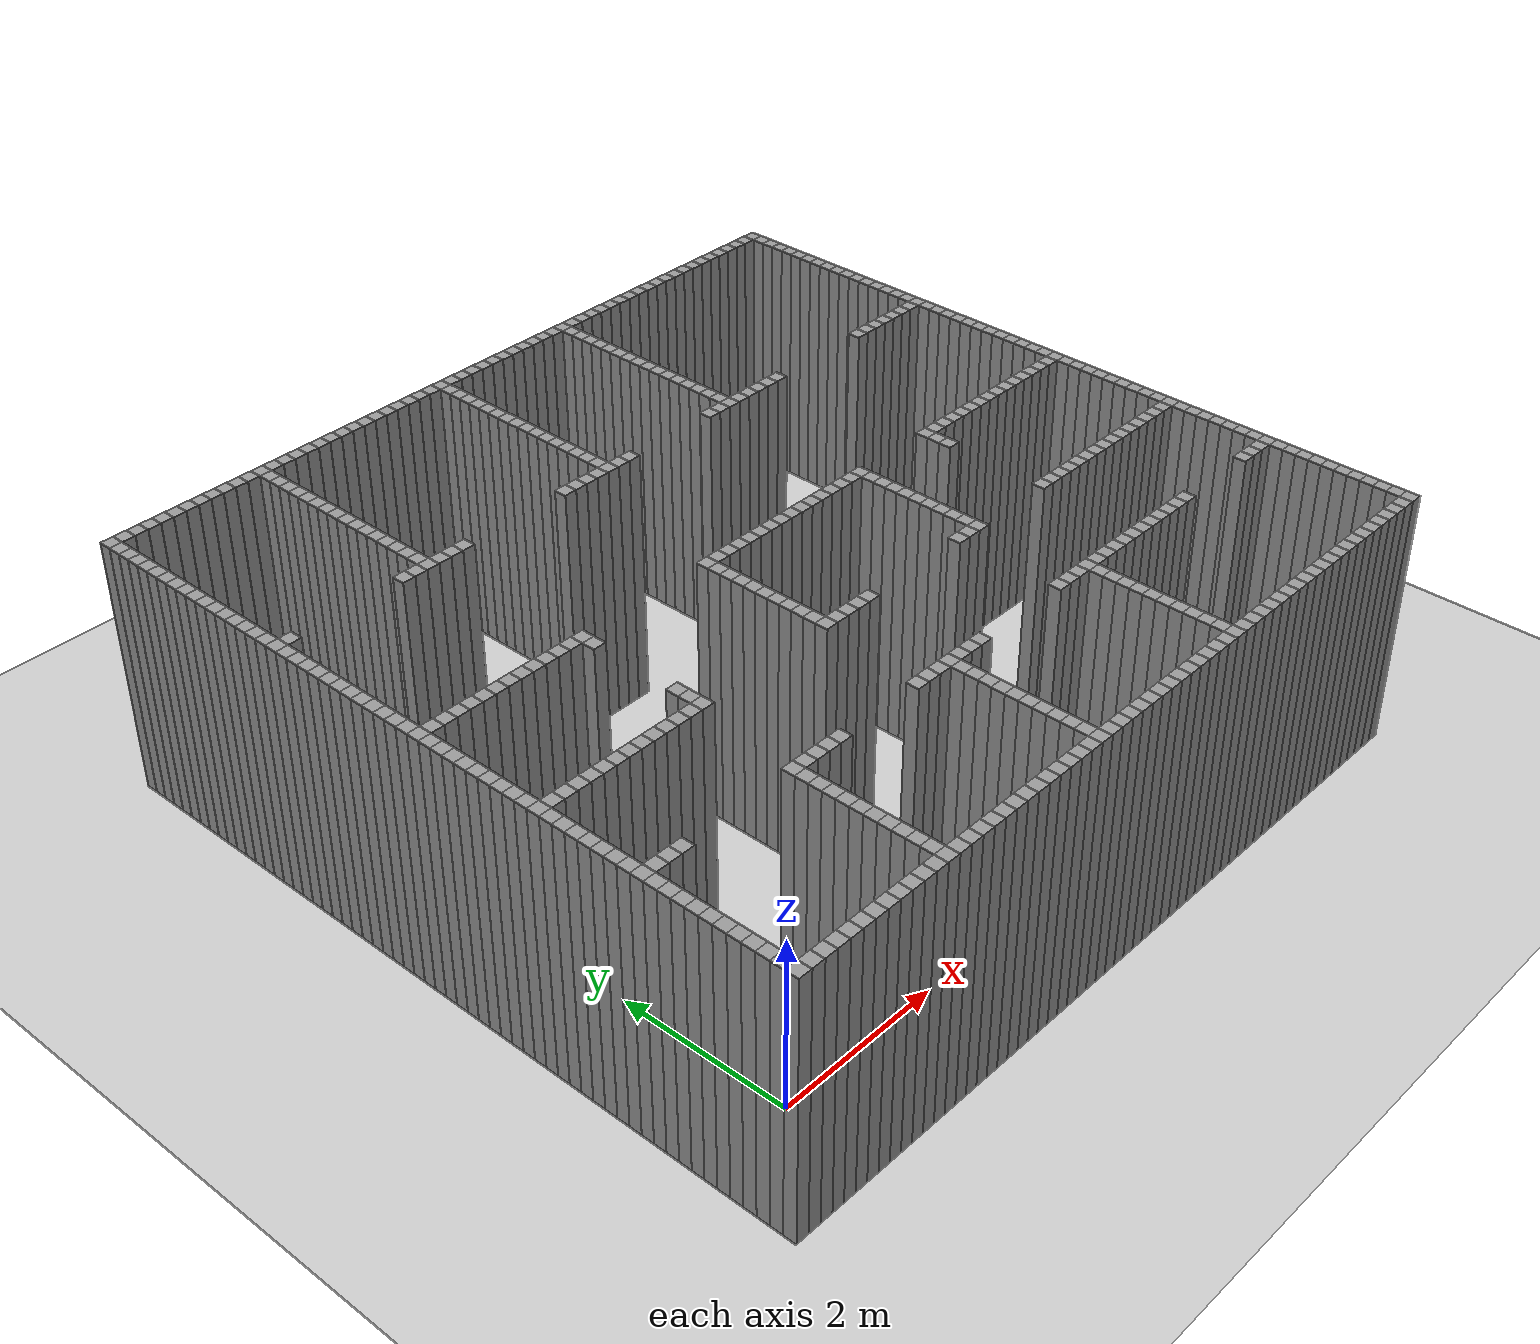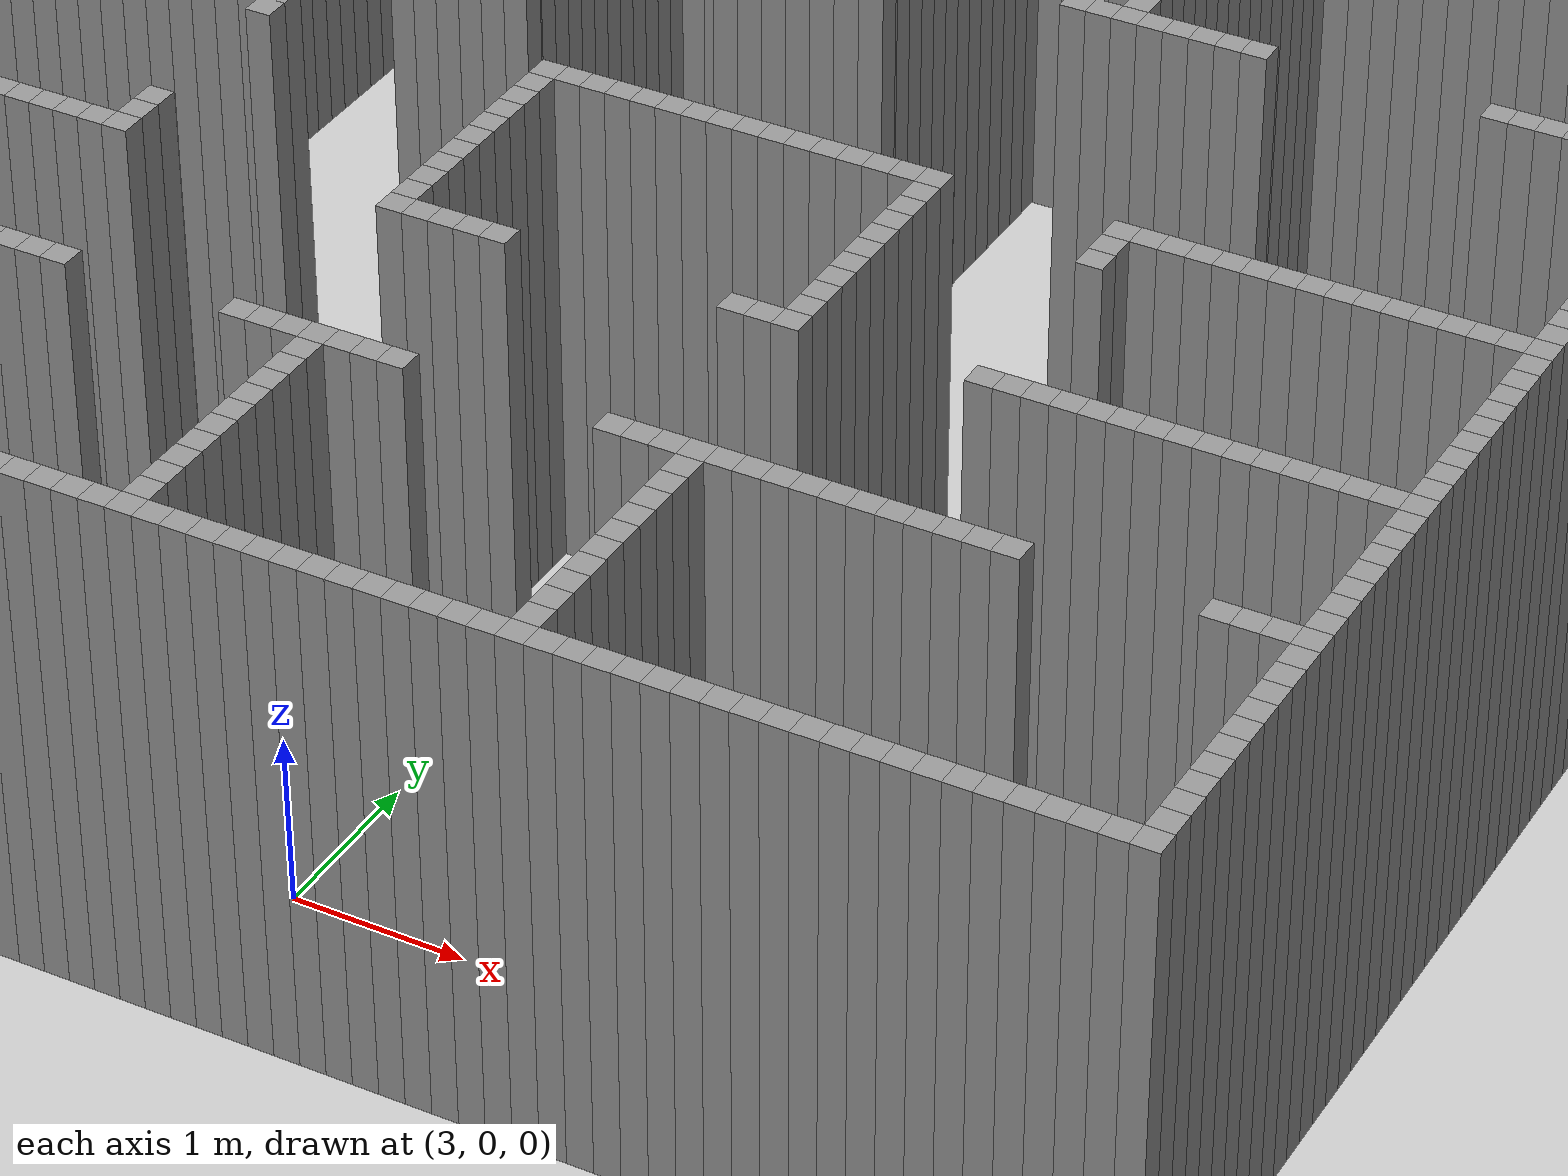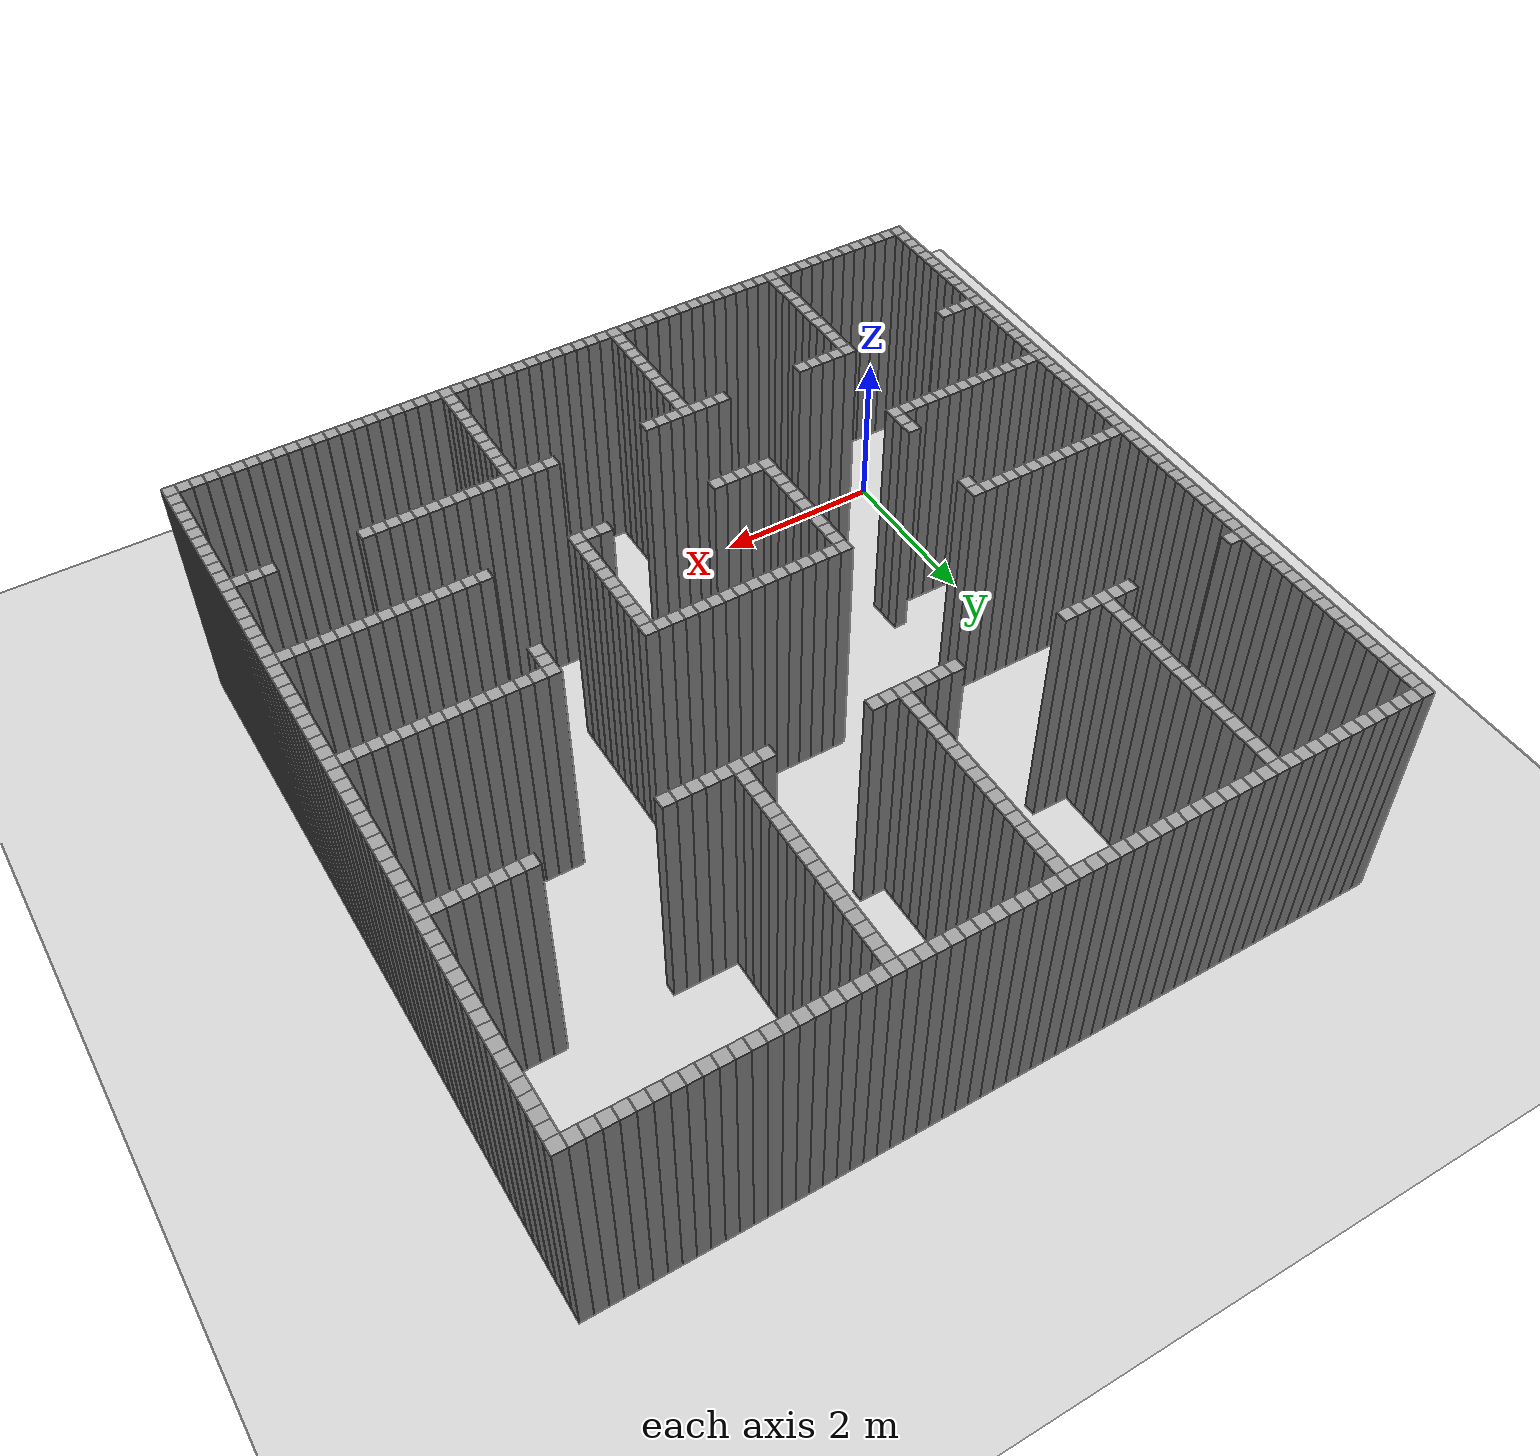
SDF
<sdf version='1.7'>
  <world name='default'>
    <light name='sun' type='directional'>
      <cast_shadows>1</cast_shadows>
      <pose>0 0 10 0 -0 0</pose>
      <diffuse>0.8 0.8 0.8 1</diffuse>
      <specular>0.2 0.2 0.2 1</specular>
      <attenuation>
        <range>1000</range>
        <constant>0.9</constant>
        <linear>0.01</linear>
        <quadratic>0.001</quadratic>
      </attenuation>
      <direction>-0.5 0.1 -0.9</direction>
      <spot>
        <inner_angle>0</inner_angle>
        <outer_angle>0</outer_angle>
        <falloff>0</falloff>
      </spot>
    </light>
    <model name='ground_plane'>
      <static>1</static>
      <link name='link'>
        <collision name='collision'>
          <geometry>
            <plane>
              <normal>0 0 1</normal>
              <size>100 100</size>
            </plane>
          </geometry>
          <surface>
            <contact>
              <collide_bitmask>65535</collide_bitmask>
              <ode/>
            </contact>
            <friction>
              <ode>
                <mu>100</mu>
                <mu2>50</mu2>
              </ode>
              <torsional>
                <ode/>
              </torsional>
            </friction>
            <bounce/>
          </surface>
          <max_contacts>10</max_contacts>
        </collision>
        <visual name='visual'>
          <cast_shadows>0</cast_shadows>
          <geometry>
            <plane>
              <normal>0 0 1</normal>
              <size>100 100</size>
            </plane>
          </geometry>
          <material>
            <script>
              <uri>file://media/materials/scripts/gazebo.material</uri>
              <name>Gazebo/Grey</name>
            </script>
          </material>
        </visual>
        <self_collide>0</self_collide>
        <enable_wind>0</enable_wind>
        <kinematic>0</kinematic>
      </link>
    </model>
    <gravity>0 0 -9.8</gravity>
    <magnetic_field>6e-06 2.3e-05 -4.2e-05</magnetic_field>
    <atmosphere type='adiabatic'/>
    <physics type='ode'>
      <max_step_size>0.001</max_step_size>
      <real_time_factor>1</real_time_factor>
      <real_time_update_rate>1000</real_time_update_rate>
    </physics>
    <scene>
      <ambient>0.4 0.4 0.4 1</ambient>
      <background>0.7 0.7 0.7 1</background>
      <shadows>1</shadows>
    </scene>
    <wind/>
    <spherical_coordinates>
      <surface_model>EARTH_WGS84</surface_model>
      <latitude_deg>0</latitude_deg>
      <longitude_deg>0</longitude_deg>
      <elevation>0</elevation>
      <heading_deg>0</heading_deg>
    </spherical_coordinates>
    <model name='image45004'>
      <pose>-1 -1 0 0 -0 0</pose>
      <link name='Wall_0'>
        <collision name='Wall_0_Collision'>
          <geometry>
            <box>
              <size>0.15 0.15 3</size>
            </box>
          </geometry>
          <pose>0 0 1.5 0 -0 0</pose>
        </collision>
        <visual name='Wall_0_Visual'>
          <pose>0 0 1.5 0 -0 0</pose>
          <geometry>
            <box>
              <size>0.15 0.15 3</size>
            </box>
          </geometry>
          <material>
            <script>
              <uri>file://media/materials/scripts/gazebo.material</uri>
              <name>Gazebo/Grey</name>
            </script>
            <ambient>1 1 1 1</ambient>
          </material>
          <meta>
            <layer>0</layer>
          </meta>
        </visual>
        <pose>0.0 0.0 0 0 -0 0</pose>
      </link>
      <link name='Wall_1'>
        <collision name='Wall_1_Collision'>
          <geometry>
            <box>
              <size>0.15 0.15 3</size>
            </box>
          </geometry>
          <pose>0 0 1.5 0 -0 0</pose>
        </collision>
        <visual name='Wall_1_Visual'>
          <pose>0 0 1.5 0 -0 0</pose>
          <geometry>
            <box>
              <size>0.15 0.15 3</size>
            </box>
          </geometry>
          <material>
            <script>
              <uri>file://media/materials/scripts/gazebo.material</uri>
              <name>Gazebo/Grey</name>
            </script>
            <ambient>1 1 1 1</ambient>
          </material>
          <meta>
            <layer>0</layer>
          </meta>
        </visual>
        <pose>0.0 0.15 0 0 -0 0</pose>
      </link>
      <link name='Wall_2'>
        <collision name='Wall_2_Collision'>
          <geometry>
            <box>
              <size>0.15 0.15 3</size>
            </box>
          </geometry>
          <pose>0 0 1.5 0 -0 0</pose>
        </collision>
        <visual name='Wall_2_Visual'>
          <pose>0 0 1.5 0 -0 0</pose>
          <geometry>
            <box>
              <size>0.15 0.15 3</size>
            </box>
          </geometry>
          <material>
            <script>
              <uri>file://media/materials/scripts/gazebo.material</uri>
              <name>Gazebo/Grey</name>
            </script>
            <ambient>1 1 1 1</ambient>
          </material>
          <meta>
            <layer>0</layer>
          </meta>
        </visual>
        <pose>0.0 0.3 0 0 -0 0</pose>
      </link>
      <link name='Wall_3'>
        <collision name='Wall_3_Collision'>
          <geometry>
            <box>
              <size>0.15 0.15 3</size>
            </box>
          </geometry>
          <pose>0 0 1.5 0 -0 0</pose>
        </collision>
        <visual name='Wall_3_Visual'>
          <pose>0 0 1.5 0 -0 0</pose>
          <geometry>
            <box>
              <size>0.15 0.15 3</size>
            </box>
          </geometry>
          <material>
            <script>
              <uri>file://media/materials/scripts/gazebo.material</uri>
              <name>Gazebo/Grey</name>
            </script>
            <ambient>1 1 1 1</ambient>
          </material>
          <meta>
            <layer>0</layer>
          </meta>
        </visual>
        <pose>0.0 0.44999999999999996 0 0 -0 0</pose>
      </link>
      <link name='Wall_4'>
        <collision name='Wall_4_Collision'>
          <geometry>
            <box>
              <size>0.15 0.15 3</size>
            </box>
          </geometry>
          <pose>0 0 1.5 0 -0 0</pose>
        </collision>
        <visual name='Wall_4_Visual'>
          <pose>0 0 1.5 0 -0 0</pose>
          <geometry>
            <box>
              <size>0.15 0.15 3</size>
            </box>
          </geometry>
          <material>
            <script>
              <uri>file://media/materials/scripts/gazebo.material</uri>
              <name>Gazebo/Grey</name>
            </script>
            <ambient>1 1 1 1</ambient>
          </material>
          <meta>
            <layer>0</layer>
          </meta>
        </visual>
        <pose>0.0 0.6 0 0 -0 0</pose>
      </link>
      <link name='Wall_5'>
        <collision name='Wall_5_Collision'>
          <geometry>
            <box>
              <size>0.15 0.15 3</size>
            </box>
          </geometry>
          <pose>0 0 1.5 0 -0 0</pose>
        </collision>
        <visual name='Wall_5_Visual'>
          <pose>0 0 1.5 0 -0 0</pose>
          <geometry>
            <box>
              <size>0.15 0.15 3</size>
            </box>
          </geometry>
          <material>
            <script>
              <uri>file://media/materials/scripts/gazebo.material</uri>
              <name>Gazebo/Grey</name>
            </script>
            <ambient>1 1 1 1</ambient>
          </material>
          <meta>
            <layer>0</layer>
          </meta>
        </visual>
        <pose>0.0 0.75 0 0 -0 0</pose>
      </link>
      <link name='Wall_6'>
        <collision name='Wall_6_Collision'>
          <geometry>
            <box>
              <size>0.15 0.15 3</size>
            </box>
          </geometry>
          <pose>0 0 1.5 0 -0 0</pose>
        </collision>
        <visual name='Wall_6_Visual'>
          <pose>0 0 1.5 0 -0 0</pose>
          <geometry>
            <box>
              <size>0.15 0.15 3</size>
            </box>
          </geometry>
          <material>
            <script>
              <uri>file://media/materials/scripts/gazebo.material</uri>
              <name>Gazebo/Grey</name>
            </script>
            <ambient>1 1 1 1</ambient>
          </material>
          <meta>
            <layer>0</layer>
          </meta>
        </visual>
        <pose>0.0 0.8999999999999999 0 0 -0 0</pose>
      </link>
      <link name='Wall_7'>
        <collision name='Wall_7_Collision'>
          <geometry>
            <box>
              <size>0.15 0.15 3</size>
            </box>
          </geometry>
          <pose>0 0 1.5 0 -0 0</pose>
        </collision>
        <visual name='Wall_7_Visual'>
          <pose>0 0 1.5 0 -0 0</pose>
          <geometry>
            <box>
              <size>0.15 0.15 3</size>
            </box>
          </geometry>
          <material>
            <script>
              <uri>file://media/materials/scripts/gazebo.material</uri>
              <name>Gazebo/Grey</name>
            </script>
            <ambient>1 1 1 1</ambient>
          </material>
          <meta>
            <layer>0</layer>
          </meta>
        </visual>
        <pose>0.0 1.05 0 0 -0 0</pose>
      </link>
      <link name='Wall_8'>
        <collision name='Wall_8_Collision'>
          <geometry>
            <box>
              <size>0.15 0.15 3</size>
            </box>
          </geometry>
          <pose>0 0 1.5 0 -0 0</pose>
        </collision>
        <visual name='Wall_8_Visual'>
          <pose>0 0 1.5 0 -0 0</pose>
          <geometry>
            <box>
              <size>0.15 0.15 3</size>
            </box>
          </geometry>
          <material>
            <script>
              <uri>file://media/materials/scripts/gazebo.material</uri>
              <name>Gazebo/Grey</name>
            </script>
            <ambient>1 1 1 1</ambient>
          </material>
          <meta>
            <layer>0</layer>
          </meta>
        </visual>
        <pose>0.0 1.2 0 0 -0 0</pose>
      </link>
      <link name='Wall_9'>
        <collision name='Wall_9_Collision'>
          <geometry>
            <box>
              <size>0.15 0.15 3</size>
            </box>
          </geometry>
          <pose>0 0 1.5 0 -0 0</pose>
        </collision>
        <visual name='Wall_9_Visual'>
          <pose>0 0 1.5 0 -0 0</pose>
          <geometry>
            <box>
              <size>0.15 0.15 3</size>
            </box>
          </geometry>
          <material>
            <script>
              <uri>file://media/materials/scripts/gazebo.material</uri>
              <name>Gazebo/Grey</name>
            </script>
            <ambient>1 1 1 1</ambient>
          </material>
          <meta>
            <layer>0</layer>
          </meta>
        </visual>
        <pose>0.0 1.3499999999999999 0 0 -0 0</pose>
      </link>
      <link name='Wall_10'>
        <collision name='Wall_10_Collision'>
          <geometry>
            <box>
              <size>0.15 0.15 3</size>
            </box>
          </geometry>
          <pose>0 0 1.5 0 -0 0</pose>
        </collision>
        <visual name='Wall_10_Visual'>
          <pose>0 0 1.5 0 -0 0</pose>
          <geometry>
            <box>
              <size>0.15 0.15 3</size>
            </box>
          </geometry>
          <material>
            <script>
              <uri>file://media/materials/scripts/gazebo.material</uri>
              <name>Gazebo/Grey</name>
            </script>
            <ambient>1 1 1 1</ambient>
          </material>
          <meta>
            <layer>0</layer>
          </meta>
        </visual>
        <pose>0.0 1.5 0 0 -0 0</pose>
      </link>
      <link name='Wall_11'>
        <collision name='Wall_11_Collision'>
          <geometry>
            <box>
              <size>0.15 0.15 3</size>
            </box>
          </geometry>
          <pose>0 0 1.5 0 -0 0</pose>
        </collision>
        <visual name='Wall_11_Visual'>
          <pose>0 0 1.5 0 -0 0</pose>
          <geometry>
            <box>
              <size>0.15 0.15 3</size>
            </box>
          </geometry>
          <material>
            <script>
              <uri>file://media/materials/scripts/gazebo.material</uri>
              <name>Gazebo/Grey</name>
            </script>
            <ambient>1 1 1 1</ambient>
          </material>
          <meta>
            <layer>0</layer>
          </meta>
        </visual>
        <pose>0.0 1.65 0 0 -0 0</pose>
      </link>
      <link name='Wall_12'>
        <collision name='Wall_12_Collision'>
          <geometry>
            <box>
              <size>0.15 0.15 3</size>
            </box>
          </geometry>
          <pose>0 0 1.5 0 -0 0</pose>
        </collision>
        <visual name='Wall_12_Visual'>
          <pose>0 0 1.5 0 -0 0</pose>
          <geometry>
            <box>
              <size>0.15 0.15 3</size>
            </box>
          </geometry>
          <material>
            <script>
              <uri>file://media/materials/scripts/gazebo.material</uri>
              <name>Gazebo/Grey</name>
            </script>
            <ambient>1 1 1 1</ambient>
          </material>
          <meta>
            <layer>0</layer>
          </meta>
        </visual>
        <pose>0.0 1.7999999999999998 0 0 -0 0</pose>
      </link>
      <link name='Wall_13'>
        <collision name='Wall_13_Collision'>
          <geometry>
            <box>
              <size>0.15 0.15 3</size>
            </box>
          </geometry>
          <pose>0 0 1.5 0 -0 0</pose>
        </collision>
        <visual name='Wall_13_Visual'>
          <pose>0 0 1.5 0 -0 0</pose>
          <geometry>
            <box>
              <size>0.15 0.15 3</size>
            </box>
          </geometry>
          <material>
            <script>
              <uri>file://media/materials/scripts/gazebo.material</uri>
              <name>Gazebo/Grey</name>
            </script>
            <ambient>1 1 1 1</ambient>
          </material>
          <meta>
            <layer>0</layer>
          </meta>
        </visual>
        <pose>0.0 1.95 0 0 -0 0</pose>
      </link>
      <link name='Wall_14'>
        <collision name='Wall_14_Collision'>
          <geometry>
            <box>
              <size>0.15 0.15 3</size>
            </box>
          </geometry>
          <pose>0 0 1.5 0 -0 0</pose>
        </collision>
        <visual name='Wall_14_Visual'>
          <pose>0 0 1.5 0 -0 0</pose>
          <geometry>
            <box>
              <size>0.15 0.15 3</size>
            </box>
          </geometry>
          <material>
            <script>
              <uri>file://media/materials/scripts/gazebo.material</uri>
              <name>Gazebo/Grey</name>
            </script>
            <ambient>1 1 1 1</ambient>
          </material>
          <meta>
            <layer>0</layer>
          </meta>
        </visual>
        <pose>0.0 2.1 0 0 -0 0</pose>
      </link>
      <link name='Wall_15'>
        <collision name='Wall_15_Collision'>
          <geometry>
            <box>
              <size>0.15 0.15 3</size>
            </box>
          </geometry>
          <pose>0 0 1.5 0 -0 0</pose>
        </collision>
        <visual name='Wall_15_Visual'>
          <pose>0 0 1.5 0 -0 0</pose>
          <geometry>
            <box>
              <size>0.15 0.15 3</size>
            </box>
          </geometry>
          <material>
            <script>
              <uri>file://media/materials/scripts/gazebo.material</uri>
              <name>Gazebo/Grey</name>
            </script>
            <ambient>1 1 1 1</ambient>
          </material>
          <meta>
            <layer>0</layer>
          </meta>
        </visual>
        <pose>0.0 2.25 0 0 -0 0</pose>
      </link>
      <link name='Wall_16'>
        <collision name='Wall_16_Collision'>
          <geometry>
            <box>
              <size>0.15 0.15 3</size>
            </box>
          </geometry>
          <pose>0 0 1.5 0 -0 0</pose>
        </collision>
        <visual name='Wall_16_Visual'>
          <pose>0 0 1.5 0 -0 0</pose>
          <geometry>
            <box>
              <size>0.15 0.15 3</size>
            </box>
          </geometry>
          <material>
            <script>
              <uri>file://media/materials/scripts/gazebo.material</uri>
              <name>Gazebo/Grey</name>
            </script>
            <ambient>1 1 1 1</ambient>
          </material>
          <meta>
            <layer>0</layer>
          </meta>
        </visual>
        <pose>0.0 2.4 0 0 -0 0</pose>
      </link>
      <link name='Wall_17'>
        <collision name='Wall_17_Collision'>
          <geometry>
            <box>
              <size>0.15 0.15 3</size>
            </box>
          </geometry>
          <pose>0 0 1.5 0 -0 0</pose>
        </collision>
        <visual name='Wall_17_Visual'>
          <pose>0 0 1.5 0 -0 0</pose>
          <geometry>
            <box>
              <size>0.15 0.15 3</size>
            </box>
          </geometry>
          <material>
            <script>
              <uri>file://media/materials/scripts/gazebo.material</uri>
              <name>Gazebo/Grey</name>
            </script>
            <ambient>1 1 1 1</ambient>
          </material>
          <meta>
            <layer>0</layer>
          </meta>
        </visual>
        <pose>0.0 2.55 0 0 -0 0</pose>
      </link>
      <link name='Wall_18'>
        <collision name='Wall_18_Collision'>
          <geometry>
            <box>
              <size>0.15 0.15 3</size>
            </box>
          </geometry>
          <pose>0 0 1.5 0 -0 0</pose>
        </collision>
        <visual name='Wall_18_Visual'>
          <pose>0 0 1.5 0 -0 0</pose>
          <geometry>
            <box>
              <size>0.15 0.15 3</size>
            </box>
          </geometry>
          <material>
            <script>
              <uri>file://media/materials/scripts/gazebo.material</uri>
              <name>Gazebo/Grey</name>
            </script>
            <ambient>1 1 1 1</ambient>
          </material>
          <meta>
            <layer>0</layer>
          </meta>
        </visual>
        <pose>0.0 2.6999999999999997 0 0 -0 0</pose>
      </link>
      <link name='Wall_19'>
        <collision name='Wall_19_Collision'>
          <geometry>
            <box>
              <size>0.15 0.15 3</size>
            </box>
          </geometry>
          <pose>0 0 1.5 0 -0 0</pose>
        </collision>
        <visual name='Wall_19_Visual'>
          <pose>0 0 1.5 0 -0 0</pose>
          <geometry>
            <box>
              <size>0.15 0.15 3</size>
            </box>
          </geometry>
          <material>
            <script>
              <uri>file://media/materials/scripts/gazebo.material</uri>
              <name>Gazebo/Grey</name>
            </script>
            <ambient>1 1 1 1</ambient>
          </material>
          <meta>
            <layer>0</layer>
          </meta>
        </visual>
        <pose>0.0 2.85 0 0 -0 0</pose>
      </link>
      <link name='Wall_20'>
        <collision name='Wall_20_Collision'>
          <geometry>
            <box>
              <size>0.15 0.15 3</size>
            </box>
          </geometry>
          <pose>0 0 1.5 0 -0 0</pose>
        </collision>
        <visual name='Wall_20_Visual'>
          <pose>0 0 1.5 0 -0 0</pose>
          <geometry>
            <box>
              <size>0.15 0.15 3</size>
            </box>
          </geometry>
          <material>
            <script>
              <uri>file://media/materials/scripts/gazebo.material</uri>
              <name>Gazebo/Grey</name>
            </script>
            <ambient>1 1 1 1</ambient>
          </material>
          <meta>
            <layer>0</layer>
          </meta>
        </visual>
        <pose>0.0 3.0 0 0 -0 0</pose>
      </link>
      <link name='Wall_21'>
        <collision name='Wall_21_Collision'>
          <geometry>
            <box>
              <size>0.15 0.15 3</size>
            </box>
          </geometry>
          <pose>0 0 1.5 0 -0 0</pose>
        </collision>
        <visual name='Wall_21_Visual'>
          <pose>0 0 1.5 0 -0 0</pose>
          <geometry>
            <box>
              <size>0.15 0.15 3</size>
            </box>
          </geometry>
          <material>
            <script>
              <uri>file://media/materials/scripts/gazebo.material</uri>
              <name>Gazebo/Grey</name>
            </script>
            <ambient>1 1 1 1</ambient>
          </material>
          <meta>
            <layer>0</layer>
          </meta>
        </visual>
        <pose>0.0 3.15 0 0 -0 0</pose>
      </link>
      <link name='Wall_22'>
        <collision name='Wall_22_Collision'>
          <geometry>
            <box>
              <size>0.15 0.15 3</size>
            </box>
          </geometry>
          <pose>0 0 1.5 0 -0 0</pose>
        </collision>
        <visual name='Wall_22_Visual'>
          <pose>0 0 1.5 0 -0 0</pose>
          <geometry>
            <box>
              <size>0.15 0.15 3</size>
            </box>
          </geometry>
          <material>
            <script>
              <uri>file://media/materials/scripts/gazebo.material</uri>
              <name>Gazebo/Grey</name>
            </script>
            <ambient>1 1 1 1</ambient>
          </material>
          <meta>
            <layer>0</layer>
          </meta>
        </visual>
        <pose>0.0 3.3 0 0 -0 0</pose>
      </link>
      <link name='Wall_23'>
        <collision name='Wall_23_Collision'>
          <geometry>
            <box>
              <size>0.15 0.15 3</size>
            </box>
          </geometry>
          <pose>0 0 1.5 0 -0 0</pose>
        </collision>
        <visual name='Wall_23_Visual'>
          <pose>0 0 1.5 0 -0 0</pose>
          <geometry>
            <box>
              <size>0.15 0.15 3</size>
            </box>
          </geometry>
          <material>
            <script>
              <uri>file://media/materials/scripts/gazebo.material</uri>
              <name>Gazebo/Grey</name>
            </script>
            <ambient>1 1 1 1</ambient>
          </material>
          <meta>
            <layer>0</layer>
          </meta>
        </visual>
        <pose>0.0 3.4499999999999997 0 0 -0 0</pose>
      </link>
      <link name='Wall_24'>
        <collision name='Wall_24_Collision'>
          <geometry>
            <box>
              <size>0.15 0.15 3</size>
            </box>
          </geometry>
          <pose>0 0 1.5 0 -0 0</pose>
        </collision>
        <visual name='Wall_24_Visual'>
          <pose>0 0 1.5 0 -0 0</pose>
          <geometry>
            <box>
              <size>0.15 0.15 3</size>
            </box>
          </geometry>
          <material>
            <script>
              <uri>file://media/materials/scripts/gazebo.material</uri>
              <name>Gazebo/Grey</name>
            </script>
            <ambient>1 1 1 1</ambient>
          </material>
          <meta>
            <layer>0</layer>
          </meta>
        </visual>
        <pose>0.0 3.5999999999999996 0 0 -0 0</pose>
      </link>
      <link name='Wall_25'>
        <collision name='Wall_25_Collision'>
          <geometry>
            <box>
              <size>0.15 0.15 3</size>
            </box>
          </geometry>
          <pose>0 0 1.5 0 -0 0</pose>
        </collision>
        <visual name='Wall_25_Visual'>
          <pose>0 0 1.5 0 -0 0</pose>
          <geometry>
            <box>
              <size>0.15 0.15 3</size>
            </box>
          </geometry>
          <material>
            <script>
              <uri>file://media/materials/scripts/gazebo.material</uri>
              <name>Gazebo/Grey</name>
            </script>
            <ambient>1 1 1 1</ambient>
          </material>
          <meta>
            <layer>0</layer>
          </meta>
        </visual>
        <pose>0.0 3.75 0 0 -0 0</pose>
      </link>
      <link name='Wall_26'>
        <collision name='Wall_26_Collision'>
          <geometry>
            <box>
              <size>0.15 0.15 3</size>
            </box>
          </geometry>
          <pose>0 0 1.5 0 -0 0</pose>
        </collision>
        <visual name='Wall_26_Visual'>
          <pose>0 0 1.5 0 -0 0</pose>
          <geometry>
            <box>
              <size>0.15 0.15 3</size>
            </box>
          </geometry>
          <material>
            <script>
              <uri>file://media/materials/scripts/gazebo.material</uri>
              <name>Gazebo/Grey</name>
            </script>
            <ambient>1 1 1 1</ambient>
          </material>
          <meta>
            <layer>0</layer>
          </meta>
        </visual>
        <pose>0.0 3.9 0 0 -0 0</pose>
      </link>
      <link name='Wall_27'>
        <collision name='Wall_27_Collision'>
          <geometry>
            <box>
              <size>0.15 0.15 3</size>
            </box>
          </geometry>
          <pose>0 0 1.5 0 -0 0</pose>
        </collision>
        <visual name='Wall_27_Visual'>
          <pose>0 0 1.5 0 -0 0</pose>
          <geometry>
            <box>
              <size>0.15 0.15 3</size>
            </box>
          </geometry>
          <material>
            <script>
              <uri>file://media/materials/scripts/gazebo.material</uri>
              <name>Gazebo/Grey</name>
            </script>
            <ambient>1 1 1 1</ambient>
          </material>
          <meta>
            <layer>0</layer>
          </meta>
        </visual>
        <pose>0.0 4.05 0 0 -0 0</pose>
      </link>
      <link name='Wall_28'>
        <collision name='Wall_28_Collision'>
          <geometry>
            <box>
              <size>0.15 0.15 3</size>
            </box>
          </geometry>
          <pose>0 0 1.5 0 -0 0</pose>
        </collision>
        <visual name='Wall_28_Visual'>
          <pose>0 0 1.5 0 -0 0</pose>
          <geometry>
            <box>
              <size>0.15 0.15 3</size>
            </box>
          </geometry>
          <material>
            <script>
              <uri>file://media/materials/scripts/gazebo.material</uri>
              <name>Gazebo/Grey</name>
            </script>
            <ambient>1 1 1 1</ambient>
          </material>
          <meta>
            <layer>0</layer>
          </meta>
        </visual>
        <pose>0.0 4.2 0 0 -0 0</pose>
      </link>
      <link name='Wall_29'>
        <collision name='Wall_29_Collision'>
          <geometry>
            <box>
              <size>0.15 0.15 3</size>
            </box>
          </geometry>
          <pose>0 0 1.5 0 -0 0</pose>
        </collision>
        <visual name='Wall_29_Visual'>
          <pose>0 0 1.5 0 -0 0</pose>
          <geometry>
            <box>
              <size>0.15 0.15 3</size>
            </box>
          </geometry>
          <material>
            <script>
              <uri>file://media/materials/scripts/gazebo.material</uri>
              <name>Gazebo/Grey</name>
            </script>
            <ambient>1 1 1 1</ambient>
          </material>
          <meta>
            <layer>0</layer>
          </meta>
        </visual>
        <pose>0.0 4.35 0 0 -0 0</pose>
      </link>
      <link name='Wall_30'>
        <collision name='Wall_30_Collision'>
          <geometry>
            <box>
              <size>0.15 0.15 3</size>
            </box>
          </geometry>
          <pose>0 0 1.5 0 -0 0</pose>
        </collision>
        <visual name='Wall_30_Visual'>
          <pose>0 0 1.5 0 -0 0</pose>
          <geometry>
            <box>
              <size>0.15 0.15 3</size>
            </box>
          </geometry>
          <material>
            <script>
              <uri>file://media/materials/scripts/gazebo.material</uri>
              <name>Gazebo/Grey</name>
            </script>
            <ambient>1 1 1 1</ambient>
          </material>
          <meta>
            <layer>0</layer>
          </meta>
        </visual>
        <pose>0.0 4.5 0 0 -0 0</pose>
      </link>
      <link name='Wall_31'>
        <collision name='Wall_31_Collision'>
          <geometry>
            <box>
              <size>0.15 0.15 3</size>
            </box>
          </geometry>
          <pose>0 0 1.5 0 -0 0</pose>
        </collision>
        <visual name='Wall_31_Visual'>
          <pose>0 0 1.5 0 -0 0</pose>
          <geometry>
            <box>
              <size>0.15 0.15 3</size>
            </box>
          </geometry>
          <material>
            <script>
              <uri>file://media/materials/scripts/gazebo.material</uri>
              <name>Gazebo/Grey</name>
            </script>
            <ambient>1 1 1 1</ambient>
          </material>
          <meta>
            <layer>0</layer>
          </meta>
        </visual>
        <pose>0.0 4.6499999999999995 0 0 -0 0</pose>
      </link>
      <link name='Wall_32'>
        <collision name='Wall_32_Collision'>
          <geometry>
            <box>
              <size>0.15 0.15 3</size>
            </box>
          </geometry>
          <pose>0 0 1.5 0 -0 0</pose>
        </collision>
        <visual name='Wall_32_Visual'>
          <pose>0 0 1.5 0 -0 0</pose>
          <geometry>
            <box>
              <size>0.15 0.15 3</size>
            </box>
          </geometry>
          <material>
            <script>
              <uri>file://media/materials/scripts/gazebo.material</uri>
              <name>Gazebo/Grey</name>
            </script>
            <ambient>1 1 1 1</ambient>
          </material>
          <meta>
            <layer>0</layer>
          </meta>
        </visual>
        <pose>0.0 4.8 0 0 -0 0</pose>
      </link>
      <link name='Wall_33'>
        <collision name='Wall_33_Collision'>
          <geometry>
            <box>
              <size>0.15 0.15 3</size>
            </box>
          </geometry>
          <pose>0 0 1.5 0 -0 0</pose>
        </collision>
        <visual name='Wall_33_Visual'>
          <pose>0 0 1.5 0 -0 0</pose>
          <geometry>
            <box>
              <size>0.15 0.15 3</size>
            </box>
          </geometry>
          <material>
            <script>
              <uri>file://media/materials/scripts/gazebo.material</uri>
              <name>Gazebo/Grey</name>
            </script>
            <ambient>1 1 1 1</ambient>
          </material>
          <meta>
            <layer>0</layer>
          </meta>
        </visual>
        <pose>0.0 4.95 0 0 -0 0</pose>
      </link>
      <link name='Wall_34'>
        <collision name='Wall_34_Collision'>
          <geometry>
            <box>
              <size>0.15 0.15 3</size>
            </box>
          </geometry>
          <pose>0 0 1.5 0 -0 0</pose>
        </collision>
        <visual name='Wall_34_Visual'>
          <pose>0 0 1.5 0 -0 0</pose>
          <geometry>
            <box>
              <size>0.15 0.15 3</size>
            </box>
          </geometry>
          <material>
            <script>
              <uri>file://media/materials/scripts/gazebo.material</uri>
              <name>Gazebo/Grey</name>
            </script>
            <ambient>1 1 1 1</ambient>
          </material>
          <meta>
            <layer>0</layer>
          </meta>
        </visual>
        <pose>0.0 5.1 0 0 -0 0</pose>
      </link>
      <link name='Wall_35'>
        <collision name='Wall_35_Collision'>
          <geometry>
            <box>
              <size>0.15 0.15 3</size>
            </box>
          </geometry>
          <pose>0 0 1.5 0 -0 0</pose>
        </collision>
        <visual name='Wall_35_Visual'>
          <pose>0 0 1.5 0 -0 0</pose>
          <geometry>
            <box>
              <size>0.15 0.15 3</size>
            </box>
          </geometry>
          <material>
            <script>
              <uri>file://media/materials/scripts/gazebo.material</uri>
              <name>Gazebo/Grey</name>
            </script>
            <ambient>1 1 1 1</ambient>
          </material>
          <meta>
            <layer>0</layer>
          </meta>
        </visual>
        <pose>0.0 5.25 0 0 -0 0</pose>
      </link>
      <link name='Wall_36'>
        <collision name='Wall_36_Collision'>
          <geometry>
            <box>
              <size>0.15 0.15 3</size>
            </box>
          </geometry>
          <pose>0 0 1.5 0 -0 0</pose>
        </collision>
        <visual name='Wall_36_Visual'>
          <pose>0 0 1.5 0 -0 0</pose>
          <geometry>
            <box>
              <size>0.15 0.15 3</size>
            </box>
          </geometry>
          <material>
            <script>
              <uri>file://media/materials/scripts/gazebo.material</uri>
              <name>Gazebo/Grey</name>
            </script>
            <ambient>1 1 1 1</ambient>
          </material>
          <meta>
            <layer>0</layer>
          </meta>
        </visual>
        <pose>0.0 5.3999999999999995 0 0 -0 0</pose>
      </link>
      <link name='Wall_37'>
        <collision name='Wall_37_Collision'>
          <geometry>
            <box>
              <size>0.15 0.15 3</size>
            </box>
          </geometry>
          <pose>0 0 1.5 0 -0 0</pose>
        </collision>
        <visual name='Wall_37_Visual'>
          <pose>0 0 1.5 0 -0 0</pose>
          <geometry>
            <box>
              <size>0.15 0.15 3</size>
            </box>
          </geometry>
          <material>
            <script>
              <uri>file://media/materials/scripts/gazebo.material</uri>
              <name>Gazebo/Grey</name>
            </script>
            <ambient>1 1 1 1</ambient>
          </material>
          <meta>
            <layer>0</layer>
          </meta>
        </visual>
        <pose>0.0 5.55 0 0 -0 0</pose>
      </link>
      <link name='Wall_38'>
        <collision name='Wall_38_Collision'>
          <geometry>
            <box>
              <size>0.15 0.15 3</size>
            </box>
          </geometry>
          <pose>0 0 1.5 0 -0 0</pose>
        </collision>
        <visual name='Wall_38_Visual'>
          <pose>0 0 1.5 0 -0 0</pose>
          <geometry>
            <box>
              <size>0.15 0.15 3</size>
            </box>
          </geometry>
          <material>
            <script>
              <uri>file://media/materials/scripts/gazebo.material</uri>
              <name>Gazebo/Grey</name>
            </script>
            <ambient>1 1 1 1</ambient>
          </material>
          <meta>
            <layer>0</layer>
          </meta>
        </visual>
        <pose>0.0 5.7 0 0 -0 0</pose>
      </link>
      <link name='Wall_39'>
        <collision name='Wall_39_Collision'>
          <geometry>
            <box>
              <size>0.15 0.15 3</size>
            </box>
          </geometry>
          <pose>0 0 1.5 0 -0 0</pose>
        </collision>
        <visual name='Wall_39_Visual'>
          <pose>0 0 1.5 0 -0 0</pose>
          <geometry>
            <box>
              <size>0.15 0.15 3</size>
            </box>
          </geometry>
          <material>
            <script>
              <uri>file://media/materials/scripts/gazebo.material</uri>
              <name>Gazebo/Grey</name>
            </script>
            <ambient>1 1 1 1</ambient>
          </material>
          <meta>
            <layer>0</layer>
          </meta>
        </visual>
        <pose>0.0 5.85 0 0 -0 0</pose>
      </link>
      <link name='Wall_40'>
        <collision name='Wall_40_Collision'>
          <geometry>
            <box>
              <size>0.15 0.15 3</size>
            </box>
          </geometry>
          <pose>0 0 1.5 0 -0 0</pose>
        </collision>
        <visual name='Wall_40_Visual'>
          <pose>0 0 1.5 0 -0 0</pose>
          <geometry>
            <box>
              <size>0.15 0.15 3</size>
            </box>
          </geometry>
          <material>
            <script>
              <uri>file://media/materials/scripts/gazebo.material</uri>
              <name>Gazebo/Grey</name>
            </script>
            <ambient>1 1 1 1</ambient>
          </material>
          <meta>
            <layer>0</layer>
          </meta>
        </visual>
        <pose>0.0 6.0 0 0 -0 0</pose>
      </link>
      <link name='Wall_41'>
        <collision name='Wall_41_Collision'>
          <geometry>
            <box>
              <size>0.15 0.15 3</size>
            </box>
          </geometry>
          <pose>0 0 1.5 0 -0 0</pose>
        </collision>
        <visual name='Wall_41_Visual'>
          <pose>0 0 1.5 0 -0 0</pose>
          <geometry>
            <box>
              <size>0.15 0.15 3</size>
            </box>
          </geometry>
          <material>
            <script>
              <uri>file://media/materials/scripts/gazebo.material</uri>
              <name>Gazebo/Grey</name>
            </script>
            <ambient>1 1 1 1</ambient>
          </material>
          <meta>
            <layer>0</layer>
          </meta>
        </visual>
        <pose>0.0 6.1499999999999995 0 0 -0 0</pose>
      </link>
      <link name='Wall_42'>
        <collision name='Wall_42_Collision'>
          <geometry>
            <box>
              <size>0.15 0.15 3</size>
            </box>
          </geometry>
          <pose>0 0 1.5 0 -0 0</pose>
        </collision>
        <visual name='Wall_42_Visual'>
          <pose>0 0 1.5 0 -0 0</pose>
          <geometry>
            <box>
              <size>0.15 0.15 3</size>
            </box>
          </geometry>
          <material>
            <script>
              <uri>file://media/materials/scripts/gazebo.material</uri>
              <name>Gazebo/Grey</name>
            </script>
            <ambient>1 1 1 1</ambient>
          </material>
          <meta>
            <layer>0</layer>
          </meta>
        </visual>
        <pose>0.0 6.3 0 0 -0 0</pose>
      </link>
      <link name='Wall_43'>
        <collision name='Wall_43_Collision'>
          <geometry>
            <box>
              <size>0.15 0.15 3</size>
            </box>
          </geometry>
          <pose>0 0 1.5 0 -0 0</pose>
        </collision>
        <visual name='Wall_43_Visual'>
          <pose>0 0 1.5 0 -0 0</pose>
          <geometry>
            <box>
              <size>0.15 0.15 3</size>
            </box>
          </geometry>
          <material>
            <script>
              <uri>file://media/materials/scripts/gazebo.material</uri>
              <name>Gazebo/Grey</name>
            </script>
            <ambient>1 1 1 1</ambient>
          </material>
          <meta>
            <layer>0</layer>
          </meta>
        </visual>
        <pose>0.0 6.45 0 0 -0 0</pose>
      </link>
      <link name='Wall_44'>
        <collision name='Wall_44_Collision'>
          <geometry>
            <box>
              <size>0.15 0.15 3</size>
            </box>
          </geometry>
          <pose>0 0 1.5 0 -0 0</pose>
        </collision>
        <visual name='Wall_44_Visual'>
          <pose>0 0 1.5 0 -0 0</pose>
          <geometry>
            <box>
              <size>0.15 0.15 3</size>
            </box>
          </geometry>
          <material>
            <script>
              <uri>file://media/materials/scripts/gazebo.material</uri>
              <name>Gazebo/Grey</name>
            </script>
            <ambient>1 1 1 1</ambient>
          </material>
          <meta>
            <layer>0</layer>
          </meta>
        </visual>
        <pose>0.0 6.6 0 0 -0 0</pose>
      </link>
      <link name='Wall_45'>
        <collision name='Wall_45_Collision'>
          <geometry>
            <box>
              <size>0.15 0.15 3</size>
            </box>
          </geometry>
          <pose>0 0 1.5 0 -0 0</pose>
        </collision>
        <visual name='Wall_45_Visual'>
          <pose>0 0 1.5 0 -0 0</pose>
          <geometry>
            <box>
              <size>0.15 0.15 3</size>
            </box>
          </geometry>
          <material>
            <script>
              <uri>file://media/materials/scripts/gazebo.material</uri>
              <name>Gazebo/Grey</name>
            </script>
            <ambient>1 1 1 1</ambient>
          </material>
          <meta>
            <layer>0</layer>
          </meta>
        </visual>
        <pose>0.0 6.75 0 0 -0 0</pose>
      </link>
      <link name='Wall_46'>
        <collision name='Wall_46_Collision'>
          <geometry>
            <box>
              <size>0.15 0.15 3</size>
            </box>
          </geometry>
          <pose>0 0 1.5 0 -0 0</pose>
        </collision>
        <visual name='Wall_46_Visual'>
          <pose>0 0 1.5 0 -0 0</pose>
          <geometry>
            <box>
              <size>0.15 0.15 3</size>
            </box>
          </geometry>
          <material>
            <script>
              <uri>file://media/materials/scripts/gazebo.material</uri>
              <name>Gazebo/Grey</name>
            </script>
            <ambient>1 1 1 1</ambient>
          </material>
          <meta>
            <layer>0</layer>
          </meta>
        </visual>
        <pose>0.0 6.8999999999999995 0 0 -0 0</pose>
      </link>
      <link name='Wall_47'>
        <collision name='Wall_47_Collision'>
          <geometry>
            <box>
              <size>0.15 0.15 3</size>
            </box>
          </geometry>
          <pose>0 0 1.5 0 -0 0</pose>
        </collision>
        <visual name='Wall_47_Visual'>
          <pose>0 0 1.5 0 -0 0</pose>
          <geometry>
            <box>
              <size>0.15 0.15 3</size>
            </box>
          </geometry>
          <material>
            <script>
              <uri>file://media/materials/scripts/gazebo.material</uri>
              <name>Gazebo/Grey</name>
            </script>
            <ambient>1 1 1 1</ambient>
          </material>
          <meta>
            <layer>0</layer>
          </meta>
        </visual>
        <pose>0.0 7.05 0 0 -0 0</pose>
      </link>
      <link name='Wall_48'>
        <collision name='Wall_48_Collision'>
          <geometry>
            <box>
              <size>0.15 0.15 3</size>
            </box>
          </geometry>
          <pose>0 0 1.5 0 -0 0</pose>
        </collision>
        <visual name='Wall_48_Visual'>
          <pose>0 0 1.5 0 -0 0</pose>
          <geometry>
            <box>
              <size>0.15 0.15 3</size>
            </box>
          </geometry>
          <material>
            <script>
              <uri>file://media/materials/scripts/gazebo.material</uri>
              <name>Gazebo/Grey</name>
            </script>
            <ambient>1 1 1 1</ambient>
          </material>
          <meta>
            <layer>0</layer>
          </meta>
        </visual>
        <pose>0.0 7.199999999999999 0 0 -0 0</pose>
      </link>
      <link name='Wall_49'>
        <collision name='Wall_49_Collision'>
          <geometry>
            <box>
              <size>0.15 0.15 3</size>
            </box>
          </geometry>
          <pose>0 0 1.5 0 -0 0</pose>
        </collision>
        <visual name='Wall_49_Visual'>
          <pose>0 0 1.5 0 -0 0</pose>
          <geometry>
            <box>
              <size>0.15 0.15 3</size>
            </box>
          </geometry>
          <material>
            <script>
              <uri>file://media/materials/scripts/gazebo.material</uri>
              <name>Gazebo/Grey</name>
            </script>
            <ambient>1 1 1 1</ambient>
          </material>
          <meta>
            <layer>0</layer>
          </meta>
        </visual>
        <pose>0.0 7.35 0 0 -0 0</pose>
      </link>
      <link name='Wall_50'>
        <collision name='Wall_50_Collision'>
          <geometry>
            <box>
              <size>0.15 0.15 3</size>
            </box>
          </geometry>
          <pose>0 0 1.5 0 -0 0</pose>
        </collision>
        <visual name='Wall_50_Visual'>
          <pose>0 0 1.5 0 -0 0</pose>
          <geometry>
            <box>
              <size>0.15 0.15 3</size>
            </box>
          </geometry>
          <material>
            <script>
              <uri>file://media/materials/scripts/gazebo.material</uri>
              <name>Gazebo/Grey</name>
            </script>
            <ambient>1 1 1 1</ambient>
          </material>
          <meta>
            <layer>0</layer>
          </meta>
        </visual>
        <pose>0.0 7.5 0 0 -0 0</pose>
      </link>
      <link name='Wall_51'>
        <collision name='Wall_51_Collision'>
          <geometry>
            <box>
              <size>0.15 0.15 3</size>
            </box>
          </geometry>
          <pose>0 0 1.5 0 -0 0</pose>
        </collision>
        <visual name='Wall_51_Visual'>
          <pose>0 0 1.5 0 -0 0</pose>
          <geometry>
            <box>
              <size>0.15 0.15 3</size>
            </box>
          </geometry>
          <material>
            <script>
              <uri>file://media/materials/scripts/gazebo.material</uri>
              <name>Gazebo/Grey</name>
            </script>
            <ambient>1 1 1 1</ambient>
          </material>
          <meta>
            <layer>0</layer>
          </meta>
        </visual>
        <pose>0.0 7.6499999999999995 0 0 -0 0</pose>
      </link>
      <link name='Wall_52'>
        <collision name='Wall_52_Collision'>
          <geometry>
            <box>
              <size>0.15 0.15 3</size>
            </box>
          </geometry>
          <pose>0 0 1.5 0 -0 0</pose>
        </collision>
        <visual name='Wall_52_Visual'>
          <pose>0 0 1.5 0 -0 0</pose>
          <geometry>
            <box>
              <size>0.15 0.15 3</size>
            </box>
          </geometry>
          <material>
            <script>
              <uri>file://media/materials/scripts/gazebo.material</uri>
              <name>Gazebo/Grey</name>
            </script>
            <ambient>1 1 1 1</ambient>
          </material>
          <meta>
            <layer>0</layer>
          </meta>
        </visual>
        <pose>0.0 7.8 0 0 -0 0</pose>
      </link>
      <link name='Wall_53'>
        <collision name='Wall_53_Collision'>
          <geometry>
            <box>
              <size>0.15 0.15 3</size>
            </box>
          </geometry>
          <pose>0 0 1.5 0 -0 0</pose>
        </collision>
        <visual name='Wall_53_Visual'>
          <pose>0 0 1.5 0 -0 0</pose>
          <geometry>
            <box>
              <size>0.15 0.15 3</size>
            </box>
          </geometry>
          <material>
            <script>
              <uri>file://media/materials/scripts/gazebo.material</uri>
              <name>Gazebo/Grey</name>
            </script>
            <ambient>1 1 1 1</ambient>
          </material>
          <meta>
            <layer>0</layer>
          </meta>
        </visual>
        <pose>0.0 7.949999999999999 0 0 -0 0</pose>
      </link>
      <link name='Wall_54'>
        <collision name='Wall_54_Collision'>
          <geometry>
            <box>
              <size>0.15 0.15 3</size>
            </box>
          </geometry>
          <pose>0 0 1.5 0 -0 0</pose>
        </collision>
        <visual name='Wall_54_Visual'>
          <pose>0 0 1.5 0 -0 0</pose>
          <geometry>
            <box>
              <size>0.15 0.15 3</size>
            </box>
          </geometry>
          <material>
            <script>
              <uri>file://media/materials/scripts/gazebo.material</uri>
              <name>Gazebo/Grey</name>
            </script>
            <ambient>1 1 1 1</ambient>
          </material>
          <meta>
            <layer>0</layer>
          </meta>
        </visual>
        <pose>0.0 8.1 0 0 -0 0</pose>
      </link>
      <link name='Wall_55'>
        <collision name='Wall_55_Collision'>
          <geometry>
            <box>
              <size>0.15 0.15 3</size>
            </box>
          </geometry>
          <pose>0 0 1.5 0 -0 0</pose>
        </collision>
        <visual name='Wall_55_Visual'>
          <pose>0 0 1.5 0 -0 0</pose>
          <geometry>
            <box>
              <size>0.15 0.15 3</size>
            </box>
          </geometry>
          <material>
            <script>
              <uri>file://media/materials/scripts/gazebo.material</uri>
              <name>Gazebo/Grey</name>
            </script>
            <ambient>1 1 1 1</ambient>
          </material>
          <meta>
            <layer>0</layer>
          </meta>
        </visual>
        <pose>0.0 8.25 0 0 -0 0</pose>
      </link>
      <link name='Wall_56'>
        <collision name='Wall_56_Collision'>
          <geometry>
            <box>
              <size>0.15 0.15 3</size>
            </box>
          </geometry>
          <pose>0 0 1.5 0 -0 0</pose>
        </collision>
        <visual name='Wall_56_Visual'>
          <pose>0 0 1.5 0 -0 0</pose>
          <geometry>
            <box>
              <size>0.15 0.15 3</size>
            </box>
          </geometry>
          <material>
            <script>
              <uri>file://media/materials/scripts/gazebo.material</uri>
              <name>Gazebo/Grey</name>
            </script>
            <ambient>1 1 1 1</ambient>
          </material>
          <meta>
            <layer>0</layer>
          </meta>
        </visual>
        <pose>0.0 8.4 0 0 -0 0</pose>
      </link>
      <link name='Wall_57'>
        <collision name='Wall_57_Collision'>
          <geometry>
            <box>
              <size>0.15 0.15 3</size>
            </box>
          </geometry>
          <pose>0 0 1.5 0 -0 0</pose>
        </collision>
        <visual name='Wall_57_Visual'>
          <pose>0 0 1.5 0 -0 0</pose>
          <geometry>
            <box>
              <size>0.15 0.15 3</size>
            </box>
          </geometry>
          <material>
            <script>
              <uri>file://media/materials/scripts/gazebo.material</uri>
              <name>Gazebo/Grey</name>
            </script>
            <ambient>1 1 1 1</ambient>
          </material>
          <meta>
            <layer>0</layer>
          </meta>
        </visual>
        <pose>0.0 8.549999999999999 0 0 -0 0</pose>
      </link>
      <link name='Wall_58'>
        <collision name='Wall_58_Collision'>
          <geometry>
            <box>
              <size>0.15 0.15 3</size>
            </box>
          </geometry>
          <pose>0 0 1.5 0 -0 0</pose>
        </collision>
        <visual name='Wall_58_Visual'>
          <pose>0 0 1.5 0 -0 0</pose>
          <geometry>
            <box>
              <size>0.15 0.15 3</size>
            </box>
          </geometry>
          <material>
            <script>
              <uri>file://media/materials/scripts/gazebo.material</uri>
              <name>Gazebo/Grey</name>
            </script>
            <ambient>1 1 1 1</ambient>
          </material>
          <meta>
            <layer>0</layer>
          </meta>
        </visual>
        <pose>0.0 8.7 0 0 -0 0</pose>
      </link>
      <link name='Wall_59'>
        <collision name='Wall_59_Collision'>
          <geometry>
            <box>
              <size>0.15 0.15 3</size>
            </box>
          </geometry>
          <pose>0 0 1.5 0 -0 0</pose>
        </collision>
        <visual name='Wall_59_Visual'>
          <pose>0 0 1.5 0 -0 0</pose>
          <geometry>
            <box>
              <size>0.15 0.15 3</size>
            </box>
          </geometry>
          <material>
            <script>
              <uri>file://media/materials/scripts/gazebo.material</uri>
              <name>Gazebo/Grey</name>
            </script>
            <ambient>1 1 1 1</ambient>
          </material>
          <meta>
            <layer>0</layer>
          </meta>
        </visual>
        <pose>0.0 8.85 0 0 -0 0</pose>
      </link>
      <link name='Wall_60'>
        <collision name='Wall_60_Collision'>
          <geometry>
            <box>
              <size>0.15 0.15 3</size>
            </box>
          </geometry>
          <pose>0 0 1.5 0 -0 0</pose>
        </collision>
        <visual name='Wall_60_Visual'>
          <pose>0 0 1.5 0 -0 0</pose>
          <geometry>
            <box>
              <size>0.15 0.15 3</size>
            </box>
          </geometry>
          <material>
            <script>
              <uri>file://media/materials/scripts/gazebo.material</uri>
              <name>Gazebo/Grey</name>
            </script>
            <ambient>1 1 1 1</ambient>
          </material>
          <meta>
            <layer>0</layer>
          </meta>
        </visual>
        <pose>0.15 0.0 0 0 -0 0</pose>
      </link>
      <link name='Wall_61'>
        <collision name='Wall_61_Collision'>
          <geometry>
            <box>
              <size>0.15 0.15 3</size>
            </box>
          </geometry>
          <pose>0 0 1.5 0 -0 0</pose>
        </collision>
        <visual name='Wall_61_Visual'>
          <pose>0 0 1.5 0 -0 0</pose>
          <geometry>
            <box>
              <size>0.15 0.15 3</size>
            </box>
          </geometry>
          <material>
            <script>
              <uri>file://media/materials/scripts/gazebo.material</uri>
              <name>Gazebo/Grey</name>
            </script>
            <ambient>1 1 1 1</ambient>
          </material>
          <meta>
            <layer>0</layer>
          </meta>
        </visual>
        <pose>0.15 1.65 0 0 -0 0</pose>
      </link>
      <link name='Wall_62'>
        <collision name='Wall_62_Collision'>
          <geometry>
            <box>
              <size>0.15 0.15 3</size>
            </box>
          </geometry>
          <pose>0 0 1.5 0 -0 0</pose>
        </collision>
        <visual name='Wall_62_Visual'>
          <pose>0 0 1.5 0 -0 0</pose>
          <geometry>
            <box>
              <size>0.15 0.15 3</size>
            </box>
          </geometry>
          <material>
            <script>
              <uri>file://media/materials/scripts/gazebo.material</uri>
              <name>Gazebo/Grey</name>
            </script>
            <ambient>1 1 1 1</ambient>
          </material>
          <meta>
            <layer>0</layer>
          </meta>
        </visual>
        <pose>0.15 2.85 0 0 -0 0</pose>
      </link>
      <link name='Wall_63'>
        <collision name='Wall_63_Collision'>
          <geometry>
            <box>
              <size>0.15 0.15 3</size>
            </box>
          </geometry>
          <pose>0 0 1.5 0 -0 0</pose>
        </collision>
        <visual name='Wall_63_Visual'>
          <pose>0 0 1.5 0 -0 0</pose>
          <geometry>
            <box>
              <size>0.15 0.15 3</size>
            </box>
          </geometry>
          <material>
            <script>
              <uri>file://media/materials/scripts/gazebo.material</uri>
              <name>Gazebo/Grey</name>
            </script>
            <ambient>1 1 1 1</ambient>
          </material>
          <meta>
            <layer>0</layer>
          </meta>
        </visual>
        <pose>0.15 4.35 0 0 -0 0</pose>
      </link>
      <link name='Wall_64'>
        <collision name='Wall_64_Collision'>
          <geometry>
            <box>
              <size>0.15 0.15 3</size>
            </box>
          </geometry>
          <pose>0 0 1.5 0 -0 0</pose>
        </collision>
        <visual name='Wall_64_Visual'>
          <pose>0 0 1.5 0 -0 0</pose>
          <geometry>
            <box>
              <size>0.15 0.15 3</size>
            </box>
          </geometry>
          <material>
            <script>
              <uri>file://media/materials/scripts/gazebo.material</uri>
              <name>Gazebo/Grey</name>
            </script>
            <ambient>1 1 1 1</ambient>
          </material>
          <meta>
            <layer>0</layer>
          </meta>
        </visual>
        <pose>0.15 6.3 0 0 -0 0</pose>
      </link>
      <link name='Wall_65'>
        <collision name='Wall_65_Collision'>
          <geometry>
            <box>
              <size>0.15 0.15 3</size>
            </box>
          </geometry>
          <pose>0 0 1.5 0 -0 0</pose>
        </collision>
        <visual name='Wall_65_Visual'>
          <pose>0 0 1.5 0 -0 0</pose>
          <geometry>
            <box>
              <size>0.15 0.15 3</size>
            </box>
          </geometry>
          <material>
            <script>
              <uri>file://media/materials/scripts/gazebo.material</uri>
              <name>Gazebo/Grey</name>
            </script>
            <ambient>1 1 1 1</ambient>
          </material>
          <meta>
            <layer>0</layer>
          </meta>
        </visual>
        <pose>0.15 8.85 0 0 -0 0</pose>
      </link>
      <link name='Wall_66'>
        <collision name='Wall_66_Collision'>
          <geometry>
            <box>
              <size>0.15 0.15 3</size>
            </box>
          </geometry>
          <pose>0 0 1.5 0 -0 0</pose>
        </collision>
        <visual name='Wall_66_Visual'>
          <pose>0 0 1.5 0 -0 0</pose>
          <geometry>
            <box>
              <size>0.15 0.15 3</size>
            </box>
          </geometry>
          <material>
            <script>
              <uri>file://media/materials/scripts/gazebo.material</uri>
              <name>Gazebo/Grey</name>
            </script>
            <ambient>1 1 1 1</ambient>
          </material>
          <meta>
            <layer>0</layer>
          </meta>
        </visual>
        <pose>0.3 0.0 0 0 -0 0</pose>
      </link>
      <link name='Wall_67'>
        <collision name='Wall_67_Collision'>
          <geometry>
            <box>
              <size>0.15 0.15 3</size>
            </box>
          </geometry>
          <pose>0 0 1.5 0 -0 0</pose>
        </collision>
        <visual name='Wall_67_Visual'>
          <pose>0 0 1.5 0 -0 0</pose>
          <geometry>
            <box>
              <size>0.15 0.15 3</size>
            </box>
          </geometry>
          <material>
            <script>
              <uri>file://media/materials/scripts/gazebo.material</uri>
              <name>Gazebo/Grey</name>
            </script>
            <ambient>1 1 1 1</ambient>
          </material>
          <meta>
            <layer>0</layer>
          </meta>
        </visual>
        <pose>0.3 1.65 0 0 -0 0</pose>
      </link>
      <link name='Wall_68'>
        <collision name='Wall_68_Collision'>
          <geometry>
            <box>
              <size>0.15 0.15 3</size>
            </box>
          </geometry>
          <pose>0 0 1.5 0 -0 0</pose>
        </collision>
        <visual name='Wall_68_Visual'>
          <pose>0 0 1.5 0 -0 0</pose>
          <geometry>
            <box>
              <size>0.15 0.15 3</size>
            </box>
          </geometry>
          <material>
            <script>
              <uri>file://media/materials/scripts/gazebo.material</uri>
              <name>Gazebo/Grey</name>
            </script>
            <ambient>1 1 1 1</ambient>
          </material>
          <meta>
            <layer>0</layer>
          </meta>
        </visual>
        <pose>0.3 2.85 0 0 -0 0</pose>
      </link>
      <link name='Wall_69'>
        <collision name='Wall_69_Collision'>
          <geometry>
            <box>
              <size>0.15 0.15 3</size>
            </box>
          </geometry>
          <pose>0 0 1.5 0 -0 0</pose>
        </collision>
        <visual name='Wall_69_Visual'>
          <pose>0 0 1.5 0 -0 0</pose>
          <geometry>
            <box>
              <size>0.15 0.15 3</size>
            </box>
          </geometry>
          <material>
            <script>
              <uri>file://media/materials/scripts/gazebo.material</uri>
              <name>Gazebo/Grey</name>
            </script>
            <ambient>1 1 1 1</ambient>
          </material>
          <meta>
            <layer>0</layer>
          </meta>
        </visual>
        <pose>0.3 4.35 0 0 -0 0</pose>
      </link>
      <link name='Wall_70'>
        <collision name='Wall_70_Collision'>
          <geometry>
            <box>
              <size>0.15 0.15 3</size>
            </box>
          </geometry>
          <pose>0 0 1.5 0 -0 0</pose>
        </collision>
        <visual name='Wall_70_Visual'>
          <pose>0 0 1.5 0 -0 0</pose>
          <geometry>
            <box>
              <size>0.15 0.15 3</size>
            </box>
          </geometry>
          <material>
            <script>
              <uri>file://media/materials/scripts/gazebo.material</uri>
              <name>Gazebo/Grey</name>
            </script>
            <ambient>1 1 1 1</ambient>
          </material>
          <meta>
            <layer>0</layer>
          </meta>
        </visual>
        <pose>0.3 8.85 0 0 -0 0</pose>
      </link>
      <link name='Wall_71'>
        <collision name='Wall_71_Collision'>
          <geometry>
            <box>
              <size>0.15 0.15 3</size>
            </box>
          </geometry>
          <pose>0 0 1.5 0 -0 0</pose>
        </collision>
        <visual name='Wall_71_Visual'>
          <pose>0 0 1.5 0 -0 0</pose>
          <geometry>
            <box>
              <size>0.15 0.15 3</size>
            </box>
          </geometry>
          <material>
            <script>
              <uri>file://media/materials/scripts/gazebo.material</uri>
              <name>Gazebo/Grey</name>
            </script>
            <ambient>1 1 1 1</ambient>
          </material>
          <meta>
            <layer>0</layer>
          </meta>
        </visual>
        <pose>0.44999999999999996 0.0 0 0 -0 0</pose>
      </link>
      <link name='Wall_72'>
        <collision name='Wall_72_Collision'>
          <geometry>
            <box>
              <size>0.15 0.15 3</size>
            </box>
          </geometry>
          <pose>0 0 1.5 0 -0 0</pose>
        </collision>
        <visual name='Wall_72_Visual'>
          <pose>0 0 1.5 0 -0 0</pose>
          <geometry>
            <box>
              <size>0.15 0.15 3</size>
            </box>
          </geometry>
          <material>
            <script>
              <uri>file://media/materials/scripts/gazebo.material</uri>
              <name>Gazebo/Grey</name>
            </script>
            <ambient>1 1 1 1</ambient>
          </material>
          <meta>
            <layer>0</layer>
          </meta>
        </visual>
        <pose>0.44999999999999996 1.65 0 0 -0 0</pose>
      </link>
      <link name='Wall_73'>
        <collision name='Wall_73_Collision'>
          <geometry>
            <box>
              <size>0.15 0.15 3</size>
            </box>
          </geometry>
          <pose>0 0 1.5 0 -0 0</pose>
        </collision>
        <visual name='Wall_73_Visual'>
          <pose>0 0 1.5 0 -0 0</pose>
          <geometry>
            <box>
              <size>0.15 0.15 3</size>
            </box>
          </geometry>
          <material>
            <script>
              <uri>file://media/materials/scripts/gazebo.material</uri>
              <name>Gazebo/Grey</name>
            </script>
            <ambient>1 1 1 1</ambient>
          </material>
          <meta>
            <layer>0</layer>
          </meta>
        </visual>
        <pose>0.44999999999999996 2.85 0 0 -0 0</pose>
      </link>
      <link name='Wall_74'>
        <collision name='Wall_74_Collision'>
          <geometry>
            <box>
              <size>0.15 0.15 3</size>
            </box>
          </geometry>
          <pose>0 0 1.5 0 -0 0</pose>
        </collision>
        <visual name='Wall_74_Visual'>
          <pose>0 0 1.5 0 -0 0</pose>
          <geometry>
            <box>
              <size>0.15 0.15 3</size>
            </box>
          </geometry>
          <material>
            <script>
              <uri>file://media/materials/scripts/gazebo.material</uri>
              <name>Gazebo/Grey</name>
            </script>
            <ambient>1 1 1 1</ambient>
          </material>
          <meta>
            <layer>0</layer>
          </meta>
        </visual>
        <pose>0.44999999999999996 4.35 0 0 -0 0</pose>
      </link>
      <link name='Wall_75'>
        <collision name='Wall_75_Collision'>
          <geometry>
            <box>
              <size>0.15 0.15 3</size>
            </box>
          </geometry>
          <pose>0 0 1.5 0 -0 0</pose>
        </collision>
        <visual name='Wall_75_Visual'>
          <pose>0 0 1.5 0 -0 0</pose>
          <geometry>
            <box>
              <size>0.15 0.15 3</size>
            </box>
          </geometry>
          <material>
            <script>
              <uri>file://media/materials/scripts/gazebo.material</uri>
              <name>Gazebo/Grey</name>
            </script>
            <ambient>1 1 1 1</ambient>
          </material>
          <meta>
            <layer>0</layer>
          </meta>
        </visual>
        <pose>0.44999999999999996 8.85 0 0 -0 0</pose>
      </link>
      <link name='Wall_76'>
        <collision name='Wall_76_Collision'>
          <geometry>
            <box>
              <size>0.15 0.15 3</size>
            </box>
          </geometry>
          <pose>0 0 1.5 0 -0 0</pose>
        </collision>
        <visual name='Wall_76_Visual'>
          <pose>0 0 1.5 0 -0 0</pose>
          <geometry>
            <box>
              <size>0.15 0.15 3</size>
            </box>
          </geometry>
          <material>
            <script>
              <uri>file://media/materials/scripts/gazebo.material</uri>
              <name>Gazebo/Grey</name>
            </script>
            <ambient>1 1 1 1</ambient>
          </material>
          <meta>
            <layer>0</layer>
          </meta>
        </visual>
        <pose>0.6 0.0 0 0 -0 0</pose>
      </link>
      <link name='Wall_77'>
        <collision name='Wall_77_Collision'>
          <geometry>
            <box>
              <size>0.15 0.15 3</size>
            </box>
          </geometry>
          <pose>0 0 1.5 0 -0 0</pose>
        </collision>
        <visual name='Wall_77_Visual'>
          <pose>0 0 1.5 0 -0 0</pose>
          <geometry>
            <box>
              <size>0.15 0.15 3</size>
            </box>
          </geometry>
          <material>
            <script>
              <uri>file://media/materials/scripts/gazebo.material</uri>
              <name>Gazebo/Grey</name>
            </script>
            <ambient>1 1 1 1</ambient>
          </material>
          <meta>
            <layer>0</layer>
          </meta>
        </visual>
        <pose>0.6 2.85 0 0 -0 0</pose>
      </link>
      <link name='Wall_78'>
        <collision name='Wall_78_Collision'>
          <geometry>
            <box>
              <size>0.15 0.15 3</size>
            </box>
          </geometry>
          <pose>0 0 1.5 0 -0 0</pose>
        </collision>
        <visual name='Wall_78_Visual'>
          <pose>0 0 1.5 0 -0 0</pose>
          <geometry>
            <box>
              <size>0.15 0.15 3</size>
            </box>
          </geometry>
          <material>
            <script>
              <uri>file://media/materials/scripts/gazebo.material</uri>
              <name>Gazebo/Grey</name>
            </script>
            <ambient>1 1 1 1</ambient>
          </material>
          <meta>
            <layer>0</layer>
          </meta>
        </visual>
        <pose>0.6 4.35 0 0 -0 0</pose>
      </link>
      <link name='Wall_79'>
        <collision name='Wall_79_Collision'>
          <geometry>
            <box>
              <size>0.15 0.15 3</size>
            </box>
          </geometry>
          <pose>0 0 1.5 0 -0 0</pose>
        </collision>
        <visual name='Wall_79_Visual'>
          <pose>0 0 1.5 0 -0 0</pose>
          <geometry>
            <box>
              <size>0.15 0.15 3</size>
            </box>
          </geometry>
          <material>
            <script>
              <uri>file://media/materials/scripts/gazebo.material</uri>
              <name>Gazebo/Grey</name>
            </script>
            <ambient>1 1 1 1</ambient>
          </material>
          <meta>
            <layer>0</layer>
          </meta>
        </visual>
        <pose>0.6 8.85 0 0 -0 0</pose>
      </link>
      <link name='Wall_80'>
        <collision name='Wall_80_Collision'>
          <geometry>
            <box>
              <size>0.15 0.15 3</size>
            </box>
          </geometry>
          <pose>0 0 1.5 0 -0 0</pose>
        </collision>
        <visual name='Wall_80_Visual'>
          <pose>0 0 1.5 0 -0 0</pose>
          <geometry>
            <box>
              <size>0.15 0.15 3</size>
            </box>
          </geometry>
          <material>
            <script>
              <uri>file://media/materials/scripts/gazebo.material</uri>
              <name>Gazebo/Grey</name>
            </script>
            <ambient>1 1 1 1</ambient>
          </material>
          <meta>
            <layer>0</layer>
          </meta>
        </visual>
        <pose>0.75 0.0 0 0 -0 0</pose>
      </link>
      <link name='Wall_81'>
        <collision name='Wall_81_Collision'>
          <geometry>
            <box>
              <size>0.15 0.15 3</size>
            </box>
          </geometry>
          <pose>0 0 1.5 0 -0 0</pose>
        </collision>
        <visual name='Wall_81_Visual'>
          <pose>0 0 1.5 0 -0 0</pose>
          <geometry>
            <box>
              <size>0.15 0.15 3</size>
            </box>
          </geometry>
          <material>
            <script>
              <uri>file://media/materials/scripts/gazebo.material</uri>
              <name>Gazebo/Grey</name>
            </script>
            <ambient>1 1 1 1</ambient>
          </material>
          <meta>
            <layer>0</layer>
          </meta>
        </visual>
        <pose>0.75 2.85 0 0 -0 0</pose>
      </link>
      <link name='Wall_82'>
        <collision name='Wall_82_Collision'>
          <geometry>
            <box>
              <size>0.15 0.15 3</size>
            </box>
          </geometry>
          <pose>0 0 1.5 0 -0 0</pose>
        </collision>
        <visual name='Wall_82_Visual'>
          <pose>0 0 1.5 0 -0 0</pose>
          <geometry>
            <box>
              <size>0.15 0.15 3</size>
            </box>
          </geometry>
          <material>
            <script>
              <uri>file://media/materials/scripts/gazebo.material</uri>
              <name>Gazebo/Grey</name>
            </script>
            <ambient>1 1 1 1</ambient>
          </material>
          <meta>
            <layer>0</layer>
          </meta>
        </visual>
        <pose>0.75 4.35 0 0 -0 0</pose>
      </link>
      <link name='Wall_83'>
        <collision name='Wall_83_Collision'>
          <geometry>
            <box>
              <size>0.15 0.15 3</size>
            </box>
          </geometry>
          <pose>0 0 1.5 0 -0 0</pose>
        </collision>
        <visual name='Wall_83_Visual'>
          <pose>0 0 1.5 0 -0 0</pose>
          <geometry>
            <box>
              <size>0.15 0.15 3</size>
            </box>
          </geometry>
          <material>
            <script>
              <uri>file://media/materials/scripts/gazebo.material</uri>
              <name>Gazebo/Grey</name>
            </script>
            <ambient>1 1 1 1</ambient>
          </material>
          <meta>
            <layer>0</layer>
          </meta>
        </visual>
        <pose>0.75 8.85 0 0 -0 0</pose>
      </link>
      <link name='Wall_84'>
        <collision name='Wall_84_Collision'>
          <geometry>
            <box>
              <size>0.15 0.15 3</size>
            </box>
          </geometry>
          <pose>0 0 1.5 0 -0 0</pose>
        </collision>
        <visual name='Wall_84_Visual'>
          <pose>0 0 1.5 0 -0 0</pose>
          <geometry>
            <box>
              <size>0.15 0.15 3</size>
            </box>
          </geometry>
          <material>
            <script>
              <uri>file://media/materials/scripts/gazebo.material</uri>
              <name>Gazebo/Grey</name>
            </script>
            <ambient>1 1 1 1</ambient>
          </material>
          <meta>
            <layer>0</layer>
          </meta>
        </visual>
        <pose>0.8999999999999999 0.0 0 0 -0 0</pose>
      </link>
      <link name='Wall_85'>
        <collision name='Wall_85_Collision'>
          <geometry>
            <box>
              <size>0.15 0.15 3</size>
            </box>
          </geometry>
          <pose>0 0 1.5 0 -0 0</pose>
        </collision>
        <visual name='Wall_85_Visual'>
          <pose>0 0 1.5 0 -0 0</pose>
          <geometry>
            <box>
              <size>0.15 0.15 3</size>
            </box>
          </geometry>
          <material>
            <script>
              <uri>file://media/materials/scripts/gazebo.material</uri>
              <name>Gazebo/Grey</name>
            </script>
            <ambient>1 1 1 1</ambient>
          </material>
          <meta>
            <layer>0</layer>
          </meta>
        </visual>
        <pose>0.8999999999999999 2.85 0 0 -0 0</pose>
      </link>
      <link name='Wall_86'>
        <collision name='Wall_86_Collision'>
          <geometry>
            <box>
              <size>0.15 0.15 3</size>
            </box>
          </geometry>
          <pose>0 0 1.5 0 -0 0</pose>
        </collision>
        <visual name='Wall_86_Visual'>
          <pose>0 0 1.5 0 -0 0</pose>
          <geometry>
            <box>
              <size>0.15 0.15 3</size>
            </box>
          </geometry>
          <material>
            <script>
              <uri>file://media/materials/scripts/gazebo.material</uri>
              <name>Gazebo/Grey</name>
            </script>
            <ambient>1 1 1 1</ambient>
          </material>
          <meta>
            <layer>0</layer>
          </meta>
        </visual>
        <pose>0.8999999999999999 4.35 0 0 -0 0</pose>
      </link>
      <link name='Wall_87'>
        <collision name='Wall_87_Collision'>
          <geometry>
            <box>
              <size>0.15 0.15 3</size>
            </box>
          </geometry>
          <pose>0 0 1.5 0 -0 0</pose>
        </collision>
        <visual name='Wall_87_Visual'>
          <pose>0 0 1.5 0 -0 0</pose>
          <geometry>
            <box>
              <size>0.15 0.15 3</size>
            </box>
          </geometry>
          <material>
            <script>
              <uri>file://media/materials/scripts/gazebo.material</uri>
              <name>Gazebo/Grey</name>
            </script>
            <ambient>1 1 1 1</ambient>
          </material>
          <meta>
            <layer>0</layer>
          </meta>
        </visual>
        <pose>0.8999999999999999 8.85 0 0 -0 0</pose>
      </link>
      <link name='Wall_88'>
        <collision name='Wall_88_Collision'>
          <geometry>
            <box>
              <size>0.15 0.15 3</size>
            </box>
          </geometry>
          <pose>0 0 1.5 0 -0 0</pose>
        </collision>
        <visual name='Wall_88_Visual'>
          <pose>0 0 1.5 0 -0 0</pose>
          <geometry>
            <box>
              <size>0.15 0.15 3</size>
            </box>
          </geometry>
          <material>
            <script>
              <uri>file://media/materials/scripts/gazebo.material</uri>
              <name>Gazebo/Grey</name>
            </script>
            <ambient>1 1 1 1</ambient>
          </material>
          <meta>
            <layer>0</layer>
          </meta>
        </visual>
        <pose>1.05 0.0 0 0 -0 0</pose>
      </link>
      <link name='Wall_89'>
        <collision name='Wall_89_Collision'>
          <geometry>
            <box>
              <size>0.15 0.15 3</size>
            </box>
          </geometry>
          <pose>0 0 1.5 0 -0 0</pose>
        </collision>
        <visual name='Wall_89_Visual'>
          <pose>0 0 1.5 0 -0 0</pose>
          <geometry>
            <box>
              <size>0.15 0.15 3</size>
            </box>
          </geometry>
          <material>
            <script>
              <uri>file://media/materials/scripts/gazebo.material</uri>
              <name>Gazebo/Grey</name>
            </script>
            <ambient>1 1 1 1</ambient>
          </material>
          <meta>
            <layer>0</layer>
          </meta>
        </visual>
        <pose>1.05 2.85 0 0 -0 0</pose>
      </link>
      <link name='Wall_90'>
        <collision name='Wall_90_Collision'>
          <geometry>
            <box>
              <size>0.15 0.15 3</size>
            </box>
          </geometry>
          <pose>0 0 1.5 0 -0 0</pose>
        </collision>
        <visual name='Wall_90_Visual'>
          <pose>0 0 1.5 0 -0 0</pose>
          <geometry>
            <box>
              <size>0.15 0.15 3</size>
            </box>
          </geometry>
          <material>
            <script>
              <uri>file://media/materials/scripts/gazebo.material</uri>
              <name>Gazebo/Grey</name>
            </script>
            <ambient>1 1 1 1</ambient>
          </material>
          <meta>
            <layer>0</layer>
          </meta>
        </visual>
        <pose>1.05 4.35 0 0 -0 0</pose>
      </link>
      <link name='Wall_91'>
        <collision name='Wall_91_Collision'>
          <geometry>
            <box>
              <size>0.15 0.15 3</size>
            </box>
          </geometry>
          <pose>0 0 1.5 0 -0 0</pose>
        </collision>
        <visual name='Wall_91_Visual'>
          <pose>0 0 1.5 0 -0 0</pose>
          <geometry>
            <box>
              <size>0.15 0.15 3</size>
            </box>
          </geometry>
          <material>
            <script>
              <uri>file://media/materials/scripts/gazebo.material</uri>
              <name>Gazebo/Grey</name>
            </script>
            <ambient>1 1 1 1</ambient>
          </material>
          <meta>
            <layer>0</layer>
          </meta>
        </visual>
        <pose>1.05 8.85 0 0 -0 0</pose>
      </link>
      <link name='Wall_92'>
        <collision name='Wall_92_Collision'>
          <geometry>
            <box>
              <size>0.15 0.15 3</size>
            </box>
          </geometry>
          <pose>0 0 1.5 0 -0 0</pose>
        </collision>
        <visual name='Wall_92_Visual'>
          <pose>0 0 1.5 0 -0 0</pose>
          <geometry>
            <box>
              <size>0.15 0.15 3</size>
            </box>
          </geometry>
          <material>
            <script>
              <uri>file://media/materials/scripts/gazebo.material</uri>
              <name>Gazebo/Grey</name>
            </script>
            <ambient>1 1 1 1</ambient>
          </material>
          <meta>
            <layer>0</layer>
          </meta>
        </visual>
        <pose>1.2 0.0 0 0 -0 0</pose>
      </link>
      <link name='Wall_93'>
        <collision name='Wall_93_Collision'>
          <geometry>
            <box>
              <size>0.15 0.15 3</size>
            </box>
          </geometry>
          <pose>0 0 1.5 0 -0 0</pose>
        </collision>
        <visual name='Wall_93_Visual'>
          <pose>0 0 1.5 0 -0 0</pose>
          <geometry>
            <box>
              <size>0.15 0.15 3</size>
            </box>
          </geometry>
          <material>
            <script>
              <uri>file://media/materials/scripts/gazebo.material</uri>
              <name>Gazebo/Grey</name>
            </script>
            <ambient>1 1 1 1</ambient>
          </material>
          <meta>
            <layer>0</layer>
          </meta>
        </visual>
        <pose>1.2 2.85 0 0 -0 0</pose>
      </link>
      <link name='Wall_94'>
        <collision name='Wall_94_Collision'>
          <geometry>
            <box>
              <size>0.15 0.15 3</size>
            </box>
          </geometry>
          <pose>0 0 1.5 0 -0 0</pose>
        </collision>
        <visual name='Wall_94_Visual'>
          <pose>0 0 1.5 0 -0 0</pose>
          <geometry>
            <box>
              <size>0.15 0.15 3</size>
            </box>
          </geometry>
          <material>
            <script>
              <uri>file://media/materials/scripts/gazebo.material</uri>
              <name>Gazebo/Grey</name>
            </script>
            <ambient>1 1 1 1</ambient>
          </material>
          <meta>
            <layer>0</layer>
          </meta>
        </visual>
        <pose>1.2 4.35 0 0 -0 0</pose>
      </link>
      <link name='Wall_95'>
        <collision name='Wall_95_Collision'>
          <geometry>
            <box>
              <size>0.15 0.15 3</size>
            </box>
          </geometry>
          <pose>0 0 1.5 0 -0 0</pose>
        </collision>
        <visual name='Wall_95_Visual'>
          <pose>0 0 1.5 0 -0 0</pose>
          <geometry>
            <box>
              <size>0.15 0.15 3</size>
            </box>
          </geometry>
          <material>
            <script>
              <uri>file://media/materials/scripts/gazebo.material</uri>
              <name>Gazebo/Grey</name>
            </script>
            <ambient>1 1 1 1</ambient>
          </material>
          <meta>
            <layer>0</layer>
          </meta>
        </visual>
        <pose>1.2 8.85 0 0 -0 0</pose>
      </link>
      <link name='Wall_96'>
        <collision name='Wall_96_Collision'>
          <geometry>
            <box>
              <size>0.15 0.15 3</size>
            </box>
          </geometry>
          <pose>0 0 1.5 0 -0 0</pose>
        </collision>
        <visual name='Wall_96_Visual'>
          <pose>0 0 1.5 0 -0 0</pose>
          <geometry>
            <box>
              <size>0.15 0.15 3</size>
            </box>
          </geometry>
          <material>
            <script>
              <uri>file://media/materials/scripts/gazebo.material</uri>
              <name>Gazebo/Grey</name>
            </script>
            <ambient>1 1 1 1</ambient>
          </material>
          <meta>
            <layer>0</layer>
          </meta>
        </visual>
        <pose>1.3499999999999999 0.0 0 0 -0 0</pose>
      </link>
      <link name='Wall_97'>
        <collision name='Wall_97_Collision'>
          <geometry>
            <box>
              <size>0.15 0.15 3</size>
            </box>
          </geometry>
          <pose>0 0 1.5 0 -0 0</pose>
        </collision>
        <visual name='Wall_97_Visual'>
          <pose>0 0 1.5 0 -0 0</pose>
          <geometry>
            <box>
              <size>0.15 0.15 3</size>
            </box>
          </geometry>
          <material>
            <script>
              <uri>file://media/materials/scripts/gazebo.material</uri>
              <name>Gazebo/Grey</name>
            </script>
            <ambient>1 1 1 1</ambient>
          </material>
          <meta>
            <layer>0</layer>
          </meta>
        </visual>
        <pose>1.3499999999999999 2.85 0 0 -0 0</pose>
      </link>
      <link name='Wall_98'>
        <collision name='Wall_98_Collision'>
          <geometry>
            <box>
              <size>0.15 0.15 3</size>
            </box>
          </geometry>
          <pose>0 0 1.5 0 -0 0</pose>
        </collision>
        <visual name='Wall_98_Visual'>
          <pose>0 0 1.5 0 -0 0</pose>
          <geometry>
            <box>
              <size>0.15 0.15 3</size>
            </box>
          </geometry>
          <material>
            <script>
              <uri>file://media/materials/scripts/gazebo.material</uri>
              <name>Gazebo/Grey</name>
            </script>
            <ambient>1 1 1 1</ambient>
          </material>
          <meta>
            <layer>0</layer>
          </meta>
        </visual>
        <pose>1.3499999999999999 4.35 0 0 -0 0</pose>
      </link>
      <link name='Wall_99'>
        <collision name='Wall_99_Collision'>
          <geometry>
            <box>
              <size>0.15 0.15 3</size>
            </box>
          </geometry>
          <pose>0 0 1.5 0 -0 0</pose>
        </collision>
        <visual name='Wall_99_Visual'>
          <pose>0 0 1.5 0 -0 0</pose>
          <geometry>
            <box>
              <size>0.15 0.15 3</size>
            </box>
          </geometry>
          <material>
            <script>
              <uri>file://media/materials/scripts/gazebo.material</uri>
              <name>Gazebo/Grey</name>
            </script>
            <ambient>1 1 1 1</ambient>
          </material>
          <meta>
            <layer>0</layer>
          </meta>
        </visual>
        <pose>1.3499999999999999 8.85 0 0 -0 0</pose>
      </link>
      <link name='Wall_100'>
        <collision name='Wall_100_Collision'>
          <geometry>
            <box>
              <size>0.15 0.15 3</size>
            </box>
          </geometry>
          <pose>0 0 1.5 0 -0 0</pose>
        </collision>
        <visual name='Wall_100_Visual'>
          <pose>0 0 1.5 0 -0 0</pose>
          <geometry>
            <box>
              <size>0.15 0.15 3</size>
            </box>
          </geometry>
          <material>
            <script>
              <uri>file://media/materials/scripts/gazebo.material</uri>
              <name>Gazebo/Grey</name>
            </script>
            <ambient>1 1 1 1</ambient>
          </material>
          <meta>
            <layer>0</layer>
          </meta>
        </visual>
        <pose>1.5 0.0 0 0 -0 0</pose>
      </link>
      <link name='Wall_101'>
        <collision name='Wall_101_Collision'>
          <geometry>
            <box>
              <size>0.15 0.15 3</size>
            </box>
          </geometry>
          <pose>0 0 1.5 0 -0 0</pose>
        </collision>
        <visual name='Wall_101_Visual'>
          <pose>0 0 1.5 0 -0 0</pose>
          <geometry>
            <box>
              <size>0.15 0.15 3</size>
            </box>
          </geometry>
          <material>
            <script>
              <uri>file://media/materials/scripts/gazebo.material</uri>
              <name>Gazebo/Grey</name>
            </script>
            <ambient>1 1 1 1</ambient>
          </material>
          <meta>
            <layer>0</layer>
          </meta>
        </visual>
        <pose>1.5 2.85 0 0 -0 0</pose>
      </link>
      <link name='Wall_102'>
        <collision name='Wall_102_Collision'>
          <geometry>
            <box>
              <size>0.15 0.15 3</size>
            </box>
          </geometry>
          <pose>0 0 1.5 0 -0 0</pose>
        </collision>
        <visual name='Wall_102_Visual'>
          <pose>0 0 1.5 0 -0 0</pose>
          <geometry>
            <box>
              <size>0.15 0.15 3</size>
            </box>
          </geometry>
          <material>
            <script>
              <uri>file://media/materials/scripts/gazebo.material</uri>
              <name>Gazebo/Grey</name>
            </script>
            <ambient>1 1 1 1</ambient>
          </material>
          <meta>
            <layer>0</layer>
          </meta>
        </visual>
        <pose>1.5 4.35 0 0 -0 0</pose>
      </link>
      <link name='Wall_103'>
        <collision name='Wall_103_Collision'>
          <geometry>
            <box>
              <size>0.15 0.15 3</size>
            </box>
          </geometry>
          <pose>0 0 1.5 0 -0 0</pose>
        </collision>
        <visual name='Wall_103_Visual'>
          <pose>0 0 1.5 0 -0 0</pose>
          <geometry>
            <box>
              <size>0.15 0.15 3</size>
            </box>
          </geometry>
          <material>
            <script>
              <uri>file://media/materials/scripts/gazebo.material</uri>
              <name>Gazebo/Grey</name>
            </script>
            <ambient>1 1 1 1</ambient>
          </material>
          <meta>
            <layer>0</layer>
          </meta>
        </visual>
        <pose>1.5 6.3 0 0 -0 0</pose>
      </link>
      <link name='Wall_104'>
        <collision name='Wall_104_Collision'>
          <geometry>
            <box>
              <size>0.15 0.15 3</size>
            </box>
          </geometry>
          <pose>0 0 1.5 0 -0 0</pose>
        </collision>
        <visual name='Wall_104_Visual'>
          <pose>0 0 1.5 0 -0 0</pose>
          <geometry>
            <box>
              <size>0.15 0.15 3</size>
            </box>
          </geometry>
          <material>
            <script>
              <uri>file://media/materials/scripts/gazebo.material</uri>
              <name>Gazebo/Grey</name>
            </script>
            <ambient>1 1 1 1</ambient>
          </material>
          <meta>
            <layer>0</layer>
          </meta>
        </visual>
        <pose>1.5 8.85 0 0 -0 0</pose>
      </link>
      <link name='Wall_105'>
        <collision name='Wall_105_Collision'>
          <geometry>
            <box>
              <size>0.15 0.15 3</size>
            </box>
          </geometry>
          <pose>0 0 1.5 0 -0 0</pose>
        </collision>
        <visual name='Wall_105_Visual'>
          <pose>0 0 1.5 0 -0 0</pose>
          <geometry>
            <box>
              <size>0.15 0.15 3</size>
            </box>
          </geometry>
          <material>
            <script>
              <uri>file://media/materials/scripts/gazebo.material</uri>
              <name>Gazebo/Grey</name>
            </script>
            <ambient>1 1 1 1</ambient>
          </material>
          <meta>
            <layer>0</layer>
          </meta>
        </visual>
        <pose>1.65 0.0 0 0 -0 0</pose>
      </link>
      <link name='Wall_106'>
        <collision name='Wall_106_Collision'>
          <geometry>
            <box>
              <size>0.15 0.15 3</size>
            </box>
          </geometry>
          <pose>0 0 1.5 0 -0 0</pose>
        </collision>
        <visual name='Wall_106_Visual'>
          <pose>0 0 1.5 0 -0 0</pose>
          <geometry>
            <box>
              <size>0.15 0.15 3</size>
            </box>
          </geometry>
          <material>
            <script>
              <uri>file://media/materials/scripts/gazebo.material</uri>
              <name>Gazebo/Grey</name>
            </script>
            <ambient>1 1 1 1</ambient>
          </material>
          <meta>
            <layer>0</layer>
          </meta>
        </visual>
        <pose>1.65 2.85 0 0 -0 0</pose>
      </link>
      <link name='Wall_107'>
        <collision name='Wall_107_Collision'>
          <geometry>
            <box>
              <size>0.15 0.15 3</size>
            </box>
          </geometry>
          <pose>0 0 1.5 0 -0 0</pose>
        </collision>
        <visual name='Wall_107_Visual'>
          <pose>0 0 1.5 0 -0 0</pose>
          <geometry>
            <box>
              <size>0.15 0.15 3</size>
            </box>
          </geometry>
          <material>
            <script>
              <uri>file://media/materials/scripts/gazebo.material</uri>
              <name>Gazebo/Grey</name>
            </script>
            <ambient>1 1 1 1</ambient>
          </material>
          <meta>
            <layer>0</layer>
          </meta>
        </visual>
        <pose>1.65 4.35 0 0 -0 0</pose>
      </link>
      <link name='Wall_108'>
        <collision name='Wall_108_Collision'>
          <geometry>
            <box>
              <size>0.15 0.15 3</size>
            </box>
          </geometry>
          <pose>0 0 1.5 0 -0 0</pose>
        </collision>
        <visual name='Wall_108_Visual'>
          <pose>0 0 1.5 0 -0 0</pose>
          <geometry>
            <box>
              <size>0.15 0.15 3</size>
            </box>
          </geometry>
          <material>
            <script>
              <uri>file://media/materials/scripts/gazebo.material</uri>
              <name>Gazebo/Grey</name>
            </script>
            <ambient>1 1 1 1</ambient>
          </material>
          <meta>
            <layer>0</layer>
          </meta>
        </visual>
        <pose>1.65 6.3 0 0 -0 0</pose>
      </link>
      <link name='Wall_109'>
        <collision name='Wall_109_Collision'>
          <geometry>
            <box>
              <size>0.15 0.15 3</size>
            </box>
          </geometry>
          <pose>0 0 1.5 0 -0 0</pose>
        </collision>
        <visual name='Wall_109_Visual'>
          <pose>0 0 1.5 0 -0 0</pose>
          <geometry>
            <box>
              <size>0.15 0.15 3</size>
            </box>
          </geometry>
          <material>
            <script>
              <uri>file://media/materials/scripts/gazebo.material</uri>
              <name>Gazebo/Grey</name>
            </script>
            <ambient>1 1 1 1</ambient>
          </material>
          <meta>
            <layer>0</layer>
          </meta>
        </visual>
        <pose>1.65 8.85 0 0 -0 0</pose>
      </link>
      <link name='Wall_110'>
        <collision name='Wall_110_Collision'>
          <geometry>
            <box>
              <size>0.15 0.15 3</size>
            </box>
          </geometry>
          <pose>0 0 1.5 0 -0 0</pose>
        </collision>
        <visual name='Wall_110_Visual'>
          <pose>0 0 1.5 0 -0 0</pose>
          <geometry>
            <box>
              <size>0.15 0.15 3</size>
            </box>
          </geometry>
          <material>
            <script>
              <uri>file://media/materials/scripts/gazebo.material</uri>
              <name>Gazebo/Grey</name>
            </script>
            <ambient>1 1 1 1</ambient>
          </material>
          <meta>
            <layer>0</layer>
          </meta>
        </visual>
        <pose>1.7999999999999998 0.0 0 0 -0 0</pose>
      </link>
      <link name='Wall_111'>
        <collision name='Wall_111_Collision'>
          <geometry>
            <box>
              <size>0.15 0.15 3</size>
            </box>
          </geometry>
          <pose>0 0 1.5 0 -0 0</pose>
        </collision>
        <visual name='Wall_111_Visual'>
          <pose>0 0 1.5 0 -0 0</pose>
          <geometry>
            <box>
              <size>0.15 0.15 3</size>
            </box>
          </geometry>
          <material>
            <script>
              <uri>file://media/materials/scripts/gazebo.material</uri>
              <name>Gazebo/Grey</name>
            </script>
            <ambient>1 1 1 1</ambient>
          </material>
          <meta>
            <layer>0</layer>
          </meta>
        </visual>
        <pose>1.7999999999999998 0.15 0 0 -0 0</pose>
      </link>
      <link name='Wall_112'>
        <collision name='Wall_112_Collision'>
          <geometry>
            <box>
              <size>0.15 0.15 3</size>
            </box>
          </geometry>
          <pose>0 0 1.5 0 -0 0</pose>
        </collision>
        <visual name='Wall_112_Visual'>
          <pose>0 0 1.5 0 -0 0</pose>
          <geometry>
            <box>
              <size>0.15 0.15 3</size>
            </box>
          </geometry>
          <material>
            <script>
              <uri>file://media/materials/scripts/gazebo.material</uri>
              <name>Gazebo/Grey</name>
            </script>
            <ambient>1 1 1 1</ambient>
          </material>
          <meta>
            <layer>0</layer>
          </meta>
        </visual>
        <pose>1.7999999999999998 0.3 0 0 -0 0</pose>
      </link>
      <link name='Wall_113'>
        <collision name='Wall_113_Collision'>
          <geometry>
            <box>
              <size>0.15 0.15 3</size>
            </box>
          </geometry>
          <pose>0 0 1.5 0 -0 0</pose>
        </collision>
        <visual name='Wall_113_Visual'>
          <pose>0 0 1.5 0 -0 0</pose>
          <geometry>
            <box>
              <size>0.15 0.15 3</size>
            </box>
          </geometry>
          <material>
            <script>
              <uri>file://media/materials/scripts/gazebo.material</uri>
              <name>Gazebo/Grey</name>
            </script>
            <ambient>1 1 1 1</ambient>
          </material>
          <meta>
            <layer>0</layer>
          </meta>
        </visual>
        <pose>1.7999999999999998 0.44999999999999996 0 0 -0 0</pose>
      </link>
      <link name='Wall_114'>
        <collision name='Wall_114_Collision'>
          <geometry>
            <box>
              <size>0.15 0.15 3</size>
            </box>
          </geometry>
          <pose>0 0 1.5 0 -0 0</pose>
        </collision>
        <visual name='Wall_114_Visual'>
          <pose>0 0 1.5 0 -0 0</pose>
          <geometry>
            <box>
              <size>0.15 0.15 3</size>
            </box>
          </geometry>
          <material>
            <script>
              <uri>file://media/materials/scripts/gazebo.material</uri>
              <name>Gazebo/Grey</name>
            </script>
            <ambient>1 1 1 1</ambient>
          </material>
          <meta>
            <layer>0</layer>
          </meta>
        </visual>
        <pose>1.7999999999999998 0.6 0 0 -0 0</pose>
      </link>
      <link name='Wall_115'>
        <collision name='Wall_115_Collision'>
          <geometry>
            <box>
              <size>0.15 0.15 3</size>
            </box>
          </geometry>
          <pose>0 0 1.5 0 -0 0</pose>
        </collision>
        <visual name='Wall_115_Visual'>
          <pose>0 0 1.5 0 -0 0</pose>
          <geometry>
            <box>
              <size>0.15 0.15 3</size>
            </box>
          </geometry>
          <material>
            <script>
              <uri>file://media/materials/scripts/gazebo.material</uri>
              <name>Gazebo/Grey</name>
            </script>
            <ambient>1 1 1 1</ambient>
          </material>
          <meta>
            <layer>0</layer>
          </meta>
        </visual>
        <pose>1.7999999999999998 0.75 0 0 -0 0</pose>
      </link>
      <link name='Wall_116'>
        <collision name='Wall_116_Collision'>
          <geometry>
            <box>
              <size>0.15 0.15 3</size>
            </box>
          </geometry>
          <pose>0 0 1.5 0 -0 0</pose>
        </collision>
        <visual name='Wall_116_Visual'>
          <pose>0 0 1.5 0 -0 0</pose>
          <geometry>
            <box>
              <size>0.15 0.15 3</size>
            </box>
          </geometry>
          <material>
            <script>
              <uri>file://media/materials/scripts/gazebo.material</uri>
              <name>Gazebo/Grey</name>
            </script>
            <ambient>1 1 1 1</ambient>
          </material>
          <meta>
            <layer>0</layer>
          </meta>
        </visual>
        <pose>1.7999999999999998 0.8999999999999999 0 0 -0 0</pose>
      </link>
      <link name='Wall_117'>
        <collision name='Wall_117_Collision'>
          <geometry>
            <box>
              <size>0.15 0.15 3</size>
            </box>
          </geometry>
          <pose>0 0 1.5 0 -0 0</pose>
        </collision>
        <visual name='Wall_117_Visual'>
          <pose>0 0 1.5 0 -0 0</pose>
          <geometry>
            <box>
              <size>0.15 0.15 3</size>
            </box>
          </geometry>
          <material>
            <script>
              <uri>file://media/materials/scripts/gazebo.material</uri>
              <name>Gazebo/Grey</name>
            </script>
            <ambient>1 1 1 1</ambient>
          </material>
          <meta>
            <layer>0</layer>
          </meta>
        </visual>
        <pose>1.7999999999999998 1.05 0 0 -0 0</pose>
      </link>
      <link name='Wall_118'>
        <collision name='Wall_118_Collision'>
          <geometry>
            <box>
              <size>0.15 0.15 3</size>
            </box>
          </geometry>
          <pose>0 0 1.5 0 -0 0</pose>
        </collision>
        <visual name='Wall_118_Visual'>
          <pose>0 0 1.5 0 -0 0</pose>
          <geometry>
            <box>
              <size>0.15 0.15 3</size>
            </box>
          </geometry>
          <material>
            <script>
              <uri>file://media/materials/scripts/gazebo.material</uri>
              <name>Gazebo/Grey</name>
            </script>
            <ambient>1 1 1 1</ambient>
          </material>
          <meta>
            <layer>0</layer>
          </meta>
        </visual>
        <pose>1.7999999999999998 1.2 0 0 -0 0</pose>
      </link>
      <link name='Wall_119'>
        <collision name='Wall_119_Collision'>
          <geometry>
            <box>
              <size>0.15 0.15 3</size>
            </box>
          </geometry>
          <pose>0 0 1.5 0 -0 0</pose>
        </collision>
        <visual name='Wall_119_Visual'>
          <pose>0 0 1.5 0 -0 0</pose>
          <geometry>
            <box>
              <size>0.15 0.15 3</size>
            </box>
          </geometry>
          <material>
            <script>
              <uri>file://media/materials/scripts/gazebo.material</uri>
              <name>Gazebo/Grey</name>
            </script>
            <ambient>1 1 1 1</ambient>
          </material>
          <meta>
            <layer>0</layer>
          </meta>
        </visual>
        <pose>1.7999999999999998 1.3499999999999999 0 0 -0 0</pose>
      </link>
      <link name='Wall_120'>
        <collision name='Wall_120_Collision'>
          <geometry>
            <box>
              <size>0.15 0.15 3</size>
            </box>
          </geometry>
          <pose>0 0 1.5 0 -0 0</pose>
        </collision>
        <visual name='Wall_120_Visual'>
          <pose>0 0 1.5 0 -0 0</pose>
          <geometry>
            <box>
              <size>0.15 0.15 3</size>
            </box>
          </geometry>
          <material>
            <script>
              <uri>file://media/materials/scripts/gazebo.material</uri>
              <name>Gazebo/Grey</name>
            </script>
            <ambient>1 1 1 1</ambient>
          </material>
          <meta>
            <layer>0</layer>
          </meta>
        </visual>
        <pose>1.7999999999999998 1.5 0 0 -0 0</pose>
      </link>
      <link name='Wall_121'>
        <collision name='Wall_121_Collision'>
          <geometry>
            <box>
              <size>0.15 0.15 3</size>
            </box>
          </geometry>
          <pose>0 0 1.5 0 -0 0</pose>
        </collision>
        <visual name='Wall_121_Visual'>
          <pose>0 0 1.5 0 -0 0</pose>
          <geometry>
            <box>
              <size>0.15 0.15 3</size>
            </box>
          </geometry>
          <material>
            <script>
              <uri>file://media/materials/scripts/gazebo.material</uri>
              <name>Gazebo/Grey</name>
            </script>
            <ambient>1 1 1 1</ambient>
          </material>
          <meta>
            <layer>0</layer>
          </meta>
        </visual>
        <pose>1.7999999999999998 1.65 0 0 -0 0</pose>
      </link>
      <link name='Wall_122'>
        <collision name='Wall_122_Collision'>
          <geometry>
            <box>
              <size>0.15 0.15 3</size>
            </box>
          </geometry>
          <pose>0 0 1.5 0 -0 0</pose>
        </collision>
        <visual name='Wall_122_Visual'>
          <pose>0 0 1.5 0 -0 0</pose>
          <geometry>
            <box>
              <size>0.15 0.15 3</size>
            </box>
          </geometry>
          <material>
            <script>
              <uri>file://media/materials/scripts/gazebo.material</uri>
              <name>Gazebo/Grey</name>
            </script>
            <ambient>1 1 1 1</ambient>
          </material>
          <meta>
            <layer>0</layer>
          </meta>
        </visual>
        <pose>1.7999999999999998 2.85 0 0 -0 0</pose>
      </link>
      <link name='Wall_123'>
        <collision name='Wall_123_Collision'>
          <geometry>
            <box>
              <size>0.15 0.15 3</size>
            </box>
          </geometry>
          <pose>0 0 1.5 0 -0 0</pose>
        </collision>
        <visual name='Wall_123_Visual'>
          <pose>0 0 1.5 0 -0 0</pose>
          <geometry>
            <box>
              <size>0.15 0.15 3</size>
            </box>
          </geometry>
          <material>
            <script>
              <uri>file://media/materials/scripts/gazebo.material</uri>
              <name>Gazebo/Grey</name>
            </script>
            <ambient>1 1 1 1</ambient>
          </material>
          <meta>
            <layer>0</layer>
          </meta>
        </visual>
        <pose>1.7999999999999998 4.35 0 0 -0 0</pose>
      </link>
      <link name='Wall_124'>
        <collision name='Wall_124_Collision'>
          <geometry>
            <box>
              <size>0.15 0.15 3</size>
            </box>
          </geometry>
          <pose>0 0 1.5 0 -0 0</pose>
        </collision>
        <visual name='Wall_124_Visual'>
          <pose>0 0 1.5 0 -0 0</pose>
          <geometry>
            <box>
              <size>0.15 0.15 3</size>
            </box>
          </geometry>
          <material>
            <script>
              <uri>file://media/materials/scripts/gazebo.material</uri>
              <name>Gazebo/Grey</name>
            </script>
            <ambient>1 1 1 1</ambient>
          </material>
          <meta>
            <layer>0</layer>
          </meta>
        </visual>
        <pose>1.7999999999999998 6.3 0 0 -0 0</pose>
      </link>
      <link name='Wall_125'>
        <collision name='Wall_125_Collision'>
          <geometry>
            <box>
              <size>0.15 0.15 3</size>
            </box>
          </geometry>
          <pose>0 0 1.5 0 -0 0</pose>
        </collision>
        <visual name='Wall_125_Visual'>
          <pose>0 0 1.5 0 -0 0</pose>
          <geometry>
            <box>
              <size>0.15 0.15 3</size>
            </box>
          </geometry>
          <material>
            <script>
              <uri>file://media/materials/scripts/gazebo.material</uri>
              <name>Gazebo/Grey</name>
            </script>
            <ambient>1 1 1 1</ambient>
          </material>
          <meta>
            <layer>0</layer>
          </meta>
        </visual>
        <pose>1.7999999999999998 6.45 0 0 -0 0</pose>
      </link>
      <link name='Wall_126'>
        <collision name='Wall_126_Collision'>
          <geometry>
            <box>
              <size>0.15 0.15 3</size>
            </box>
          </geometry>
          <pose>0 0 1.5 0 -0 0</pose>
        </collision>
        <visual name='Wall_126_Visual'>
          <pose>0 0 1.5 0 -0 0</pose>
          <geometry>
            <box>
              <size>0.15 0.15 3</size>
            </box>
          </geometry>
          <material>
            <script>
              <uri>file://media/materials/scripts/gazebo.material</uri>
              <name>Gazebo/Grey</name>
            </script>
            <ambient>1 1 1 1</ambient>
          </material>
          <meta>
            <layer>0</layer>
          </meta>
        </visual>
        <pose>1.7999999999999998 6.6 0 0 -0 0</pose>
      </link>
      <link name='Wall_127'>
        <collision name='Wall_127_Collision'>
          <geometry>
            <box>
              <size>0.15 0.15 3</size>
            </box>
          </geometry>
          <pose>0 0 1.5 0 -0 0</pose>
        </collision>
        <visual name='Wall_127_Visual'>
          <pose>0 0 1.5 0 -0 0</pose>
          <geometry>
            <box>
              <size>0.15 0.15 3</size>
            </box>
          </geometry>
          <material>
            <script>
              <uri>file://media/materials/scripts/gazebo.material</uri>
              <name>Gazebo/Grey</name>
            </script>
            <ambient>1 1 1 1</ambient>
          </material>
          <meta>
            <layer>0</layer>
          </meta>
        </visual>
        <pose>1.7999999999999998 6.75 0 0 -0 0</pose>
      </link>
      <link name='Wall_128'>
        <collision name='Wall_128_Collision'>
          <geometry>
            <box>
              <size>0.15 0.15 3</size>
            </box>
          </geometry>
          <pose>0 0 1.5 0 -0 0</pose>
        </collision>
        <visual name='Wall_128_Visual'>
          <pose>0 0 1.5 0 -0 0</pose>
          <geometry>
            <box>
              <size>0.15 0.15 3</size>
            </box>
          </geometry>
          <material>
            <script>
              <uri>file://media/materials/scripts/gazebo.material</uri>
              <name>Gazebo/Grey</name>
            </script>
            <ambient>1 1 1 1</ambient>
          </material>
          <meta>
            <layer>0</layer>
          </meta>
        </visual>
        <pose>1.7999999999999998 6.8999999999999995 0 0 -0 0</pose>
      </link>
      <link name='Wall_129'>
        <collision name='Wall_129_Collision'>
          <geometry>
            <box>
              <size>0.15 0.15 3</size>
            </box>
          </geometry>
          <pose>0 0 1.5 0 -0 0</pose>
        </collision>
        <visual name='Wall_129_Visual'>
          <pose>0 0 1.5 0 -0 0</pose>
          <geometry>
            <box>
              <size>0.15 0.15 3</size>
            </box>
          </geometry>
          <material>
            <script>
              <uri>file://media/materials/scripts/gazebo.material</uri>
              <name>Gazebo/Grey</name>
            </script>
            <ambient>1 1 1 1</ambient>
          </material>
          <meta>
            <layer>0</layer>
          </meta>
        </visual>
        <pose>1.7999999999999998 7.05 0 0 -0 0</pose>
      </link>
      <link name='Wall_130'>
        <collision name='Wall_130_Collision'>
          <geometry>
            <box>
              <size>0.15 0.15 3</size>
            </box>
          </geometry>
          <pose>0 0 1.5 0 -0 0</pose>
        </collision>
        <visual name='Wall_130_Visual'>
          <pose>0 0 1.5 0 -0 0</pose>
          <geometry>
            <box>
              <size>0.15 0.15 3</size>
            </box>
          </geometry>
          <material>
            <script>
              <uri>file://media/materials/scripts/gazebo.material</uri>
              <name>Gazebo/Grey</name>
            </script>
            <ambient>1 1 1 1</ambient>
          </material>
          <meta>
            <layer>0</layer>
          </meta>
        </visual>
        <pose>1.7999999999999998 7.199999999999999 0 0 -0 0</pose>
      </link>
      <link name='Wall_131'>
        <collision name='Wall_131_Collision'>
          <geometry>
            <box>
              <size>0.15 0.15 3</size>
            </box>
          </geometry>
          <pose>0 0 1.5 0 -0 0</pose>
        </collision>
        <visual name='Wall_131_Visual'>
          <pose>0 0 1.5 0 -0 0</pose>
          <geometry>
            <box>
              <size>0.15 0.15 3</size>
            </box>
          </geometry>
          <material>
            <script>
              <uri>file://media/materials/scripts/gazebo.material</uri>
              <name>Gazebo/Grey</name>
            </script>
            <ambient>1 1 1 1</ambient>
          </material>
          <meta>
            <layer>0</layer>
          </meta>
        </visual>
        <pose>1.7999999999999998 7.35 0 0 -0 0</pose>
      </link>
      <link name='Wall_132'>
        <collision name='Wall_132_Collision'>
          <geometry>
            <box>
              <size>0.15 0.15 3</size>
            </box>
          </geometry>
          <pose>0 0 1.5 0 -0 0</pose>
        </collision>
        <visual name='Wall_132_Visual'>
          <pose>0 0 1.5 0 -0 0</pose>
          <geometry>
            <box>
              <size>0.15 0.15 3</size>
            </box>
          </geometry>
          <material>
            <script>
              <uri>file://media/materials/scripts/gazebo.material</uri>
              <name>Gazebo/Grey</name>
            </script>
            <ambient>1 1 1 1</ambient>
          </material>
          <meta>
            <layer>0</layer>
          </meta>
        </visual>
        <pose>1.7999999999999998 7.5 0 0 -0 0</pose>
      </link>
      <link name='Wall_133'>
        <collision name='Wall_133_Collision'>
          <geometry>
            <box>
              <size>0.15 0.15 3</size>
            </box>
          </geometry>
          <pose>0 0 1.5 0 -0 0</pose>
        </collision>
        <visual name='Wall_133_Visual'>
          <pose>0 0 1.5 0 -0 0</pose>
          <geometry>
            <box>
              <size>0.15 0.15 3</size>
            </box>
          </geometry>
          <material>
            <script>
              <uri>file://media/materials/scripts/gazebo.material</uri>
              <name>Gazebo/Grey</name>
            </script>
            <ambient>1 1 1 1</ambient>
          </material>
          <meta>
            <layer>0</layer>
          </meta>
        </visual>
        <pose>1.7999999999999998 7.6499999999999995 0 0 -0 0</pose>
      </link>
      <link name='Wall_134'>
        <collision name='Wall_134_Collision'>
          <geometry>
            <box>
              <size>0.15 0.15 3</size>
            </box>
          </geometry>
          <pose>0 0 1.5 0 -0 0</pose>
        </collision>
        <visual name='Wall_134_Visual'>
          <pose>0 0 1.5 0 -0 0</pose>
          <geometry>
            <box>
              <size>0.15 0.15 3</size>
            </box>
          </geometry>
          <material>
            <script>
              <uri>file://media/materials/scripts/gazebo.material</uri>
              <name>Gazebo/Grey</name>
            </script>
            <ambient>1 1 1 1</ambient>
          </material>
          <meta>
            <layer>0</layer>
          </meta>
        </visual>
        <pose>1.7999999999999998 7.8 0 0 -0 0</pose>
      </link>
      <link name='Wall_135'>
        <collision name='Wall_135_Collision'>
          <geometry>
            <box>
              <size>0.15 0.15 3</size>
            </box>
          </geometry>
          <pose>0 0 1.5 0 -0 0</pose>
        </collision>
        <visual name='Wall_135_Visual'>
          <pose>0 0 1.5 0 -0 0</pose>
          <geometry>
            <box>
              <size>0.15 0.15 3</size>
            </box>
          </geometry>
          <material>
            <script>
              <uri>file://media/materials/scripts/gazebo.material</uri>
              <name>Gazebo/Grey</name>
            </script>
            <ambient>1 1 1 1</ambient>
          </material>
          <meta>
            <layer>0</layer>
          </meta>
        </visual>
        <pose>1.7999999999999998 7.949999999999999 0 0 -0 0</pose>
      </link>
      <link name='Wall_136'>
        <collision name='Wall_136_Collision'>
          <geometry>
            <box>
              <size>0.15 0.15 3</size>
            </box>
          </geometry>
          <pose>0 0 1.5 0 -0 0</pose>
        </collision>
        <visual name='Wall_136_Visual'>
          <pose>0 0 1.5 0 -0 0</pose>
          <geometry>
            <box>
              <size>0.15 0.15 3</size>
            </box>
          </geometry>
          <material>
            <script>
              <uri>file://media/materials/scripts/gazebo.material</uri>
              <name>Gazebo/Grey</name>
            </script>
            <ambient>1 1 1 1</ambient>
          </material>
          <meta>
            <layer>0</layer>
          </meta>
        </visual>
        <pose>1.7999999999999998 8.1 0 0 -0 0</pose>
      </link>
      <link name='Wall_137'>
        <collision name='Wall_137_Collision'>
          <geometry>
            <box>
              <size>0.15 0.15 3</size>
            </box>
          </geometry>
          <pose>0 0 1.5 0 -0 0</pose>
        </collision>
        <visual name='Wall_137_Visual'>
          <pose>0 0 1.5 0 -0 0</pose>
          <geometry>
            <box>
              <size>0.15 0.15 3</size>
            </box>
          </geometry>
          <material>
            <script>
              <uri>file://media/materials/scripts/gazebo.material</uri>
              <name>Gazebo/Grey</name>
            </script>
            <ambient>1 1 1 1</ambient>
          </material>
          <meta>
            <layer>0</layer>
          </meta>
        </visual>
        <pose>1.7999999999999998 8.25 0 0 -0 0</pose>
      </link>
      <link name='Wall_138'>
        <collision name='Wall_138_Collision'>
          <geometry>
            <box>
              <size>0.15 0.15 3</size>
            </box>
          </geometry>
          <pose>0 0 1.5 0 -0 0</pose>
        </collision>
        <visual name='Wall_138_Visual'>
          <pose>0 0 1.5 0 -0 0</pose>
          <geometry>
            <box>
              <size>0.15 0.15 3</size>
            </box>
          </geometry>
          <material>
            <script>
              <uri>file://media/materials/scripts/gazebo.material</uri>
              <name>Gazebo/Grey</name>
            </script>
            <ambient>1 1 1 1</ambient>
          </material>
          <meta>
            <layer>0</layer>
          </meta>
        </visual>
        <pose>1.7999999999999998 8.4 0 0 -0 0</pose>
      </link>
      <link name='Wall_139'>
        <collision name='Wall_139_Collision'>
          <geometry>
            <box>
              <size>0.15 0.15 3</size>
            </box>
          </geometry>
          <pose>0 0 1.5 0 -0 0</pose>
        </collision>
        <visual name='Wall_139_Visual'>
          <pose>0 0 1.5 0 -0 0</pose>
          <geometry>
            <box>
              <size>0.15 0.15 3</size>
            </box>
          </geometry>
          <material>
            <script>
              <uri>file://media/materials/scripts/gazebo.material</uri>
              <name>Gazebo/Grey</name>
            </script>
            <ambient>1 1 1 1</ambient>
          </material>
          <meta>
            <layer>0</layer>
          </meta>
        </visual>
        <pose>1.7999999999999998 8.549999999999999 0 0 -0 0</pose>
      </link>
      <link name='Wall_140'>
        <collision name='Wall_140_Collision'>
          <geometry>
            <box>
              <size>0.15 0.15 3</size>
            </box>
          </geometry>
          <pose>0 0 1.5 0 -0 0</pose>
        </collision>
        <visual name='Wall_140_Visual'>
          <pose>0 0 1.5 0 -0 0</pose>
          <geometry>
            <box>
              <size>0.15 0.15 3</size>
            </box>
          </geometry>
          <material>
            <script>
              <uri>file://media/materials/scripts/gazebo.material</uri>
              <name>Gazebo/Grey</name>
            </script>
            <ambient>1 1 1 1</ambient>
          </material>
          <meta>
            <layer>0</layer>
          </meta>
        </visual>
        <pose>1.7999999999999998 8.7 0 0 -0 0</pose>
      </link>
      <link name='Wall_141'>
        <collision name='Wall_141_Collision'>
          <geometry>
            <box>
              <size>0.15 0.15 3</size>
            </box>
          </geometry>
          <pose>0 0 1.5 0 -0 0</pose>
        </collision>
        <visual name='Wall_141_Visual'>
          <pose>0 0 1.5 0 -0 0</pose>
          <geometry>
            <box>
              <size>0.15 0.15 3</size>
            </box>
          </geometry>
          <material>
            <script>
              <uri>file://media/materials/scripts/gazebo.material</uri>
              <name>Gazebo/Grey</name>
            </script>
            <ambient>1 1 1 1</ambient>
          </material>
          <meta>
            <layer>0</layer>
          </meta>
        </visual>
        <pose>1.7999999999999998 8.85 0 0 -0 0</pose>
      </link>
      <link name='Wall_142'>
        <collision name='Wall_142_Collision'>
          <geometry>
            <box>
              <size>0.15 0.15 3</size>
            </box>
          </geometry>
          <pose>0 0 1.5 0 -0 0</pose>
        </collision>
        <visual name='Wall_142_Visual'>
          <pose>0 0 1.5 0 -0 0</pose>
          <geometry>
            <box>
              <size>0.15 0.15 3</size>
            </box>
          </geometry>
          <material>
            <script>
              <uri>file://media/materials/scripts/gazebo.material</uri>
              <name>Gazebo/Grey</name>
            </script>
            <ambient>1 1 1 1</ambient>
          </material>
          <meta>
            <layer>0</layer>
          </meta>
        </visual>
        <pose>1.95 0.0 0 0 -0 0</pose>
      </link>
      <link name='Wall_143'>
        <collision name='Wall_143_Collision'>
          <geometry>
            <box>
              <size>0.15 0.15 3</size>
            </box>
          </geometry>
          <pose>0 0 1.5 0 -0 0</pose>
        </collision>
        <visual name='Wall_143_Visual'>
          <pose>0 0 1.5 0 -0 0</pose>
          <geometry>
            <box>
              <size>0.15 0.15 3</size>
            </box>
          </geometry>
          <material>
            <script>
              <uri>file://media/materials/scripts/gazebo.material</uri>
              <name>Gazebo/Grey</name>
            </script>
            <ambient>1 1 1 1</ambient>
          </material>
          <meta>
            <layer>0</layer>
          </meta>
        </visual>
        <pose>1.95 1.65 0 0 -0 0</pose>
      </link>
      <link name='Wall_144'>
        <collision name='Wall_144_Collision'>
          <geometry>
            <box>
              <size>0.15 0.15 3</size>
            </box>
          </geometry>
          <pose>0 0 1.5 0 -0 0</pose>
        </collision>
        <visual name='Wall_144_Visual'>
          <pose>0 0 1.5 0 -0 0</pose>
          <geometry>
            <box>
              <size>0.15 0.15 3</size>
            </box>
          </geometry>
          <material>
            <script>
              <uri>file://media/materials/scripts/gazebo.material</uri>
              <name>Gazebo/Grey</name>
            </script>
            <ambient>1 1 1 1</ambient>
          </material>
          <meta>
            <layer>0</layer>
          </meta>
        </visual>
        <pose>1.95 2.85 0 0 -0 0</pose>
      </link>
      <link name='Wall_145'>
        <collision name='Wall_145_Collision'>
          <geometry>
            <box>
              <size>0.15 0.15 3</size>
            </box>
          </geometry>
          <pose>0 0 1.5 0 -0 0</pose>
        </collision>
        <visual name='Wall_145_Visual'>
          <pose>0 0 1.5 0 -0 0</pose>
          <geometry>
            <box>
              <size>0.15 0.15 3</size>
            </box>
          </geometry>
          <material>
            <script>
              <uri>file://media/materials/scripts/gazebo.material</uri>
              <name>Gazebo/Grey</name>
            </script>
            <ambient>1 1 1 1</ambient>
          </material>
          <meta>
            <layer>0</layer>
          </meta>
        </visual>
        <pose>1.95 3.0 0 0 -0 0</pose>
      </link>
      <link name='Wall_146'>
        <collision name='Wall_146_Collision'>
          <geometry>
            <box>
              <size>0.15 0.15 3</size>
            </box>
          </geometry>
          <pose>0 0 1.5 0 -0 0</pose>
        </collision>
        <visual name='Wall_146_Visual'>
          <pose>0 0 1.5 0 -0 0</pose>
          <geometry>
            <box>
              <size>0.15 0.15 3</size>
            </box>
          </geometry>
          <material>
            <script>
              <uri>file://media/materials/scripts/gazebo.material</uri>
              <name>Gazebo/Grey</name>
            </script>
            <ambient>1 1 1 1</ambient>
          </material>
          <meta>
            <layer>0</layer>
          </meta>
        </visual>
        <pose>1.95 3.15 0 0 -0 0</pose>
      </link>
      <link name='Wall_147'>
        <collision name='Wall_147_Collision'>
          <geometry>
            <box>
              <size>0.15 0.15 3</size>
            </box>
          </geometry>
          <pose>0 0 1.5 0 -0 0</pose>
        </collision>
        <visual name='Wall_147_Visual'>
          <pose>0 0 1.5 0 -0 0</pose>
          <geometry>
            <box>
              <size>0.15 0.15 3</size>
            </box>
          </geometry>
          <material>
            <script>
              <uri>file://media/materials/scripts/gazebo.material</uri>
              <name>Gazebo/Grey</name>
            </script>
            <ambient>1 1 1 1</ambient>
          </material>
          <meta>
            <layer>0</layer>
          </meta>
        </visual>
        <pose>1.95 4.2 0 0 -0 0</pose>
      </link>
      <link name='Wall_148'>
        <collision name='Wall_148_Collision'>
          <geometry>
            <box>
              <size>0.15 0.15 3</size>
            </box>
          </geometry>
          <pose>0 0 1.5 0 -0 0</pose>
        </collision>
        <visual name='Wall_148_Visual'>
          <pose>0 0 1.5 0 -0 0</pose>
          <geometry>
            <box>
              <size>0.15 0.15 3</size>
            </box>
          </geometry>
          <material>
            <script>
              <uri>file://media/materials/scripts/gazebo.material</uri>
              <name>Gazebo/Grey</name>
            </script>
            <ambient>1 1 1 1</ambient>
          </material>
          <meta>
            <layer>0</layer>
          </meta>
        </visual>
        <pose>1.95 4.35 0 0 -0 0</pose>
      </link>
      <link name='Wall_149'>
        <collision name='Wall_149_Collision'>
          <geometry>
            <box>
              <size>0.15 0.15 3</size>
            </box>
          </geometry>
          <pose>0 0 1.5 0 -0 0</pose>
        </collision>
        <visual name='Wall_149_Visual'>
          <pose>0 0 1.5 0 -0 0</pose>
          <geometry>
            <box>
              <size>0.15 0.15 3</size>
            </box>
          </geometry>
          <material>
            <script>
              <uri>file://media/materials/scripts/gazebo.material</uri>
              <name>Gazebo/Grey</name>
            </script>
            <ambient>1 1 1 1</ambient>
          </material>
          <meta>
            <layer>0</layer>
          </meta>
        </visual>
        <pose>1.95 6.3 0 0 -0 0</pose>
      </link>
      <link name='Wall_150'>
        <collision name='Wall_150_Collision'>
          <geometry>
            <box>
              <size>0.15 0.15 3</size>
            </box>
          </geometry>
          <pose>0 0 1.5 0 -0 0</pose>
        </collision>
        <visual name='Wall_150_Visual'>
          <pose>0 0 1.5 0 -0 0</pose>
          <geometry>
            <box>
              <size>0.15 0.15 3</size>
            </box>
          </geometry>
          <material>
            <script>
              <uri>file://media/materials/scripts/gazebo.material</uri>
              <name>Gazebo/Grey</name>
            </script>
            <ambient>1 1 1 1</ambient>
          </material>
          <meta>
            <layer>0</layer>
          </meta>
        </visual>
        <pose>1.95 8.85 0 0 -0 0</pose>
      </link>
      <link name='Wall_151'>
        <collision name='Wall_151_Collision'>
          <geometry>
            <box>
              <size>0.15 0.15 3</size>
            </box>
          </geometry>
          <pose>0 0 1.5 0 -0 0</pose>
        </collision>
        <visual name='Wall_151_Visual'>
          <pose>0 0 1.5 0 -0 0</pose>
          <geometry>
            <box>
              <size>0.15 0.15 3</size>
            </box>
          </geometry>
          <material>
            <script>
              <uri>file://media/materials/scripts/gazebo.material</uri>
              <name>Gazebo/Grey</name>
            </script>
            <ambient>1 1 1 1</ambient>
          </material>
          <meta>
            <layer>0</layer>
          </meta>
        </visual>
        <pose>2.1 0.0 0 0 -0 0</pose>
      </link>
      <link name='Wall_152'>
        <collision name='Wall_152_Collision'>
          <geometry>
            <box>
              <size>0.15 0.15 3</size>
            </box>
          </geometry>
          <pose>0 0 1.5 0 -0 0</pose>
        </collision>
        <visual name='Wall_152_Visual'>
          <pose>0 0 1.5 0 -0 0</pose>
          <geometry>
            <box>
              <size>0.15 0.15 3</size>
            </box>
          </geometry>
          <material>
            <script>
              <uri>file://media/materials/scripts/gazebo.material</uri>
              <name>Gazebo/Grey</name>
            </script>
            <ambient>1 1 1 1</ambient>
          </material>
          <meta>
            <layer>0</layer>
          </meta>
        </visual>
        <pose>2.1 1.65 0 0 -0 0</pose>
      </link>
      <link name='Wall_153'>
        <collision name='Wall_153_Collision'>
          <geometry>
            <box>
              <size>0.15 0.15 3</size>
            </box>
          </geometry>
          <pose>0 0 1.5 0 -0 0</pose>
        </collision>
        <visual name='Wall_153_Visual'>
          <pose>0 0 1.5 0 -0 0</pose>
          <geometry>
            <box>
              <size>0.15 0.15 3</size>
            </box>
          </geometry>
          <material>
            <script>
              <uri>file://media/materials/scripts/gazebo.material</uri>
              <name>Gazebo/Grey</name>
            </script>
            <ambient>1 1 1 1</ambient>
          </material>
          <meta>
            <layer>0</layer>
          </meta>
        </visual>
        <pose>2.1 6.3 0 0 -0 0</pose>
      </link>
      <link name='Wall_154'>
        <collision name='Wall_154_Collision'>
          <geometry>
            <box>
              <size>0.15 0.15 3</size>
            </box>
          </geometry>
          <pose>0 0 1.5 0 -0 0</pose>
        </collision>
        <visual name='Wall_154_Visual'>
          <pose>0 0 1.5 0 -0 0</pose>
          <geometry>
            <box>
              <size>0.15 0.15 3</size>
            </box>
          </geometry>
          <material>
            <script>
              <uri>file://media/materials/scripts/gazebo.material</uri>
              <name>Gazebo/Grey</name>
            </script>
            <ambient>1 1 1 1</ambient>
          </material>
          <meta>
            <layer>0</layer>
          </meta>
        </visual>
        <pose>2.1 8.85 0 0 -0 0</pose>
      </link>
      <link name='Wall_155'>
        <collision name='Wall_155_Collision'>
          <geometry>
            <box>
              <size>0.15 0.15 3</size>
            </box>
          </geometry>
          <pose>0 0 1.5 0 -0 0</pose>
        </collision>
        <visual name='Wall_155_Visual'>
          <pose>0 0 1.5 0 -0 0</pose>
          <geometry>
            <box>
              <size>0.15 0.15 3</size>
            </box>
          </geometry>
          <material>
            <script>
              <uri>file://media/materials/scripts/gazebo.material</uri>
              <name>Gazebo/Grey</name>
            </script>
            <ambient>1 1 1 1</ambient>
          </material>
          <meta>
            <layer>0</layer>
          </meta>
        </visual>
        <pose>2.25 0.0 0 0 -0 0</pose>
      </link>
      <link name='Wall_156'>
        <collision name='Wall_156_Collision'>
          <geometry>
            <box>
              <size>0.15 0.15 3</size>
            </box>
          </geometry>
          <pose>0 0 1.5 0 -0 0</pose>
        </collision>
        <visual name='Wall_156_Visual'>
          <pose>0 0 1.5 0 -0 0</pose>
          <geometry>
            <box>
              <size>0.15 0.15 3</size>
            </box>
          </geometry>
          <material>
            <script>
              <uri>file://media/materials/scripts/gazebo.material</uri>
              <name>Gazebo/Grey</name>
            </script>
            <ambient>1 1 1 1</ambient>
          </material>
          <meta>
            <layer>0</layer>
          </meta>
        </visual>
        <pose>2.25 1.65 0 0 -0 0</pose>
      </link>
      <link name='Wall_157'>
        <collision name='Wall_157_Collision'>
          <geometry>
            <box>
              <size>0.15 0.15 3</size>
            </box>
          </geometry>
          <pose>0 0 1.5 0 -0 0</pose>
        </collision>
        <visual name='Wall_157_Visual'>
          <pose>0 0 1.5 0 -0 0</pose>
          <geometry>
            <box>
              <size>0.15 0.15 3</size>
            </box>
          </geometry>
          <material>
            <script>
              <uri>file://media/materials/scripts/gazebo.material</uri>
              <name>Gazebo/Grey</name>
            </script>
            <ambient>1 1 1 1</ambient>
          </material>
          <meta>
            <layer>0</layer>
          </meta>
        </visual>
        <pose>2.25 6.3 0 0 -0 0</pose>
      </link>
      <link name='Wall_158'>
        <collision name='Wall_158_Collision'>
          <geometry>
            <box>
              <size>0.15 0.15 3</size>
            </box>
          </geometry>
          <pose>0 0 1.5 0 -0 0</pose>
        </collision>
        <visual name='Wall_158_Visual'>
          <pose>0 0 1.5 0 -0 0</pose>
          <geometry>
            <box>
              <size>0.15 0.15 3</size>
            </box>
          </geometry>
          <material>
            <script>
              <uri>file://media/materials/scripts/gazebo.material</uri>
              <name>Gazebo/Grey</name>
            </script>
            <ambient>1 1 1 1</ambient>
          </material>
          <meta>
            <layer>0</layer>
          </meta>
        </visual>
        <pose>2.25 8.85 0 0 -0 0</pose>
      </link>
      <link name='Wall_159'>
        <collision name='Wall_159_Collision'>
          <geometry>
            <box>
              <size>0.15 0.15 3</size>
            </box>
          </geometry>
          <pose>0 0 1.5 0 -0 0</pose>
        </collision>
        <visual name='Wall_159_Visual'>
          <pose>0 0 1.5 0 -0 0</pose>
          <geometry>
            <box>
              <size>0.15 0.15 3</size>
            </box>
          </geometry>
          <material>
            <script>
              <uri>file://media/materials/scripts/gazebo.material</uri>
              <name>Gazebo/Grey</name>
            </script>
            <ambient>1 1 1 1</ambient>
          </material>
          <meta>
            <layer>0</layer>
          </meta>
        </visual>
        <pose>2.4 0.0 0 0 -0 0</pose>
      </link>
      <link name='Wall_160'>
        <collision name='Wall_160_Collision'>
          <geometry>
            <box>
              <size>0.15 0.15 3</size>
            </box>
          </geometry>
          <pose>0 0 1.5 0 -0 0</pose>
        </collision>
        <visual name='Wall_160_Visual'>
          <pose>0 0 1.5 0 -0 0</pose>
          <geometry>
            <box>
              <size>0.15 0.15 3</size>
            </box>
          </geometry>
          <material>
            <script>
              <uri>file://media/materials/scripts/gazebo.material</uri>
              <name>Gazebo/Grey</name>
            </script>
            <ambient>1 1 1 1</ambient>
          </material>
          <meta>
            <layer>0</layer>
          </meta>
        </visual>
        <pose>2.4 1.65 0 0 -0 0</pose>
      </link>
      <link name='Wall_161'>
        <collision name='Wall_161_Collision'>
          <geometry>
            <box>
              <size>0.15 0.15 3</size>
            </box>
          </geometry>
          <pose>0 0 1.5 0 -0 0</pose>
        </collision>
        <visual name='Wall_161_Visual'>
          <pose>0 0 1.5 0 -0 0</pose>
          <geometry>
            <box>
              <size>0.15 0.15 3</size>
            </box>
          </geometry>
          <material>
            <script>
              <uri>file://media/materials/scripts/gazebo.material</uri>
              <name>Gazebo/Grey</name>
            </script>
            <ambient>1 1 1 1</ambient>
          </material>
          <meta>
            <layer>0</layer>
          </meta>
        </visual>
        <pose>2.4 8.85 0 0 -0 0</pose>
      </link>
      <link name='Wall_162'>
        <collision name='Wall_162_Collision'>
          <geometry>
            <box>
              <size>0.15 0.15 3</size>
            </box>
          </geometry>
          <pose>0 0 1.5 0 -0 0</pose>
        </collision>
        <visual name='Wall_162_Visual'>
          <pose>0 0 1.5 0 -0 0</pose>
          <geometry>
            <box>
              <size>0.15 0.15 3</size>
            </box>
          </geometry>
          <material>
            <script>
              <uri>file://media/materials/scripts/gazebo.material</uri>
              <name>Gazebo/Grey</name>
            </script>
            <ambient>1 1 1 1</ambient>
          </material>
          <meta>
            <layer>0</layer>
          </meta>
        </visual>
        <pose>2.55 0.0 0 0 -0 0</pose>
      </link>
      <link name='Wall_163'>
        <collision name='Wall_163_Collision'>
          <geometry>
            <box>
              <size>0.15 0.15 3</size>
            </box>
          </geometry>
          <pose>0 0 1.5 0 -0 0</pose>
        </collision>
        <visual name='Wall_163_Visual'>
          <pose>0 0 1.5 0 -0 0</pose>
          <geometry>
            <box>
              <size>0.15 0.15 3</size>
            </box>
          </geometry>
          <material>
            <script>
              <uri>file://media/materials/scripts/gazebo.material</uri>
              <name>Gazebo/Grey</name>
            </script>
            <ambient>1 1 1 1</ambient>
          </material>
          <meta>
            <layer>0</layer>
          </meta>
        </visual>
        <pose>2.55 8.85 0 0 -0 0</pose>
      </link>
      <link name='Wall_164'>
        <collision name='Wall_164_Collision'>
          <geometry>
            <box>
              <size>0.15 0.15 3</size>
            </box>
          </geometry>
          <pose>0 0 1.5 0 -0 0</pose>
        </collision>
        <visual name='Wall_164_Visual'>
          <pose>0 0 1.5 0 -0 0</pose>
          <geometry>
            <box>
              <size>0.15 0.15 3</size>
            </box>
          </geometry>
          <material>
            <script>
              <uri>file://media/materials/scripts/gazebo.material</uri>
              <name>Gazebo/Grey</name>
            </script>
            <ambient>1 1 1 1</ambient>
          </material>
          <meta>
            <layer>0</layer>
          </meta>
        </visual>
        <pose>2.6999999999999997 0.0 0 0 -0 0</pose>
      </link>
      <link name='Wall_165'>
        <collision name='Wall_165_Collision'>
          <geometry>
            <box>
              <size>0.15 0.15 3</size>
            </box>
          </geometry>
          <pose>0 0 1.5 0 -0 0</pose>
        </collision>
        <visual name='Wall_165_Visual'>
          <pose>0 0 1.5 0 -0 0</pose>
          <geometry>
            <box>
              <size>0.15 0.15 3</size>
            </box>
          </geometry>
          <material>
            <script>
              <uri>file://media/materials/scripts/gazebo.material</uri>
              <name>Gazebo/Grey</name>
            </script>
            <ambient>1 1 1 1</ambient>
          </material>
          <meta>
            <layer>0</layer>
          </meta>
        </visual>
        <pose>2.6999999999999997 8.85 0 0 -0 0</pose>
      </link>
      <link name='Wall_166'>
        <collision name='Wall_166_Collision'>
          <geometry>
            <box>
              <size>0.15 0.15 3</size>
            </box>
          </geometry>
          <pose>0 0 1.5 0 -0 0</pose>
        </collision>
        <visual name='Wall_166_Visual'>
          <pose>0 0 1.5 0 -0 0</pose>
          <geometry>
            <box>
              <size>0.15 0.15 3</size>
            </box>
          </geometry>
          <material>
            <script>
              <uri>file://media/materials/scripts/gazebo.material</uri>
              <name>Gazebo/Grey</name>
            </script>
            <ambient>1 1 1 1</ambient>
          </material>
          <meta>
            <layer>0</layer>
          </meta>
        </visual>
        <pose>2.85 0.0 0 0 -0 0</pose>
      </link>
      <link name='Wall_167'>
        <collision name='Wall_167_Collision'>
          <geometry>
            <box>
              <size>0.15 0.15 3</size>
            </box>
          </geometry>
          <pose>0 0 1.5 0 -0 0</pose>
        </collision>
        <visual name='Wall_167_Visual'>
          <pose>0 0 1.5 0 -0 0</pose>
          <geometry>
            <box>
              <size>0.15 0.15 3</size>
            </box>
          </geometry>
          <material>
            <script>
              <uri>file://media/materials/scripts/gazebo.material</uri>
              <name>Gazebo/Grey</name>
            </script>
            <ambient>1 1 1 1</ambient>
          </material>
          <meta>
            <layer>0</layer>
          </meta>
        </visual>
        <pose>2.85 8.85 0 0 -0 0</pose>
      </link>
      <link name='Wall_168'>
        <collision name='Wall_168_Collision'>
          <geometry>
            <box>
              <size>0.15 0.15 3</size>
            </box>
          </geometry>
          <pose>0 0 1.5 0 -0 0</pose>
        </collision>
        <visual name='Wall_168_Visual'>
          <pose>0 0 1.5 0 -0 0</pose>
          <geometry>
            <box>
              <size>0.15 0.15 3</size>
            </box>
          </geometry>
          <material>
            <script>
              <uri>file://media/materials/scripts/gazebo.material</uri>
              <name>Gazebo/Grey</name>
            </script>
            <ambient>1 1 1 1</ambient>
          </material>
          <meta>
            <layer>0</layer>
          </meta>
        </visual>
        <pose>3.0 0.0 0 0 -0 0</pose>
      </link>
      <link name='Wall_169'>
        <collision name='Wall_169_Collision'>
          <geometry>
            <box>
              <size>0.15 0.15 3</size>
            </box>
          </geometry>
          <pose>0 0 1.5 0 -0 0</pose>
        </collision>
        <visual name='Wall_169_Visual'>
          <pose>0 0 1.5 0 -0 0</pose>
          <geometry>
            <box>
              <size>0.15 0.15 3</size>
            </box>
          </geometry>
          <material>
            <script>
              <uri>file://media/materials/scripts/gazebo.material</uri>
              <name>Gazebo/Grey</name>
            </script>
            <ambient>1 1 1 1</ambient>
          </material>
          <meta>
            <layer>0</layer>
          </meta>
        </visual>
        <pose>3.0 8.85 0 0 -0 0</pose>
      </link>
      <link name='Wall_170'>
        <collision name='Wall_170_Collision'>
          <geometry>
            <box>
              <size>0.15 0.15 3</size>
            </box>
          </geometry>
          <pose>0 0 1.5 0 -0 0</pose>
        </collision>
        <visual name='Wall_170_Visual'>
          <pose>0 0 1.5 0 -0 0</pose>
          <geometry>
            <box>
              <size>0.15 0.15 3</size>
            </box>
          </geometry>
          <material>
            <script>
              <uri>file://media/materials/scripts/gazebo.material</uri>
              <name>Gazebo/Grey</name>
            </script>
            <ambient>1 1 1 1</ambient>
          </material>
          <meta>
            <layer>0</layer>
          </meta>
        </visual>
        <pose>3.15 0.0 0 0 -0 0</pose>
      </link>
      <link name='Wall_171'>
        <collision name='Wall_171_Collision'>
          <geometry>
            <box>
              <size>0.15 0.15 3</size>
            </box>
          </geometry>
          <pose>0 0 1.5 0 -0 0</pose>
        </collision>
        <visual name='Wall_171_Visual'>
          <pose>0 0 1.5 0 -0 0</pose>
          <geometry>
            <box>
              <size>0.15 0.15 3</size>
            </box>
          </geometry>
          <material>
            <script>
              <uri>file://media/materials/scripts/gazebo.material</uri>
              <name>Gazebo/Grey</name>
            </script>
            <ambient>1 1 1 1</ambient>
          </material>
          <meta>
            <layer>0</layer>
          </meta>
        </visual>
        <pose>3.15 8.85 0 0 -0 0</pose>
      </link>
      <link name='Wall_172'>
        <collision name='Wall_172_Collision'>
          <geometry>
            <box>
              <size>0.15 0.15 3</size>
            </box>
          </geometry>
          <pose>0 0 1.5 0 -0 0</pose>
        </collision>
        <visual name='Wall_172_Visual'>
          <pose>0 0 1.5 0 -0 0</pose>
          <geometry>
            <box>
              <size>0.15 0.15 3</size>
            </box>
          </geometry>
          <material>
            <script>
              <uri>file://media/materials/scripts/gazebo.material</uri>
              <name>Gazebo/Grey</name>
            </script>
            <ambient>1 1 1 1</ambient>
          </material>
          <meta>
            <layer>0</layer>
          </meta>
        </visual>
        <pose>3.3 0.0 0 0 -0 0</pose>
      </link>
      <link name='Wall_173'>
        <collision name='Wall_173_Collision'>
          <geometry>
            <box>
              <size>0.15 0.15 3</size>
            </box>
          </geometry>
          <pose>0 0 1.5 0 -0 0</pose>
        </collision>
        <visual name='Wall_173_Visual'>
          <pose>0 0 1.5 0 -0 0</pose>
          <geometry>
            <box>
              <size>0.15 0.15 3</size>
            </box>
          </geometry>
          <material>
            <script>
              <uri>file://media/materials/scripts/gazebo.material</uri>
              <name>Gazebo/Grey</name>
            </script>
            <ambient>1 1 1 1</ambient>
          </material>
          <meta>
            <layer>0</layer>
          </meta>
        </visual>
        <pose>3.3 8.85 0 0 -0 0</pose>
      </link>
      <link name='Wall_174'>
        <collision name='Wall_174_Collision'>
          <geometry>
            <box>
              <size>0.15 0.15 3</size>
            </box>
          </geometry>
          <pose>0 0 1.5 0 -0 0</pose>
        </collision>
        <visual name='Wall_174_Visual'>
          <pose>0 0 1.5 0 -0 0</pose>
          <geometry>
            <box>
              <size>0.15 0.15 3</size>
            </box>
          </geometry>
          <material>
            <script>
              <uri>file://media/materials/scripts/gazebo.material</uri>
              <name>Gazebo/Grey</name>
            </script>
            <ambient>1 1 1 1</ambient>
          </material>
          <meta>
            <layer>0</layer>
          </meta>
        </visual>
        <pose>3.4499999999999997 0.0 0 0 -0 0</pose>
      </link>
      <link name='Wall_175'>
        <collision name='Wall_175_Collision'>
          <geometry>
            <box>
              <size>0.15 0.15 3</size>
            </box>
          </geometry>
          <pose>0 0 1.5 0 -0 0</pose>
        </collision>
        <visual name='Wall_175_Visual'>
          <pose>0 0 1.5 0 -0 0</pose>
          <geometry>
            <box>
              <size>0.15 0.15 3</size>
            </box>
          </geometry>
          <material>
            <script>
              <uri>file://media/materials/scripts/gazebo.material</uri>
              <name>Gazebo/Grey</name>
            </script>
            <ambient>1 1 1 1</ambient>
          </material>
          <meta>
            <layer>0</layer>
          </meta>
        </visual>
        <pose>3.4499999999999997 1.65 0 0 -0 0</pose>
      </link>
      <link name='Wall_176'>
        <collision name='Wall_176_Collision'>
          <geometry>
            <box>
              <size>0.15 0.15 3</size>
            </box>
          </geometry>
          <pose>0 0 1.5 0 -0 0</pose>
        </collision>
        <visual name='Wall_176_Visual'>
          <pose>0 0 1.5 0 -0 0</pose>
          <geometry>
            <box>
              <size>0.15 0.15 3</size>
            </box>
          </geometry>
          <material>
            <script>
              <uri>file://media/materials/scripts/gazebo.material</uri>
              <name>Gazebo/Grey</name>
            </script>
            <ambient>1 1 1 1</ambient>
          </material>
          <meta>
            <layer>0</layer>
          </meta>
        </visual>
        <pose>3.4499999999999997 8.85 0 0 -0 0</pose>
      </link>
      <link name='Wall_177'>
        <collision name='Wall_177_Collision'>
          <geometry>
            <box>
              <size>0.15 0.15 3</size>
            </box>
          </geometry>
          <pose>0 0 1.5 0 -0 0</pose>
        </collision>
        <visual name='Wall_177_Visual'>
          <pose>0 0 1.5 0 -0 0</pose>
          <geometry>
            <box>
              <size>0.15 0.15 3</size>
            </box>
          </geometry>
          <material>
            <script>
              <uri>file://media/materials/scripts/gazebo.material</uri>
              <name>Gazebo/Grey</name>
            </script>
            <ambient>1 1 1 1</ambient>
          </material>
          <meta>
            <layer>0</layer>
          </meta>
        </visual>
        <pose>3.5999999999999996 0.0 0 0 -0 0</pose>
      </link>
      <link name='Wall_178'>
        <collision name='Wall_178_Collision'>
          <geometry>
            <box>
              <size>0.15 0.15 3</size>
            </box>
          </geometry>
          <pose>0 0 1.5 0 -0 0</pose>
        </collision>
        <visual name='Wall_178_Visual'>
          <pose>0 0 1.5 0 -0 0</pose>
          <geometry>
            <box>
              <size>0.15 0.15 3</size>
            </box>
          </geometry>
          <material>
            <script>
              <uri>file://media/materials/scripts/gazebo.material</uri>
              <name>Gazebo/Grey</name>
            </script>
            <ambient>1 1 1 1</ambient>
          </material>
          <meta>
            <layer>0</layer>
          </meta>
        </visual>
        <pose>3.5999999999999996 1.65 0 0 -0 0</pose>
      </link>
      <link name='Wall_179'>
        <collision name='Wall_179_Collision'>
          <geometry>
            <box>
              <size>0.15 0.15 3</size>
            </box>
          </geometry>
          <pose>0 0 1.5 0 -0 0</pose>
        </collision>
        <visual name='Wall_179_Visual'>
          <pose>0 0 1.5 0 -0 0</pose>
          <geometry>
            <box>
              <size>0.15 0.15 3</size>
            </box>
          </geometry>
          <material>
            <script>
              <uri>file://media/materials/scripts/gazebo.material</uri>
              <name>Gazebo/Grey</name>
            </script>
            <ambient>1 1 1 1</ambient>
          </material>
          <meta>
            <layer>0</layer>
          </meta>
        </visual>
        <pose>3.5999999999999996 2.85 0 0 -0 0</pose>
      </link>
      <link name='Wall_180'>
        <collision name='Wall_180_Collision'>
          <geometry>
            <box>
              <size>0.15 0.15 3</size>
            </box>
          </geometry>
          <pose>0 0 1.5 0 -0 0</pose>
        </collision>
        <visual name='Wall_180_Visual'>
          <pose>0 0 1.5 0 -0 0</pose>
          <geometry>
            <box>
              <size>0.15 0.15 3</size>
            </box>
          </geometry>
          <material>
            <script>
              <uri>file://media/materials/scripts/gazebo.material</uri>
              <name>Gazebo/Grey</name>
            </script>
            <ambient>1 1 1 1</ambient>
          </material>
          <meta>
            <layer>0</layer>
          </meta>
        </visual>
        <pose>3.5999999999999996 3.0 0 0 -0 0</pose>
      </link>
      <link name='Wall_181'>
        <collision name='Wall_181_Collision'>
          <geometry>
            <box>
              <size>0.15 0.15 3</size>
            </box>
          </geometry>
          <pose>0 0 1.5 0 -0 0</pose>
        </collision>
        <visual name='Wall_181_Visual'>
          <pose>0 0 1.5 0 -0 0</pose>
          <geometry>
            <box>
              <size>0.15 0.15 3</size>
            </box>
          </geometry>
          <material>
            <script>
              <uri>file://media/materials/scripts/gazebo.material</uri>
              <name>Gazebo/Grey</name>
            </script>
            <ambient>1 1 1 1</ambient>
          </material>
          <meta>
            <layer>0</layer>
          </meta>
        </visual>
        <pose>3.5999999999999996 3.15 0 0 -0 0</pose>
      </link>
      <link name='Wall_182'>
        <collision name='Wall_182_Collision'>
          <geometry>
            <box>
              <size>0.15 0.15 3</size>
            </box>
          </geometry>
          <pose>0 0 1.5 0 -0 0</pose>
        </collision>
        <visual name='Wall_182_Visual'>
          <pose>0 0 1.5 0 -0 0</pose>
          <geometry>
            <box>
              <size>0.15 0.15 3</size>
            </box>
          </geometry>
          <material>
            <script>
              <uri>file://media/materials/scripts/gazebo.material</uri>
              <name>Gazebo/Grey</name>
            </script>
            <ambient>1 1 1 1</ambient>
          </material>
          <meta>
            <layer>0</layer>
          </meta>
        </visual>
        <pose>3.5999999999999996 3.3 0 0 -0 0</pose>
      </link>
      <link name='Wall_183'>
        <collision name='Wall_183_Collision'>
          <geometry>
            <box>
              <size>0.15 0.15 3</size>
            </box>
          </geometry>
          <pose>0 0 1.5 0 -0 0</pose>
        </collision>
        <visual name='Wall_183_Visual'>
          <pose>0 0 1.5 0 -0 0</pose>
          <geometry>
            <box>
              <size>0.15 0.15 3</size>
            </box>
          </geometry>
          <material>
            <script>
              <uri>file://media/materials/scripts/gazebo.material</uri>
              <name>Gazebo/Grey</name>
            </script>
            <ambient>1 1 1 1</ambient>
          </material>
          <meta>
            <layer>0</layer>
          </meta>
        </visual>
        <pose>3.5999999999999996 3.4499999999999997 0 0 -0 0</pose>
      </link>
      <link name='Wall_184'>
        <collision name='Wall_184_Collision'>
          <geometry>
            <box>
              <size>0.15 0.15 3</size>
            </box>
          </geometry>
          <pose>0 0 1.5 0 -0 0</pose>
        </collision>
        <visual name='Wall_184_Visual'>
          <pose>0 0 1.5 0 -0 0</pose>
          <geometry>
            <box>
              <size>0.15 0.15 3</size>
            </box>
          </geometry>
          <material>
            <script>
              <uri>file://media/materials/scripts/gazebo.material</uri>
              <name>Gazebo/Grey</name>
            </script>
            <ambient>1 1 1 1</ambient>
          </material>
          <meta>
            <layer>0</layer>
          </meta>
        </visual>
        <pose>3.5999999999999996 3.5999999999999996 0 0 -0 0</pose>
      </link>
      <link name='Wall_185'>
        <collision name='Wall_185_Collision'>
          <geometry>
            <box>
              <size>0.15 0.15 3</size>
            </box>
          </geometry>
          <pose>0 0 1.5 0 -0 0</pose>
        </collision>
        <visual name='Wall_185_Visual'>
          <pose>0 0 1.5 0 -0 0</pose>
          <geometry>
            <box>
              <size>0.15 0.15 3</size>
            </box>
          </geometry>
          <material>
            <script>
              <uri>file://media/materials/scripts/gazebo.material</uri>
              <name>Gazebo/Grey</name>
            </script>
            <ambient>1 1 1 1</ambient>
          </material>
          <meta>
            <layer>0</layer>
          </meta>
        </visual>
        <pose>3.5999999999999996 3.75 0 0 -0 0</pose>
      </link>
      <link name='Wall_186'>
        <collision name='Wall_186_Collision'>
          <geometry>
            <box>
              <size>0.15 0.15 3</size>
            </box>
          </geometry>
          <pose>0 0 1.5 0 -0 0</pose>
        </collision>
        <visual name='Wall_186_Visual'>
          <pose>0 0 1.5 0 -0 0</pose>
          <geometry>
            <box>
              <size>0.15 0.15 3</size>
            </box>
          </geometry>
          <material>
            <script>
              <uri>file://media/materials/scripts/gazebo.material</uri>
              <name>Gazebo/Grey</name>
            </script>
            <ambient>1 1 1 1</ambient>
          </material>
          <meta>
            <layer>0</layer>
          </meta>
        </visual>
        <pose>3.5999999999999996 3.9 0 0 -0 0</pose>
      </link>
      <link name='Wall_187'>
        <collision name='Wall_187_Collision'>
          <geometry>
            <box>
              <size>0.15 0.15 3</size>
            </box>
          </geometry>
          <pose>0 0 1.5 0 -0 0</pose>
        </collision>
        <visual name='Wall_187_Visual'>
          <pose>0 0 1.5 0 -0 0</pose>
          <geometry>
            <box>
              <size>0.15 0.15 3</size>
            </box>
          </geometry>
          <material>
            <script>
              <uri>file://media/materials/scripts/gazebo.material</uri>
              <name>Gazebo/Grey</name>
            </script>
            <ambient>1 1 1 1</ambient>
          </material>
          <meta>
            <layer>0</layer>
          </meta>
        </visual>
        <pose>3.5999999999999996 4.05 0 0 -0 0</pose>
      </link>
      <link name='Wall_188'>
        <collision name='Wall_188_Collision'>
          <geometry>
            <box>
              <size>0.15 0.15 3</size>
            </box>
          </geometry>
          <pose>0 0 1.5 0 -0 0</pose>
        </collision>
        <visual name='Wall_188_Visual'>
          <pose>0 0 1.5 0 -0 0</pose>
          <geometry>
            <box>
              <size>0.15 0.15 3</size>
            </box>
          </geometry>
          <material>
            <script>
              <uri>file://media/materials/scripts/gazebo.material</uri>
              <name>Gazebo/Grey</name>
            </script>
            <ambient>1 1 1 1</ambient>
          </material>
          <meta>
            <layer>0</layer>
          </meta>
        </visual>
        <pose>3.5999999999999996 4.2 0 0 -0 0</pose>
      </link>
      <link name='Wall_189'>
        <collision name='Wall_189_Collision'>
          <geometry>
            <box>
              <size>0.15 0.15 3</size>
            </box>
          </geometry>
          <pose>0 0 1.5 0 -0 0</pose>
        </collision>
        <visual name='Wall_189_Visual'>
          <pose>0 0 1.5 0 -0 0</pose>
          <geometry>
            <box>
              <size>0.15 0.15 3</size>
            </box>
          </geometry>
          <material>
            <script>
              <uri>file://media/materials/scripts/gazebo.material</uri>
              <name>Gazebo/Grey</name>
            </script>
            <ambient>1 1 1 1</ambient>
          </material>
          <meta>
            <layer>0</layer>
          </meta>
        </visual>
        <pose>3.5999999999999996 4.35 0 0 -0 0</pose>
      </link>
      <link name='Wall_190'>
        <collision name='Wall_190_Collision'>
          <geometry>
            <box>
              <size>0.15 0.15 3</size>
            </box>
          </geometry>
          <pose>0 0 1.5 0 -0 0</pose>
        </collision>
        <visual name='Wall_190_Visual'>
          <pose>0 0 1.5 0 -0 0</pose>
          <geometry>
            <box>
              <size>0.15 0.15 3</size>
            </box>
          </geometry>
          <material>
            <script>
              <uri>file://media/materials/scripts/gazebo.material</uri>
              <name>Gazebo/Grey</name>
            </script>
            <ambient>1 1 1 1</ambient>
          </material>
          <meta>
            <layer>0</layer>
          </meta>
        </visual>
        <pose>3.5999999999999996 6.3 0 0 -0 0</pose>
      </link>
      <link name='Wall_191'>
        <collision name='Wall_191_Collision'>
          <geometry>
            <box>
              <size>0.15 0.15 3</size>
            </box>
          </geometry>
          <pose>0 0 1.5 0 -0 0</pose>
        </collision>
        <visual name='Wall_191_Visual'>
          <pose>0 0 1.5 0 -0 0</pose>
          <geometry>
            <box>
              <size>0.15 0.15 3</size>
            </box>
          </geometry>
          <material>
            <script>
              <uri>file://media/materials/scripts/gazebo.material</uri>
              <name>Gazebo/Grey</name>
            </script>
            <ambient>1 1 1 1</ambient>
          </material>
          <meta>
            <layer>0</layer>
          </meta>
        </visual>
        <pose>3.5999999999999996 8.85 0 0 -0 0</pose>
      </link>
      <link name='Wall_192'>
        <collision name='Wall_192_Collision'>
          <geometry>
            <box>
              <size>0.15 0.15 3</size>
            </box>
          </geometry>
          <pose>0 0 1.5 0 -0 0</pose>
        </collision>
        <visual name='Wall_192_Visual'>
          <pose>0 0 1.5 0 -0 0</pose>
          <geometry>
            <box>
              <size>0.15 0.15 3</size>
            </box>
          </geometry>
          <material>
            <script>
              <uri>file://media/materials/scripts/gazebo.material</uri>
              <name>Gazebo/Grey</name>
            </script>
            <ambient>1 1 1 1</ambient>
          </material>
          <meta>
            <layer>0</layer>
          </meta>
        </visual>
        <pose>3.75 0.0 0 0 -0 0</pose>
      </link>
      <link name='Wall_193'>
        <collision name='Wall_193_Collision'>
          <geometry>
            <box>
              <size>0.15 0.15 3</size>
            </box>
          </geometry>
          <pose>0 0 1.5 0 -0 0</pose>
        </collision>
        <visual name='Wall_193_Visual'>
          <pose>0 0 1.5 0 -0 0</pose>
          <geometry>
            <box>
              <size>0.15 0.15 3</size>
            </box>
          </geometry>
          <material>
            <script>
              <uri>file://media/materials/scripts/gazebo.material</uri>
              <name>Gazebo/Grey</name>
            </script>
            <ambient>1 1 1 1</ambient>
          </material>
          <meta>
            <layer>0</layer>
          </meta>
        </visual>
        <pose>3.75 1.65 0 0 -0 0</pose>
      </link>
      <link name='Wall_194'>
        <collision name='Wall_194_Collision'>
          <geometry>
            <box>
              <size>0.15 0.15 3</size>
            </box>
          </geometry>
          <pose>0 0 1.5 0 -0 0</pose>
        </collision>
        <visual name='Wall_194_Visual'>
          <pose>0 0 1.5 0 -0 0</pose>
          <geometry>
            <box>
              <size>0.15 0.15 3</size>
            </box>
          </geometry>
          <material>
            <script>
              <uri>file://media/materials/scripts/gazebo.material</uri>
              <name>Gazebo/Grey</name>
            </script>
            <ambient>1 1 1 1</ambient>
          </material>
          <meta>
            <layer>0</layer>
          </meta>
        </visual>
        <pose>3.75 2.85 0 0 -0 0</pose>
      </link>
      <link name='Wall_195'>
        <collision name='Wall_195_Collision'>
          <geometry>
            <box>
              <size>0.15 0.15 3</size>
            </box>
          </geometry>
          <pose>0 0 1.5 0 -0 0</pose>
        </collision>
        <visual name='Wall_195_Visual'>
          <pose>0 0 1.5 0 -0 0</pose>
          <geometry>
            <box>
              <size>0.15 0.15 3</size>
            </box>
          </geometry>
          <material>
            <script>
              <uri>file://media/materials/scripts/gazebo.material</uri>
              <name>Gazebo/Grey</name>
            </script>
            <ambient>1 1 1 1</ambient>
          </material>
          <meta>
            <layer>0</layer>
          </meta>
        </visual>
        <pose>3.75 4.35 0 0 -0 0</pose>
      </link>
      <link name='Wall_196'>
        <collision name='Wall_196_Collision'>
          <geometry>
            <box>
              <size>0.15 0.15 3</size>
            </box>
          </geometry>
          <pose>0 0 1.5 0 -0 0</pose>
        </collision>
        <visual name='Wall_196_Visual'>
          <pose>0 0 1.5 0 -0 0</pose>
          <geometry>
            <box>
              <size>0.15 0.15 3</size>
            </box>
          </geometry>
          <material>
            <script>
              <uri>file://media/materials/scripts/gazebo.material</uri>
              <name>Gazebo/Grey</name>
            </script>
            <ambient>1 1 1 1</ambient>
          </material>
          <meta>
            <layer>0</layer>
          </meta>
        </visual>
        <pose>3.75 6.3 0 0 -0 0</pose>
      </link>
      <link name='Wall_197'>
        <collision name='Wall_197_Collision'>
          <geometry>
            <box>
              <size>0.15 0.15 3</size>
            </box>
          </geometry>
          <pose>0 0 1.5 0 -0 0</pose>
        </collision>
        <visual name='Wall_197_Visual'>
          <pose>0 0 1.5 0 -0 0</pose>
          <geometry>
            <box>
              <size>0.15 0.15 3</size>
            </box>
          </geometry>
          <material>
            <script>
              <uri>file://media/materials/scripts/gazebo.material</uri>
              <name>Gazebo/Grey</name>
            </script>
            <ambient>1 1 1 1</ambient>
          </material>
          <meta>
            <layer>0</layer>
          </meta>
        </visual>
        <pose>3.75 8.85 0 0 -0 0</pose>
      </link>
      <link name='Wall_198'>
        <collision name='Wall_198_Collision'>
          <geometry>
            <box>
              <size>0.15 0.15 3</size>
            </box>
          </geometry>
          <pose>0 0 1.5 0 -0 0</pose>
        </collision>
        <visual name='Wall_198_Visual'>
          <pose>0 0 1.5 0 -0 0</pose>
          <geometry>
            <box>
              <size>0.15 0.15 3</size>
            </box>
          </geometry>
          <material>
            <script>
              <uri>file://media/materials/scripts/gazebo.material</uri>
              <name>Gazebo/Grey</name>
            </script>
            <ambient>1 1 1 1</ambient>
          </material>
          <meta>
            <layer>0</layer>
          </meta>
        </visual>
        <pose>3.9 0.0 0 0 -0 0</pose>
      </link>
      <link name='Wall_199'>
        <collision name='Wall_199_Collision'>
          <geometry>
            <box>
              <size>0.15 0.15 3</size>
            </box>
          </geometry>
          <pose>0 0 1.5 0 -0 0</pose>
        </collision>
        <visual name='Wall_199_Visual'>
          <pose>0 0 1.5 0 -0 0</pose>
          <geometry>
            <box>
              <size>0.15 0.15 3</size>
            </box>
          </geometry>
          <material>
            <script>
              <uri>file://media/materials/scripts/gazebo.material</uri>
              <name>Gazebo/Grey</name>
            </script>
            <ambient>1 1 1 1</ambient>
          </material>
          <meta>
            <layer>0</layer>
          </meta>
        </visual>
        <pose>3.9 0.15 0 0 -0 0</pose>
      </link>
      <link name='Wall_200'>
        <collision name='Wall_200_Collision'>
          <geometry>
            <box>
              <size>0.15 0.15 3</size>
            </box>
          </geometry>
          <pose>0 0 1.5 0 -0 0</pose>
        </collision>
        <visual name='Wall_200_Visual'>
          <pose>0 0 1.5 0 -0 0</pose>
          <geometry>
            <box>
              <size>0.15 0.15 3</size>
            </box>
          </geometry>
          <material>
            <script>
              <uri>file://media/materials/scripts/gazebo.material</uri>
              <name>Gazebo/Grey</name>
            </script>
            <ambient>1 1 1 1</ambient>
          </material>
          <meta>
            <layer>0</layer>
          </meta>
        </visual>
        <pose>3.9 0.3 0 0 -0 0</pose>
      </link>
      <link name='Wall_201'>
        <collision name='Wall_201_Collision'>
          <geometry>
            <box>
              <size>0.15 0.15 3</size>
            </box>
          </geometry>
          <pose>0 0 1.5 0 -0 0</pose>
        </collision>
        <visual name='Wall_201_Visual'>
          <pose>0 0 1.5 0 -0 0</pose>
          <geometry>
            <box>
              <size>0.15 0.15 3</size>
            </box>
          </geometry>
          <material>
            <script>
              <uri>file://media/materials/scripts/gazebo.material</uri>
              <name>Gazebo/Grey</name>
            </script>
            <ambient>1 1 1 1</ambient>
          </material>
          <meta>
            <layer>0</layer>
          </meta>
        </visual>
        <pose>3.9 0.44999999999999996 0 0 -0 0</pose>
      </link>
      <link name='Wall_202'>
        <collision name='Wall_202_Collision'>
          <geometry>
            <box>
              <size>0.15 0.15 3</size>
            </box>
          </geometry>
          <pose>0 0 1.5 0 -0 0</pose>
        </collision>
        <visual name='Wall_202_Visual'>
          <pose>0 0 1.5 0 -0 0</pose>
          <geometry>
            <box>
              <size>0.15 0.15 3</size>
            </box>
          </geometry>
          <material>
            <script>
              <uri>file://media/materials/scripts/gazebo.material</uri>
              <name>Gazebo/Grey</name>
            </script>
            <ambient>1 1 1 1</ambient>
          </material>
          <meta>
            <layer>0</layer>
          </meta>
        </visual>
        <pose>3.9 0.6 0 0 -0 0</pose>
      </link>
      <link name='Wall_203'>
        <collision name='Wall_203_Collision'>
          <geometry>
            <box>
              <size>0.15 0.15 3</size>
            </box>
          </geometry>
          <pose>0 0 1.5 0 -0 0</pose>
        </collision>
        <visual name='Wall_203_Visual'>
          <pose>0 0 1.5 0 -0 0</pose>
          <geometry>
            <box>
              <size>0.15 0.15 3</size>
            </box>
          </geometry>
          <material>
            <script>
              <uri>file://media/materials/scripts/gazebo.material</uri>
              <name>Gazebo/Grey</name>
            </script>
            <ambient>1 1 1 1</ambient>
          </material>
          <meta>
            <layer>0</layer>
          </meta>
        </visual>
        <pose>3.9 0.75 0 0 -0 0</pose>
      </link>
      <link name='Wall_204'>
        <collision name='Wall_204_Collision'>
          <geometry>
            <box>
              <size>0.15 0.15 3</size>
            </box>
          </geometry>
          <pose>0 0 1.5 0 -0 0</pose>
        </collision>
        <visual name='Wall_204_Visual'>
          <pose>0 0 1.5 0 -0 0</pose>
          <geometry>
            <box>
              <size>0.15 0.15 3</size>
            </box>
          </geometry>
          <material>
            <script>
              <uri>file://media/materials/scripts/gazebo.material</uri>
              <name>Gazebo/Grey</name>
            </script>
            <ambient>1 1 1 1</ambient>
          </material>
          <meta>
            <layer>0</layer>
          </meta>
        </visual>
        <pose>3.9 0.8999999999999999 0 0 -0 0</pose>
      </link>
      <link name='Wall_205'>
        <collision name='Wall_205_Collision'>
          <geometry>
            <box>
              <size>0.15 0.15 3</size>
            </box>
          </geometry>
          <pose>0 0 1.5 0 -0 0</pose>
        </collision>
        <visual name='Wall_205_Visual'>
          <pose>0 0 1.5 0 -0 0</pose>
          <geometry>
            <box>
              <size>0.15 0.15 3</size>
            </box>
          </geometry>
          <material>
            <script>
              <uri>file://media/materials/scripts/gazebo.material</uri>
              <name>Gazebo/Grey</name>
            </script>
            <ambient>1 1 1 1</ambient>
          </material>
          <meta>
            <layer>0</layer>
          </meta>
        </visual>
        <pose>3.9 1.05 0 0 -0 0</pose>
      </link>
      <link name='Wall_206'>
        <collision name='Wall_206_Collision'>
          <geometry>
            <box>
              <size>0.15 0.15 3</size>
            </box>
          </geometry>
          <pose>0 0 1.5 0 -0 0</pose>
        </collision>
        <visual name='Wall_206_Visual'>
          <pose>0 0 1.5 0 -0 0</pose>
          <geometry>
            <box>
              <size>0.15 0.15 3</size>
            </box>
          </geometry>
          <material>
            <script>
              <uri>file://media/materials/scripts/gazebo.material</uri>
              <name>Gazebo/Grey</name>
            </script>
            <ambient>1 1 1 1</ambient>
          </material>
          <meta>
            <layer>0</layer>
          </meta>
        </visual>
        <pose>3.9 1.2 0 0 -0 0</pose>
      </link>
      <link name='Wall_207'>
        <collision name='Wall_207_Collision'>
          <geometry>
            <box>
              <size>0.15 0.15 3</size>
            </box>
          </geometry>
          <pose>0 0 1.5 0 -0 0</pose>
        </collision>
        <visual name='Wall_207_Visual'>
          <pose>0 0 1.5 0 -0 0</pose>
          <geometry>
            <box>
              <size>0.15 0.15 3</size>
            </box>
          </geometry>
          <material>
            <script>
              <uri>file://media/materials/scripts/gazebo.material</uri>
              <name>Gazebo/Grey</name>
            </script>
            <ambient>1 1 1 1</ambient>
          </material>
          <meta>
            <layer>0</layer>
          </meta>
        </visual>
        <pose>3.9 1.3499999999999999 0 0 -0 0</pose>
      </link>
      <link name='Wall_208'>
        <collision name='Wall_208_Collision'>
          <geometry>
            <box>
              <size>0.15 0.15 3</size>
            </box>
          </geometry>
          <pose>0 0 1.5 0 -0 0</pose>
        </collision>
        <visual name='Wall_208_Visual'>
          <pose>0 0 1.5 0 -0 0</pose>
          <geometry>
            <box>
              <size>0.15 0.15 3</size>
            </box>
          </geometry>
          <material>
            <script>
              <uri>file://media/materials/scripts/gazebo.material</uri>
              <name>Gazebo/Grey</name>
            </script>
            <ambient>1 1 1 1</ambient>
          </material>
          <meta>
            <layer>0</layer>
          </meta>
        </visual>
        <pose>3.9 1.5 0 0 -0 0</pose>
      </link>
      <link name='Wall_209'>
        <collision name='Wall_209_Collision'>
          <geometry>
            <box>
              <size>0.15 0.15 3</size>
            </box>
          </geometry>
          <pose>0 0 1.5 0 -0 0</pose>
        </collision>
        <visual name='Wall_209_Visual'>
          <pose>0 0 1.5 0 -0 0</pose>
          <geometry>
            <box>
              <size>0.15 0.15 3</size>
            </box>
          </geometry>
          <material>
            <script>
              <uri>file://media/materials/scripts/gazebo.material</uri>
              <name>Gazebo/Grey</name>
            </script>
            <ambient>1 1 1 1</ambient>
          </material>
          <meta>
            <layer>0</layer>
          </meta>
        </visual>
        <pose>3.9 1.65 0 0 -0 0</pose>
      </link>
      <link name='Wall_210'>
        <collision name='Wall_210_Collision'>
          <geometry>
            <box>
              <size>0.15 0.15 3</size>
            </box>
          </geometry>
          <pose>0 0 1.5 0 -0 0</pose>
        </collision>
        <visual name='Wall_210_Visual'>
          <pose>0 0 1.5 0 -0 0</pose>
          <geometry>
            <box>
              <size>0.15 0.15 3</size>
            </box>
          </geometry>
          <material>
            <script>
              <uri>file://media/materials/scripts/gazebo.material</uri>
              <name>Gazebo/Grey</name>
            </script>
            <ambient>1 1 1 1</ambient>
          </material>
          <meta>
            <layer>0</layer>
          </meta>
        </visual>
        <pose>3.9 2.85 0 0 -0 0</pose>
      </link>
      <link name='Wall_211'>
        <collision name='Wall_211_Collision'>
          <geometry>
            <box>
              <size>0.15 0.15 3</size>
            </box>
          </geometry>
          <pose>0 0 1.5 0 -0 0</pose>
        </collision>
        <visual name='Wall_211_Visual'>
          <pose>0 0 1.5 0 -0 0</pose>
          <geometry>
            <box>
              <size>0.15 0.15 3</size>
            </box>
          </geometry>
          <material>
            <script>
              <uri>file://media/materials/scripts/gazebo.material</uri>
              <name>Gazebo/Grey</name>
            </script>
            <ambient>1 1 1 1</ambient>
          </material>
          <meta>
            <layer>0</layer>
          </meta>
        </visual>
        <pose>3.9 4.35 0 0 -0 0</pose>
      </link>
      <link name='Wall_212'>
        <collision name='Wall_212_Collision'>
          <geometry>
            <box>
              <size>0.15 0.15 3</size>
            </box>
          </geometry>
          <pose>0 0 1.5 0 -0 0</pose>
        </collision>
        <visual name='Wall_212_Visual'>
          <pose>0 0 1.5 0 -0 0</pose>
          <geometry>
            <box>
              <size>0.15 0.15 3</size>
            </box>
          </geometry>
          <material>
            <script>
              <uri>file://media/materials/scripts/gazebo.material</uri>
              <name>Gazebo/Grey</name>
            </script>
            <ambient>1 1 1 1</ambient>
          </material>
          <meta>
            <layer>0</layer>
          </meta>
        </visual>
        <pose>3.9 6.3 0 0 -0 0</pose>
      </link>
      <link name='Wall_213'>
        <collision name='Wall_213_Collision'>
          <geometry>
            <box>
              <size>0.15 0.15 3</size>
            </box>
          </geometry>
          <pose>0 0 1.5 0 -0 0</pose>
        </collision>
        <visual name='Wall_213_Visual'>
          <pose>0 0 1.5 0 -0 0</pose>
          <geometry>
            <box>
              <size>0.15 0.15 3</size>
            </box>
          </geometry>
          <material>
            <script>
              <uri>file://media/materials/scripts/gazebo.material</uri>
              <name>Gazebo/Grey</name>
            </script>
            <ambient>1 1 1 1</ambient>
          </material>
          <meta>
            <layer>0</layer>
          </meta>
        </visual>
        <pose>3.9 8.85 0 0 -0 0</pose>
      </link>
      <link name='Wall_214'>
        <collision name='Wall_214_Collision'>
          <geometry>
            <box>
              <size>0.15 0.15 3</size>
            </box>
          </geometry>
          <pose>0 0 1.5 0 -0 0</pose>
        </collision>
        <visual name='Wall_214_Visual'>
          <pose>0 0 1.5 0 -0 0</pose>
          <geometry>
            <box>
              <size>0.15 0.15 3</size>
            </box>
          </geometry>
          <material>
            <script>
              <uri>file://media/materials/scripts/gazebo.material</uri>
              <name>Gazebo/Grey</name>
            </script>
            <ambient>1 1 1 1</ambient>
          </material>
          <meta>
            <layer>0</layer>
          </meta>
        </visual>
        <pose>4.05 0.0 0 0 -0 0</pose>
      </link>
      <link name='Wall_215'>
        <collision name='Wall_215_Collision'>
          <geometry>
            <box>
              <size>0.15 0.15 3</size>
            </box>
          </geometry>
          <pose>0 0 1.5 0 -0 0</pose>
        </collision>
        <visual name='Wall_215_Visual'>
          <pose>0 0 1.5 0 -0 0</pose>
          <geometry>
            <box>
              <size>0.15 0.15 3</size>
            </box>
          </geometry>
          <material>
            <script>
              <uri>file://media/materials/scripts/gazebo.material</uri>
              <name>Gazebo/Grey</name>
            </script>
            <ambient>1 1 1 1</ambient>
          </material>
          <meta>
            <layer>0</layer>
          </meta>
        </visual>
        <pose>4.05 1.65 0 0 -0 0</pose>
      </link>
      <link name='Wall_216'>
        <collision name='Wall_216_Collision'>
          <geometry>
            <box>
              <size>0.15 0.15 3</size>
            </box>
          </geometry>
          <pose>0 0 1.5 0 -0 0</pose>
        </collision>
        <visual name='Wall_216_Visual'>
          <pose>0 0 1.5 0 -0 0</pose>
          <geometry>
            <box>
              <size>0.15 0.15 3</size>
            </box>
          </geometry>
          <material>
            <script>
              <uri>file://media/materials/scripts/gazebo.material</uri>
              <name>Gazebo/Grey</name>
            </script>
            <ambient>1 1 1 1</ambient>
          </material>
          <meta>
            <layer>0</layer>
          </meta>
        </visual>
        <pose>4.05 2.85 0 0 -0 0</pose>
      </link>
      <link name='Wall_217'>
        <collision name='Wall_217_Collision'>
          <geometry>
            <box>
              <size>0.15 0.15 3</size>
            </box>
          </geometry>
          <pose>0 0 1.5 0 -0 0</pose>
        </collision>
        <visual name='Wall_217_Visual'>
          <pose>0 0 1.5 0 -0 0</pose>
          <geometry>
            <box>
              <size>0.15 0.15 3</size>
            </box>
          </geometry>
          <material>
            <script>
              <uri>file://media/materials/scripts/gazebo.material</uri>
              <name>Gazebo/Grey</name>
            </script>
            <ambient>1 1 1 1</ambient>
          </material>
          <meta>
            <layer>0</layer>
          </meta>
        </visual>
        <pose>4.05 4.35 0 0 -0 0</pose>
      </link>
      <link name='Wall_218'>
        <collision name='Wall_218_Collision'>
          <geometry>
            <box>
              <size>0.15 0.15 3</size>
            </box>
          </geometry>
          <pose>0 0 1.5 0 -0 0</pose>
        </collision>
        <visual name='Wall_218_Visual'>
          <pose>0 0 1.5 0 -0 0</pose>
          <geometry>
            <box>
              <size>0.15 0.15 3</size>
            </box>
          </geometry>
          <material>
            <script>
              <uri>file://media/materials/scripts/gazebo.material</uri>
              <name>Gazebo/Grey</name>
            </script>
            <ambient>1 1 1 1</ambient>
          </material>
          <meta>
            <layer>0</layer>
          </meta>
        </visual>
        <pose>4.05 6.3 0 0 -0 0</pose>
      </link>
      <link name='Wall_219'>
        <collision name='Wall_219_Collision'>
          <geometry>
            <box>
              <size>0.15 0.15 3</size>
            </box>
          </geometry>
          <pose>0 0 1.5 0 -0 0</pose>
        </collision>
        <visual name='Wall_219_Visual'>
          <pose>0 0 1.5 0 -0 0</pose>
          <geometry>
            <box>
              <size>0.15 0.15 3</size>
            </box>
          </geometry>
          <material>
            <script>
              <uri>file://media/materials/scripts/gazebo.material</uri>
              <name>Gazebo/Grey</name>
            </script>
            <ambient>1 1 1 1</ambient>
          </material>
          <meta>
            <layer>0</layer>
          </meta>
        </visual>
        <pose>4.05 8.85 0 0 -0 0</pose>
      </link>
      <link name='Wall_220'>
        <collision name='Wall_220_Collision'>
          <geometry>
            <box>
              <size>0.15 0.15 3</size>
            </box>
          </geometry>
          <pose>0 0 1.5 0 -0 0</pose>
        </collision>
        <visual name='Wall_220_Visual'>
          <pose>0 0 1.5 0 -0 0</pose>
          <geometry>
            <box>
              <size>0.15 0.15 3</size>
            </box>
          </geometry>
          <material>
            <script>
              <uri>file://media/materials/scripts/gazebo.material</uri>
              <name>Gazebo/Grey</name>
            </script>
            <ambient>1 1 1 1</ambient>
          </material>
          <meta>
            <layer>0</layer>
          </meta>
        </visual>
        <pose>4.2 0.0 0 0 -0 0</pose>
      </link>
      <link name='Wall_221'>
        <collision name='Wall_221_Collision'>
          <geometry>
            <box>
              <size>0.15 0.15 3</size>
            </box>
          </geometry>
          <pose>0 0 1.5 0 -0 0</pose>
        </collision>
        <visual name='Wall_221_Visual'>
          <pose>0 0 1.5 0 -0 0</pose>
          <geometry>
            <box>
              <size>0.15 0.15 3</size>
            </box>
          </geometry>
          <material>
            <script>
              <uri>file://media/materials/scripts/gazebo.material</uri>
              <name>Gazebo/Grey</name>
            </script>
            <ambient>1 1 1 1</ambient>
          </material>
          <meta>
            <layer>0</layer>
          </meta>
        </visual>
        <pose>4.2 1.65 0 0 -0 0</pose>
      </link>
      <link name='Wall_222'>
        <collision name='Wall_222_Collision'>
          <geometry>
            <box>
              <size>0.15 0.15 3</size>
            </box>
          </geometry>
          <pose>0 0 1.5 0 -0 0</pose>
        </collision>
        <visual name='Wall_222_Visual'>
          <pose>0 0 1.5 0 -0 0</pose>
          <geometry>
            <box>
              <size>0.15 0.15 3</size>
            </box>
          </geometry>
          <material>
            <script>
              <uri>file://media/materials/scripts/gazebo.material</uri>
              <name>Gazebo/Grey</name>
            </script>
            <ambient>1 1 1 1</ambient>
          </material>
          <meta>
            <layer>0</layer>
          </meta>
        </visual>
        <pose>4.2 2.85 0 0 -0 0</pose>
      </link>
      <link name='Wall_223'>
        <collision name='Wall_223_Collision'>
          <geometry>
            <box>
              <size>0.15 0.15 3</size>
            </box>
          </geometry>
          <pose>0 0 1.5 0 -0 0</pose>
        </collision>
        <visual name='Wall_223_Visual'>
          <pose>0 0 1.5 0 -0 0</pose>
          <geometry>
            <box>
              <size>0.15 0.15 3</size>
            </box>
          </geometry>
          <material>
            <script>
              <uri>file://media/materials/scripts/gazebo.material</uri>
              <name>Gazebo/Grey</name>
            </script>
            <ambient>1 1 1 1</ambient>
          </material>
          <meta>
            <layer>0</layer>
          </meta>
        </visual>
        <pose>4.2 4.35 0 0 -0 0</pose>
      </link>
      <link name='Wall_224'>
        <collision name='Wall_224_Collision'>
          <geometry>
            <box>
              <size>0.15 0.15 3</size>
            </box>
          </geometry>
          <pose>0 0 1.5 0 -0 0</pose>
        </collision>
        <visual name='Wall_224_Visual'>
          <pose>0 0 1.5 0 -0 0</pose>
          <geometry>
            <box>
              <size>0.15 0.15 3</size>
            </box>
          </geometry>
          <material>
            <script>
              <uri>file://media/materials/scripts/gazebo.material</uri>
              <name>Gazebo/Grey</name>
            </script>
            <ambient>1 1 1 1</ambient>
          </material>
          <meta>
            <layer>0</layer>
          </meta>
        </visual>
        <pose>4.2 6.3 0 0 -0 0</pose>
      </link>
      <link name='Wall_225'>
        <collision name='Wall_225_Collision'>
          <geometry>
            <box>
              <size>0.15 0.15 3</size>
            </box>
          </geometry>
          <pose>0 0 1.5 0 -0 0</pose>
        </collision>
        <visual name='Wall_225_Visual'>
          <pose>0 0 1.5 0 -0 0</pose>
          <geometry>
            <box>
              <size>0.15 0.15 3</size>
            </box>
          </geometry>
          <material>
            <script>
              <uri>file://media/materials/scripts/gazebo.material</uri>
              <name>Gazebo/Grey</name>
            </script>
            <ambient>1 1 1 1</ambient>
          </material>
          <meta>
            <layer>0</layer>
          </meta>
        </visual>
        <pose>4.2 6.45 0 0 -0 0</pose>
      </link>
      <link name='Wall_226'>
        <collision name='Wall_226_Collision'>
          <geometry>
            <box>
              <size>0.15 0.15 3</size>
            </box>
          </geometry>
          <pose>0 0 1.5 0 -0 0</pose>
        </collision>
        <visual name='Wall_226_Visual'>
          <pose>0 0 1.5 0 -0 0</pose>
          <geometry>
            <box>
              <size>0.15 0.15 3</size>
            </box>
          </geometry>
          <material>
            <script>
              <uri>file://media/materials/scripts/gazebo.material</uri>
              <name>Gazebo/Grey</name>
            </script>
            <ambient>1 1 1 1</ambient>
          </material>
          <meta>
            <layer>0</layer>
          </meta>
        </visual>
        <pose>4.2 6.6 0 0 -0 0</pose>
      </link>
      <link name='Wall_227'>
        <collision name='Wall_227_Collision'>
          <geometry>
            <box>
              <size>0.15 0.15 3</size>
            </box>
          </geometry>
          <pose>0 0 1.5 0 -0 0</pose>
        </collision>
        <visual name='Wall_227_Visual'>
          <pose>0 0 1.5 0 -0 0</pose>
          <geometry>
            <box>
              <size>0.15 0.15 3</size>
            </box>
          </geometry>
          <material>
            <script>
              <uri>file://media/materials/scripts/gazebo.material</uri>
              <name>Gazebo/Grey</name>
            </script>
            <ambient>1 1 1 1</ambient>
          </material>
          <meta>
            <layer>0</layer>
          </meta>
        </visual>
        <pose>4.2 6.75 0 0 -0 0</pose>
      </link>
      <link name='Wall_228'>
        <collision name='Wall_228_Collision'>
          <geometry>
            <box>
              <size>0.15 0.15 3</size>
            </box>
          </geometry>
          <pose>0 0 1.5 0 -0 0</pose>
        </collision>
        <visual name='Wall_228_Visual'>
          <pose>0 0 1.5 0 -0 0</pose>
          <geometry>
            <box>
              <size>0.15 0.15 3</size>
            </box>
          </geometry>
          <material>
            <script>
              <uri>file://media/materials/scripts/gazebo.material</uri>
              <name>Gazebo/Grey</name>
            </script>
            <ambient>1 1 1 1</ambient>
          </material>
          <meta>
            <layer>0</layer>
          </meta>
        </visual>
        <pose>4.2 6.8999999999999995 0 0 -0 0</pose>
      </link>
      <link name='Wall_229'>
        <collision name='Wall_229_Collision'>
          <geometry>
            <box>
              <size>0.15 0.15 3</size>
            </box>
          </geometry>
          <pose>0 0 1.5 0 -0 0</pose>
        </collision>
        <visual name='Wall_229_Visual'>
          <pose>0 0 1.5 0 -0 0</pose>
          <geometry>
            <box>
              <size>0.15 0.15 3</size>
            </box>
          </geometry>
          <material>
            <script>
              <uri>file://media/materials/scripts/gazebo.material</uri>
              <name>Gazebo/Grey</name>
            </script>
            <ambient>1 1 1 1</ambient>
          </material>
          <meta>
            <layer>0</layer>
          </meta>
        </visual>
        <pose>4.2 7.05 0 0 -0 0</pose>
      </link>
      <link name='Wall_230'>
        <collision name='Wall_230_Collision'>
          <geometry>
            <box>
              <size>0.15 0.15 3</size>
            </box>
          </geometry>
          <pose>0 0 1.5 0 -0 0</pose>
        </collision>
        <visual name='Wall_230_Visual'>
          <pose>0 0 1.5 0 -0 0</pose>
          <geometry>
            <box>
              <size>0.15 0.15 3</size>
            </box>
          </geometry>
          <material>
            <script>
              <uri>file://media/materials/scripts/gazebo.material</uri>
              <name>Gazebo/Grey</name>
            </script>
            <ambient>1 1 1 1</ambient>
          </material>
          <meta>
            <layer>0</layer>
          </meta>
        </visual>
        <pose>4.2 7.199999999999999 0 0 -0 0</pose>
      </link>
      <link name='Wall_231'>
        <collision name='Wall_231_Collision'>
          <geometry>
            <box>
              <size>0.15 0.15 3</size>
            </box>
          </geometry>
          <pose>0 0 1.5 0 -0 0</pose>
        </collision>
        <visual name='Wall_231_Visual'>
          <pose>0 0 1.5 0 -0 0</pose>
          <geometry>
            <box>
              <size>0.15 0.15 3</size>
            </box>
          </geometry>
          <material>
            <script>
              <uri>file://media/materials/scripts/gazebo.material</uri>
              <name>Gazebo/Grey</name>
            </script>
            <ambient>1 1 1 1</ambient>
          </material>
          <meta>
            <layer>0</layer>
          </meta>
        </visual>
        <pose>4.2 7.35 0 0 -0 0</pose>
      </link>
      <link name='Wall_232'>
        <collision name='Wall_232_Collision'>
          <geometry>
            <box>
              <size>0.15 0.15 3</size>
            </box>
          </geometry>
          <pose>0 0 1.5 0 -0 0</pose>
        </collision>
        <visual name='Wall_232_Visual'>
          <pose>0 0 1.5 0 -0 0</pose>
          <geometry>
            <box>
              <size>0.15 0.15 3</size>
            </box>
          </geometry>
          <material>
            <script>
              <uri>file://media/materials/scripts/gazebo.material</uri>
              <name>Gazebo/Grey</name>
            </script>
            <ambient>1 1 1 1</ambient>
          </material>
          <meta>
            <layer>0</layer>
          </meta>
        </visual>
        <pose>4.2 7.5 0 0 -0 0</pose>
      </link>
      <link name='Wall_233'>
        <collision name='Wall_233_Collision'>
          <geometry>
            <box>
              <size>0.15 0.15 3</size>
            </box>
          </geometry>
          <pose>0 0 1.5 0 -0 0</pose>
        </collision>
        <visual name='Wall_233_Visual'>
          <pose>0 0 1.5 0 -0 0</pose>
          <geometry>
            <box>
              <size>0.15 0.15 3</size>
            </box>
          </geometry>
          <material>
            <script>
              <uri>file://media/materials/scripts/gazebo.material</uri>
              <name>Gazebo/Grey</name>
            </script>
            <ambient>1 1 1 1</ambient>
          </material>
          <meta>
            <layer>0</layer>
          </meta>
        </visual>
        <pose>4.2 7.6499999999999995 0 0 -0 0</pose>
      </link>
      <link name='Wall_234'>
        <collision name='Wall_234_Collision'>
          <geometry>
            <box>
              <size>0.15 0.15 3</size>
            </box>
          </geometry>
          <pose>0 0 1.5 0 -0 0</pose>
        </collision>
        <visual name='Wall_234_Visual'>
          <pose>0 0 1.5 0 -0 0</pose>
          <geometry>
            <box>
              <size>0.15 0.15 3</size>
            </box>
          </geometry>
          <material>
            <script>
              <uri>file://media/materials/scripts/gazebo.material</uri>
              <name>Gazebo/Grey</name>
            </script>
            <ambient>1 1 1 1</ambient>
          </material>
          <meta>
            <layer>0</layer>
          </meta>
        </visual>
        <pose>4.2 7.8 0 0 -0 0</pose>
      </link>
      <link name='Wall_235'>
        <collision name='Wall_235_Collision'>
          <geometry>
            <box>
              <size>0.15 0.15 3</size>
            </box>
          </geometry>
          <pose>0 0 1.5 0 -0 0</pose>
        </collision>
        <visual name='Wall_235_Visual'>
          <pose>0 0 1.5 0 -0 0</pose>
          <geometry>
            <box>
              <size>0.15 0.15 3</size>
            </box>
          </geometry>
          <material>
            <script>
              <uri>file://media/materials/scripts/gazebo.material</uri>
              <name>Gazebo/Grey</name>
            </script>
            <ambient>1 1 1 1</ambient>
          </material>
          <meta>
            <layer>0</layer>
          </meta>
        </visual>
        <pose>4.2 7.949999999999999 0 0 -0 0</pose>
      </link>
      <link name='Wall_236'>
        <collision name='Wall_236_Collision'>
          <geometry>
            <box>
              <size>0.15 0.15 3</size>
            </box>
          </geometry>
          <pose>0 0 1.5 0 -0 0</pose>
        </collision>
        <visual name='Wall_236_Visual'>
          <pose>0 0 1.5 0 -0 0</pose>
          <geometry>
            <box>
              <size>0.15 0.15 3</size>
            </box>
          </geometry>
          <material>
            <script>
              <uri>file://media/materials/scripts/gazebo.material</uri>
              <name>Gazebo/Grey</name>
            </script>
            <ambient>1 1 1 1</ambient>
          </material>
          <meta>
            <layer>0</layer>
          </meta>
        </visual>
        <pose>4.2 8.1 0 0 -0 0</pose>
      </link>
      <link name='Wall_237'>
        <collision name='Wall_237_Collision'>
          <geometry>
            <box>
              <size>0.15 0.15 3</size>
            </box>
          </geometry>
          <pose>0 0 1.5 0 -0 0</pose>
        </collision>
        <visual name='Wall_237_Visual'>
          <pose>0 0 1.5 0 -0 0</pose>
          <geometry>
            <box>
              <size>0.15 0.15 3</size>
            </box>
          </geometry>
          <material>
            <script>
              <uri>file://media/materials/scripts/gazebo.material</uri>
              <name>Gazebo/Grey</name>
            </script>
            <ambient>1 1 1 1</ambient>
          </material>
          <meta>
            <layer>0</layer>
          </meta>
        </visual>
        <pose>4.2 8.25 0 0 -0 0</pose>
      </link>
      <link name='Wall_238'>
        <collision name='Wall_238_Collision'>
          <geometry>
            <box>
              <size>0.15 0.15 3</size>
            </box>
          </geometry>
          <pose>0 0 1.5 0 -0 0</pose>
        </collision>
        <visual name='Wall_238_Visual'>
          <pose>0 0 1.5 0 -0 0</pose>
          <geometry>
            <box>
              <size>0.15 0.15 3</size>
            </box>
          </geometry>
          <material>
            <script>
              <uri>file://media/materials/scripts/gazebo.material</uri>
              <name>Gazebo/Grey</name>
            </script>
            <ambient>1 1 1 1</ambient>
          </material>
          <meta>
            <layer>0</layer>
          </meta>
        </visual>
        <pose>4.2 8.4 0 0 -0 0</pose>
      </link>
      <link name='Wall_239'>
        <collision name='Wall_239_Collision'>
          <geometry>
            <box>
              <size>0.15 0.15 3</size>
            </box>
          </geometry>
          <pose>0 0 1.5 0 -0 0</pose>
        </collision>
        <visual name='Wall_239_Visual'>
          <pose>0 0 1.5 0 -0 0</pose>
          <geometry>
            <box>
              <size>0.15 0.15 3</size>
            </box>
          </geometry>
          <material>
            <script>
              <uri>file://media/materials/scripts/gazebo.material</uri>
              <name>Gazebo/Grey</name>
            </script>
            <ambient>1 1 1 1</ambient>
          </material>
          <meta>
            <layer>0</layer>
          </meta>
        </visual>
        <pose>4.2 8.549999999999999 0 0 -0 0</pose>
      </link>
      <link name='Wall_240'>
        <collision name='Wall_240_Collision'>
          <geometry>
            <box>
              <size>0.15 0.15 3</size>
            </box>
          </geometry>
          <pose>0 0 1.5 0 -0 0</pose>
        </collision>
        <visual name='Wall_240_Visual'>
          <pose>0 0 1.5 0 -0 0</pose>
          <geometry>
            <box>
              <size>0.15 0.15 3</size>
            </box>
          </geometry>
          <material>
            <script>
              <uri>file://media/materials/scripts/gazebo.material</uri>
              <name>Gazebo/Grey</name>
            </script>
            <ambient>1 1 1 1</ambient>
          </material>
          <meta>
            <layer>0</layer>
          </meta>
        </visual>
        <pose>4.2 8.7 0 0 -0 0</pose>
      </link>
      <link name='Wall_241'>
        <collision name='Wall_241_Collision'>
          <geometry>
            <box>
              <size>0.15 0.15 3</size>
            </box>
          </geometry>
          <pose>0 0 1.5 0 -0 0</pose>
        </collision>
        <visual name='Wall_241_Visual'>
          <pose>0 0 1.5 0 -0 0</pose>
          <geometry>
            <box>
              <size>0.15 0.15 3</size>
            </box>
          </geometry>
          <material>
            <script>
              <uri>file://media/materials/scripts/gazebo.material</uri>
              <name>Gazebo/Grey</name>
            </script>
            <ambient>1 1 1 1</ambient>
          </material>
          <meta>
            <layer>0</layer>
          </meta>
        </visual>
        <pose>4.2 8.85 0 0 -0 0</pose>
      </link>
      <link name='Wall_242'>
        <collision name='Wall_242_Collision'>
          <geometry>
            <box>
              <size>0.15 0.15 3</size>
            </box>
          </geometry>
          <pose>0 0 1.5 0 -0 0</pose>
        </collision>
        <visual name='Wall_242_Visual'>
          <pose>0 0 1.5 0 -0 0</pose>
          <geometry>
            <box>
              <size>0.15 0.15 3</size>
            </box>
          </geometry>
          <material>
            <script>
              <uri>file://media/materials/scripts/gazebo.material</uri>
              <name>Gazebo/Grey</name>
            </script>
            <ambient>1 1 1 1</ambient>
          </material>
          <meta>
            <layer>0</layer>
          </meta>
        </visual>
        <pose>4.35 0.0 0 0 -0 0</pose>
      </link>
      <link name='Wall_243'>
        <collision name='Wall_243_Collision'>
          <geometry>
            <box>
              <size>0.15 0.15 3</size>
            </box>
          </geometry>
          <pose>0 0 1.5 0 -0 0</pose>
        </collision>
        <visual name='Wall_243_Visual'>
          <pose>0 0 1.5 0 -0 0</pose>
          <geometry>
            <box>
              <size>0.15 0.15 3</size>
            </box>
          </geometry>
          <material>
            <script>
              <uri>file://media/materials/scripts/gazebo.material</uri>
              <name>Gazebo/Grey</name>
            </script>
            <ambient>1 1 1 1</ambient>
          </material>
          <meta>
            <layer>0</layer>
          </meta>
        </visual>
        <pose>4.35 1.65 0 0 -0 0</pose>
      </link>
      <link name='Wall_244'>
        <collision name='Wall_244_Collision'>
          <geometry>
            <box>
              <size>0.15 0.15 3</size>
            </box>
          </geometry>
          <pose>0 0 1.5 0 -0 0</pose>
        </collision>
        <visual name='Wall_244_Visual'>
          <pose>0 0 1.5 0 -0 0</pose>
          <geometry>
            <box>
              <size>0.15 0.15 3</size>
            </box>
          </geometry>
          <material>
            <script>
              <uri>file://media/materials/scripts/gazebo.material</uri>
              <name>Gazebo/Grey</name>
            </script>
            <ambient>1 1 1 1</ambient>
          </material>
          <meta>
            <layer>0</layer>
          </meta>
        </visual>
        <pose>4.35 4.35 0 0 -0 0</pose>
      </link>
      <link name='Wall_245'>
        <collision name='Wall_245_Collision'>
          <geometry>
            <box>
              <size>0.15 0.15 3</size>
            </box>
          </geometry>
          <pose>0 0 1.5 0 -0 0</pose>
        </collision>
        <visual name='Wall_245_Visual'>
          <pose>0 0 1.5 0 -0 0</pose>
          <geometry>
            <box>
              <size>0.15 0.15 3</size>
            </box>
          </geometry>
          <material>
            <script>
              <uri>file://media/materials/scripts/gazebo.material</uri>
              <name>Gazebo/Grey</name>
            </script>
            <ambient>1 1 1 1</ambient>
          </material>
          <meta>
            <layer>0</layer>
          </meta>
        </visual>
        <pose>4.35 6.3 0 0 -0 0</pose>
      </link>
      <link name='Wall_246'>
        <collision name='Wall_246_Collision'>
          <geometry>
            <box>
              <size>0.15 0.15 3</size>
            </box>
          </geometry>
          <pose>0 0 1.5 0 -0 0</pose>
        </collision>
        <visual name='Wall_246_Visual'>
          <pose>0 0 1.5 0 -0 0</pose>
          <geometry>
            <box>
              <size>0.15 0.15 3</size>
            </box>
          </geometry>
          <material>
            <script>
              <uri>file://media/materials/scripts/gazebo.material</uri>
              <name>Gazebo/Grey</name>
            </script>
            <ambient>1 1 1 1</ambient>
          </material>
          <meta>
            <layer>0</layer>
          </meta>
        </visual>
        <pose>4.35 8.85 0 0 -0 0</pose>
      </link>
      <link name='Wall_247'>
        <collision name='Wall_247_Collision'>
          <geometry>
            <box>
              <size>0.15 0.15 3</size>
            </box>
          </geometry>
          <pose>0 0 1.5 0 -0 0</pose>
        </collision>
        <visual name='Wall_247_Visual'>
          <pose>0 0 1.5 0 -0 0</pose>
          <geometry>
            <box>
              <size>0.15 0.15 3</size>
            </box>
          </geometry>
          <material>
            <script>
              <uri>file://media/materials/scripts/gazebo.material</uri>
              <name>Gazebo/Grey</name>
            </script>
            <ambient>1 1 1 1</ambient>
          </material>
          <meta>
            <layer>0</layer>
          </meta>
        </visual>
        <pose>4.5 0.0 0 0 -0 0</pose>
      </link>
      <link name='Wall_248'>
        <collision name='Wall_248_Collision'>
          <geometry>
            <box>
              <size>0.15 0.15 3</size>
            </box>
          </geometry>
          <pose>0 0 1.5 0 -0 0</pose>
        </collision>
        <visual name='Wall_248_Visual'>
          <pose>0 0 1.5 0 -0 0</pose>
          <geometry>
            <box>
              <size>0.15 0.15 3</size>
            </box>
          </geometry>
          <material>
            <script>
              <uri>file://media/materials/scripts/gazebo.material</uri>
              <name>Gazebo/Grey</name>
            </script>
            <ambient>1 1 1 1</ambient>
          </material>
          <meta>
            <layer>0</layer>
          </meta>
        </visual>
        <pose>4.5 4.35 0 0 -0 0</pose>
      </link>
      <link name='Wall_249'>
        <collision name='Wall_249_Collision'>
          <geometry>
            <box>
              <size>0.15 0.15 3</size>
            </box>
          </geometry>
          <pose>0 0 1.5 0 -0 0</pose>
        </collision>
        <visual name='Wall_249_Visual'>
          <pose>0 0 1.5 0 -0 0</pose>
          <geometry>
            <box>
              <size>0.15 0.15 3</size>
            </box>
          </geometry>
          <material>
            <script>
              <uri>file://media/materials/scripts/gazebo.material</uri>
              <name>Gazebo/Grey</name>
            </script>
            <ambient>1 1 1 1</ambient>
          </material>
          <meta>
            <layer>0</layer>
          </meta>
        </visual>
        <pose>4.5 6.3 0 0 -0 0</pose>
      </link>
      <link name='Wall_250'>
        <collision name='Wall_250_Collision'>
          <geometry>
            <box>
              <size>0.15 0.15 3</size>
            </box>
          </geometry>
          <pose>0 0 1.5 0 -0 0</pose>
        </collision>
        <visual name='Wall_250_Visual'>
          <pose>0 0 1.5 0 -0 0</pose>
          <geometry>
            <box>
              <size>0.15 0.15 3</size>
            </box>
          </geometry>
          <material>
            <script>
              <uri>file://media/materials/scripts/gazebo.material</uri>
              <name>Gazebo/Grey</name>
            </script>
            <ambient>1 1 1 1</ambient>
          </material>
          <meta>
            <layer>0</layer>
          </meta>
        </visual>
        <pose>4.5 8.85 0 0 -0 0</pose>
      </link>
      <link name='Wall_251'>
        <collision name='Wall_251_Collision'>
          <geometry>
            <box>
              <size>0.15 0.15 3</size>
            </box>
          </geometry>
          <pose>0 0 1.5 0 -0 0</pose>
        </collision>
        <visual name='Wall_251_Visual'>
          <pose>0 0 1.5 0 -0 0</pose>
          <geometry>
            <box>
              <size>0.15 0.15 3</size>
            </box>
          </geometry>
          <material>
            <script>
              <uri>file://media/materials/scripts/gazebo.material</uri>
              <name>Gazebo/Grey</name>
            </script>
            <ambient>1 1 1 1</ambient>
          </material>
          <meta>
            <layer>0</layer>
          </meta>
        </visual>
        <pose>4.6499999999999995 0.0 0 0 -0 0</pose>
      </link>
      <link name='Wall_252'>
        <collision name='Wall_252_Collision'>
          <geometry>
            <box>
              <size>0.15 0.15 3</size>
            </box>
          </geometry>
          <pose>0 0 1.5 0 -0 0</pose>
        </collision>
        <visual name='Wall_252_Visual'>
          <pose>0 0 1.5 0 -0 0</pose>
          <geometry>
            <box>
              <size>0.15 0.15 3</size>
            </box>
          </geometry>
          <material>
            <script>
              <uri>file://media/materials/scripts/gazebo.material</uri>
              <name>Gazebo/Grey</name>
            </script>
            <ambient>1 1 1 1</ambient>
          </material>
          <meta>
            <layer>0</layer>
          </meta>
        </visual>
        <pose>4.6499999999999995 4.35 0 0 -0 0</pose>
      </link>
      <link name='Wall_253'>
        <collision name='Wall_253_Collision'>
          <geometry>
            <box>
              <size>0.15 0.15 3</size>
            </box>
          </geometry>
          <pose>0 0 1.5 0 -0 0</pose>
        </collision>
        <visual name='Wall_253_Visual'>
          <pose>0 0 1.5 0 -0 0</pose>
          <geometry>
            <box>
              <size>0.15 0.15 3</size>
            </box>
          </geometry>
          <material>
            <script>
              <uri>file://media/materials/scripts/gazebo.material</uri>
              <name>Gazebo/Grey</name>
            </script>
            <ambient>1 1 1 1</ambient>
          </material>
          <meta>
            <layer>0</layer>
          </meta>
        </visual>
        <pose>4.6499999999999995 8.85 0 0 -0 0</pose>
      </link>
      <link name='Wall_254'>
        <collision name='Wall_254_Collision'>
          <geometry>
            <box>
              <size>0.15 0.15 3</size>
            </box>
          </geometry>
          <pose>0 0 1.5 0 -0 0</pose>
        </collision>
        <visual name='Wall_254_Visual'>
          <pose>0 0 1.5 0 -0 0</pose>
          <geometry>
            <box>
              <size>0.15 0.15 3</size>
            </box>
          </geometry>
          <material>
            <script>
              <uri>file://media/materials/scripts/gazebo.material</uri>
              <name>Gazebo/Grey</name>
            </script>
            <ambient>1 1 1 1</ambient>
          </material>
          <meta>
            <layer>0</layer>
          </meta>
        </visual>
        <pose>4.8 0.0 0 0 -0 0</pose>
      </link>
      <link name='Wall_255'>
        <collision name='Wall_255_Collision'>
          <geometry>
            <box>
              <size>0.15 0.15 3</size>
            </box>
          </geometry>
          <pose>0 0 1.5 0 -0 0</pose>
        </collision>
        <visual name='Wall_255_Visual'>
          <pose>0 0 1.5 0 -0 0</pose>
          <geometry>
            <box>
              <size>0.15 0.15 3</size>
            </box>
          </geometry>
          <material>
            <script>
              <uri>file://media/materials/scripts/gazebo.material</uri>
              <name>Gazebo/Grey</name>
            </script>
            <ambient>1 1 1 1</ambient>
          </material>
          <meta>
            <layer>0</layer>
          </meta>
        </visual>
        <pose>4.8 4.35 0 0 -0 0</pose>
      </link>
      <link name='Wall_256'>
        <collision name='Wall_256_Collision'>
          <geometry>
            <box>
              <size>0.15 0.15 3</size>
            </box>
          </geometry>
          <pose>0 0 1.5 0 -0 0</pose>
        </collision>
        <visual name='Wall_256_Visual'>
          <pose>0 0 1.5 0 -0 0</pose>
          <geometry>
            <box>
              <size>0.15 0.15 3</size>
            </box>
          </geometry>
          <material>
            <script>
              <uri>file://media/materials/scripts/gazebo.material</uri>
              <name>Gazebo/Grey</name>
            </script>
            <ambient>1 1 1 1</ambient>
          </material>
          <meta>
            <layer>0</layer>
          </meta>
        </visual>
        <pose>4.8 8.85 0 0 -0 0</pose>
      </link>
      <link name='Wall_257'>
        <collision name='Wall_257_Collision'>
          <geometry>
            <box>
              <size>0.15 0.15 3</size>
            </box>
          </geometry>
          <pose>0 0 1.5 0 -0 0</pose>
        </collision>
        <visual name='Wall_257_Visual'>
          <pose>0 0 1.5 0 -0 0</pose>
          <geometry>
            <box>
              <size>0.15 0.15 3</size>
            </box>
          </geometry>
          <material>
            <script>
              <uri>file://media/materials/scripts/gazebo.material</uri>
              <name>Gazebo/Grey</name>
            </script>
            <ambient>1 1 1 1</ambient>
          </material>
          <meta>
            <layer>0</layer>
          </meta>
        </visual>
        <pose>4.95 0.0 0 0 -0 0</pose>
      </link>
      <link name='Wall_258'>
        <collision name='Wall_258_Collision'>
          <geometry>
            <box>
              <size>0.15 0.15 3</size>
            </box>
          </geometry>
          <pose>0 0 1.5 0 -0 0</pose>
        </collision>
        <visual name='Wall_258_Visual'>
          <pose>0 0 1.5 0 -0 0</pose>
          <geometry>
            <box>
              <size>0.15 0.15 3</size>
            </box>
          </geometry>
          <material>
            <script>
              <uri>file://media/materials/scripts/gazebo.material</uri>
              <name>Gazebo/Grey</name>
            </script>
            <ambient>1 1 1 1</ambient>
          </material>
          <meta>
            <layer>0</layer>
          </meta>
        </visual>
        <pose>4.95 4.35 0 0 -0 0</pose>
      </link>
      <link name='Wall_259'>
        <collision name='Wall_259_Collision'>
          <geometry>
            <box>
              <size>0.15 0.15 3</size>
            </box>
          </geometry>
          <pose>0 0 1.5 0 -0 0</pose>
        </collision>
        <visual name='Wall_259_Visual'>
          <pose>0 0 1.5 0 -0 0</pose>
          <geometry>
            <box>
              <size>0.15 0.15 3</size>
            </box>
          </geometry>
          <material>
            <script>
              <uri>file://media/materials/scripts/gazebo.material</uri>
              <name>Gazebo/Grey</name>
            </script>
            <ambient>1 1 1 1</ambient>
          </material>
          <meta>
            <layer>0</layer>
          </meta>
        </visual>
        <pose>4.95 8.85 0 0 -0 0</pose>
      </link>
      <link name='Wall_260'>
        <collision name='Wall_260_Collision'>
          <geometry>
            <box>
              <size>0.15 0.15 3</size>
            </box>
          </geometry>
          <pose>0 0 1.5 0 -0 0</pose>
        </collision>
        <visual name='Wall_260_Visual'>
          <pose>0 0 1.5 0 -0 0</pose>
          <geometry>
            <box>
              <size>0.15 0.15 3</size>
            </box>
          </geometry>
          <material>
            <script>
              <uri>file://media/materials/scripts/gazebo.material</uri>
              <name>Gazebo/Grey</name>
            </script>
            <ambient>1 1 1 1</ambient>
          </material>
          <meta>
            <layer>0</layer>
          </meta>
        </visual>
        <pose>5.1 0.0 0 0 -0 0</pose>
      </link>
      <link name='Wall_261'>
        <collision name='Wall_261_Collision'>
          <geometry>
            <box>
              <size>0.15 0.15 3</size>
            </box>
          </geometry>
          <pose>0 0 1.5 0 -0 0</pose>
        </collision>
        <visual name='Wall_261_Visual'>
          <pose>0 0 1.5 0 -0 0</pose>
          <geometry>
            <box>
              <size>0.15 0.15 3</size>
            </box>
          </geometry>
          <material>
            <script>
              <uri>file://media/materials/scripts/gazebo.material</uri>
              <name>Gazebo/Grey</name>
            </script>
            <ambient>1 1 1 1</ambient>
          </material>
          <meta>
            <layer>0</layer>
          </meta>
        </visual>
        <pose>5.1 4.35 0 0 -0 0</pose>
      </link>
      <link name='Wall_262'>
        <collision name='Wall_262_Collision'>
          <geometry>
            <box>
              <size>0.15 0.15 3</size>
            </box>
          </geometry>
          <pose>0 0 1.5 0 -0 0</pose>
        </collision>
        <visual name='Wall_262_Visual'>
          <pose>0 0 1.5 0 -0 0</pose>
          <geometry>
            <box>
              <size>0.15 0.15 3</size>
            </box>
          </geometry>
          <material>
            <script>
              <uri>file://media/materials/scripts/gazebo.material</uri>
              <name>Gazebo/Grey</name>
            </script>
            <ambient>1 1 1 1</ambient>
          </material>
          <meta>
            <layer>0</layer>
          </meta>
        </visual>
        <pose>5.1 8.85 0 0 -0 0</pose>
      </link>
      <link name='Wall_263'>
        <collision name='Wall_263_Collision'>
          <geometry>
            <box>
              <size>0.15 0.15 3</size>
            </box>
          </geometry>
          <pose>0 0 1.5 0 -0 0</pose>
        </collision>
        <visual name='Wall_263_Visual'>
          <pose>0 0 1.5 0 -0 0</pose>
          <geometry>
            <box>
              <size>0.15 0.15 3</size>
            </box>
          </geometry>
          <material>
            <script>
              <uri>file://media/materials/scripts/gazebo.material</uri>
              <name>Gazebo/Grey</name>
            </script>
            <ambient>1 1 1 1</ambient>
          </material>
          <meta>
            <layer>0</layer>
          </meta>
        </visual>
        <pose>5.25 0.0 0 0 -0 0</pose>
      </link>
      <link name='Wall_264'>
        <collision name='Wall_264_Collision'>
          <geometry>
            <box>
              <size>0.15 0.15 3</size>
            </box>
          </geometry>
          <pose>0 0 1.5 0 -0 0</pose>
        </collision>
        <visual name='Wall_264_Visual'>
          <pose>0 0 1.5 0 -0 0</pose>
          <geometry>
            <box>
              <size>0.15 0.15 3</size>
            </box>
          </geometry>
          <material>
            <script>
              <uri>file://media/materials/scripts/gazebo.material</uri>
              <name>Gazebo/Grey</name>
            </script>
            <ambient>1 1 1 1</ambient>
          </material>
          <meta>
            <layer>0</layer>
          </meta>
        </visual>
        <pose>5.25 4.35 0 0 -0 0</pose>
      </link>
      <link name='Wall_265'>
        <collision name='Wall_265_Collision'>
          <geometry>
            <box>
              <size>0.15 0.15 3</size>
            </box>
          </geometry>
          <pose>0 0 1.5 0 -0 0</pose>
        </collision>
        <visual name='Wall_265_Visual'>
          <pose>0 0 1.5 0 -0 0</pose>
          <geometry>
            <box>
              <size>0.15 0.15 3</size>
            </box>
          </geometry>
          <material>
            <script>
              <uri>file://media/materials/scripts/gazebo.material</uri>
              <name>Gazebo/Grey</name>
            </script>
            <ambient>1 1 1 1</ambient>
          </material>
          <meta>
            <layer>0</layer>
          </meta>
        </visual>
        <pose>5.25 8.85 0 0 -0 0</pose>
      </link>
      <link name='Wall_266'>
        <collision name='Wall_266_Collision'>
          <geometry>
            <box>
              <size>0.15 0.15 3</size>
            </box>
          </geometry>
          <pose>0 0 1.5 0 -0 0</pose>
        </collision>
        <visual name='Wall_266_Visual'>
          <pose>0 0 1.5 0 -0 0</pose>
          <geometry>
            <box>
              <size>0.15 0.15 3</size>
            </box>
          </geometry>
          <material>
            <script>
              <uri>file://media/materials/scripts/gazebo.material</uri>
              <name>Gazebo/Grey</name>
            </script>
            <ambient>1 1 1 1</ambient>
          </material>
          <meta>
            <layer>0</layer>
          </meta>
        </visual>
        <pose>5.3999999999999995 0.0 0 0 -0 0</pose>
      </link>
      <link name='Wall_267'>
        <collision name='Wall_267_Collision'>
          <geometry>
            <box>
              <size>0.15 0.15 3</size>
            </box>
          </geometry>
          <pose>0 0 1.5 0 -0 0</pose>
        </collision>
        <visual name='Wall_267_Visual'>
          <pose>0 0 1.5 0 -0 0</pose>
          <geometry>
            <box>
              <size>0.15 0.15 3</size>
            </box>
          </geometry>
          <material>
            <script>
              <uri>file://media/materials/scripts/gazebo.material</uri>
              <name>Gazebo/Grey</name>
            </script>
            <ambient>1 1 1 1</ambient>
          </material>
          <meta>
            <layer>0</layer>
          </meta>
        </visual>
        <pose>5.3999999999999995 4.35 0 0 -0 0</pose>
      </link>
      <link name='Wall_268'>
        <collision name='Wall_268_Collision'>
          <geometry>
            <box>
              <size>0.15 0.15 3</size>
            </box>
          </geometry>
          <pose>0 0 1.5 0 -0 0</pose>
        </collision>
        <visual name='Wall_268_Visual'>
          <pose>0 0 1.5 0 -0 0</pose>
          <geometry>
            <box>
              <size>0.15 0.15 3</size>
            </box>
          </geometry>
          <material>
            <script>
              <uri>file://media/materials/scripts/gazebo.material</uri>
              <name>Gazebo/Grey</name>
            </script>
            <ambient>1 1 1 1</ambient>
          </material>
          <meta>
            <layer>0</layer>
          </meta>
        </visual>
        <pose>5.3999999999999995 8.85 0 0 -0 0</pose>
      </link>
      <link name='Wall_269'>
        <collision name='Wall_269_Collision'>
          <geometry>
            <box>
              <size>0.15 0.15 3</size>
            </box>
          </geometry>
          <pose>0 0 1.5 0 -0 0</pose>
        </collision>
        <visual name='Wall_269_Visual'>
          <pose>0 0 1.5 0 -0 0</pose>
          <geometry>
            <box>
              <size>0.15 0.15 3</size>
            </box>
          </geometry>
          <material>
            <script>
              <uri>file://media/materials/scripts/gazebo.material</uri>
              <name>Gazebo/Grey</name>
            </script>
            <ambient>1 1 1 1</ambient>
          </material>
          <meta>
            <layer>0</layer>
          </meta>
        </visual>
        <pose>5.55 0.0 0 0 -0 0</pose>
      </link>
      <link name='Wall_270'>
        <collision name='Wall_270_Collision'>
          <geometry>
            <box>
              <size>0.15 0.15 3</size>
            </box>
          </geometry>
          <pose>0 0 1.5 0 -0 0</pose>
        </collision>
        <visual name='Wall_270_Visual'>
          <pose>0 0 1.5 0 -0 0</pose>
          <geometry>
            <box>
              <size>0.15 0.15 3</size>
            </box>
          </geometry>
          <material>
            <script>
              <uri>file://media/materials/scripts/gazebo.material</uri>
              <name>Gazebo/Grey</name>
            </script>
            <ambient>1 1 1 1</ambient>
          </material>
          <meta>
            <layer>0</layer>
          </meta>
        </visual>
        <pose>5.55 1.65 0 0 -0 0</pose>
      </link>
      <link name='Wall_271'>
        <collision name='Wall_271_Collision'>
          <geometry>
            <box>
              <size>0.15 0.15 3</size>
            </box>
          </geometry>
          <pose>0 0 1.5 0 -0 0</pose>
        </collision>
        <visual name='Wall_271_Visual'>
          <pose>0 0 1.5 0 -0 0</pose>
          <geometry>
            <box>
              <size>0.15 0.15 3</size>
            </box>
          </geometry>
          <material>
            <script>
              <uri>file://media/materials/scripts/gazebo.material</uri>
              <name>Gazebo/Grey</name>
            </script>
            <ambient>1 1 1 1</ambient>
          </material>
          <meta>
            <layer>0</layer>
          </meta>
        </visual>
        <pose>5.55 2.85 0 0 -0 0</pose>
      </link>
      <link name='Wall_272'>
        <collision name='Wall_272_Collision'>
          <geometry>
            <box>
              <size>0.15 0.15 3</size>
            </box>
          </geometry>
          <pose>0 0 1.5 0 -0 0</pose>
        </collision>
        <visual name='Wall_272_Visual'>
          <pose>0 0 1.5 0 -0 0</pose>
          <geometry>
            <box>
              <size>0.15 0.15 3</size>
            </box>
          </geometry>
          <material>
            <script>
              <uri>file://media/materials/scripts/gazebo.material</uri>
              <name>Gazebo/Grey</name>
            </script>
            <ambient>1 1 1 1</ambient>
          </material>
          <meta>
            <layer>0</layer>
          </meta>
        </visual>
        <pose>5.55 4.35 0 0 -0 0</pose>
      </link>
      <link name='Wall_273'>
        <collision name='Wall_273_Collision'>
          <geometry>
            <box>
              <size>0.15 0.15 3</size>
            </box>
          </geometry>
          <pose>0 0 1.5 0 -0 0</pose>
        </collision>
        <visual name='Wall_273_Visual'>
          <pose>0 0 1.5 0 -0 0</pose>
          <geometry>
            <box>
              <size>0.15 0.15 3</size>
            </box>
          </geometry>
          <material>
            <script>
              <uri>file://media/materials/scripts/gazebo.material</uri>
              <name>Gazebo/Grey</name>
            </script>
            <ambient>1 1 1 1</ambient>
          </material>
          <meta>
            <layer>0</layer>
          </meta>
        </visual>
        <pose>5.55 8.85 0 0 -0 0</pose>
      </link>
      <link name='Wall_274'>
        <collision name='Wall_274_Collision'>
          <geometry>
            <box>
              <size>0.15 0.15 3</size>
            </box>
          </geometry>
          <pose>0 0 1.5 0 -0 0</pose>
        </collision>
        <visual name='Wall_274_Visual'>
          <pose>0 0 1.5 0 -0 0</pose>
          <geometry>
            <box>
              <size>0.15 0.15 3</size>
            </box>
          </geometry>
          <material>
            <script>
              <uri>file://media/materials/scripts/gazebo.material</uri>
              <name>Gazebo/Grey</name>
            </script>
            <ambient>1 1 1 1</ambient>
          </material>
          <meta>
            <layer>0</layer>
          </meta>
        </visual>
        <pose>5.7 0.0 0 0 -0 0</pose>
      </link>
      <link name='Wall_275'>
        <collision name='Wall_275_Collision'>
          <geometry>
            <box>
              <size>0.15 0.15 3</size>
            </box>
          </geometry>
          <pose>0 0 1.5 0 -0 0</pose>
        </collision>
        <visual name='Wall_275_Visual'>
          <pose>0 0 1.5 0 -0 0</pose>
          <geometry>
            <box>
              <size>0.15 0.15 3</size>
            </box>
          </geometry>
          <material>
            <script>
              <uri>file://media/materials/scripts/gazebo.material</uri>
              <name>Gazebo/Grey</name>
            </script>
            <ambient>1 1 1 1</ambient>
          </material>
          <meta>
            <layer>0</layer>
          </meta>
        </visual>
        <pose>5.7 1.65 0 0 -0 0</pose>
      </link>
      <link name='Wall_276'>
        <collision name='Wall_276_Collision'>
          <geometry>
            <box>
              <size>0.15 0.15 3</size>
            </box>
          </geometry>
          <pose>0 0 1.5 0 -0 0</pose>
        </collision>
        <visual name='Wall_276_Visual'>
          <pose>0 0 1.5 0 -0 0</pose>
          <geometry>
            <box>
              <size>0.15 0.15 3</size>
            </box>
          </geometry>
          <material>
            <script>
              <uri>file://media/materials/scripts/gazebo.material</uri>
              <name>Gazebo/Grey</name>
            </script>
            <ambient>1 1 1 1</ambient>
          </material>
          <meta>
            <layer>0</layer>
          </meta>
        </visual>
        <pose>5.7 2.85 0 0 -0 0</pose>
      </link>
      <link name='Wall_277'>
        <collision name='Wall_277_Collision'>
          <geometry>
            <box>
              <size>0.15 0.15 3</size>
            </box>
          </geometry>
          <pose>0 0 1.5 0 -0 0</pose>
        </collision>
        <visual name='Wall_277_Visual'>
          <pose>0 0 1.5 0 -0 0</pose>
          <geometry>
            <box>
              <size>0.15 0.15 3</size>
            </box>
          </geometry>
          <material>
            <script>
              <uri>file://media/materials/scripts/gazebo.material</uri>
              <name>Gazebo/Grey</name>
            </script>
            <ambient>1 1 1 1</ambient>
          </material>
          <meta>
            <layer>0</layer>
          </meta>
        </visual>
        <pose>5.7 4.35 0 0 -0 0</pose>
      </link>
      <link name='Wall_278'>
        <collision name='Wall_278_Collision'>
          <geometry>
            <box>
              <size>0.15 0.15 3</size>
            </box>
          </geometry>
          <pose>0 0 1.5 0 -0 0</pose>
        </collision>
        <visual name='Wall_278_Visual'>
          <pose>0 0 1.5 0 -0 0</pose>
          <geometry>
            <box>
              <size>0.15 0.15 3</size>
            </box>
          </geometry>
          <material>
            <script>
              <uri>file://media/materials/scripts/gazebo.material</uri>
              <name>Gazebo/Grey</name>
            </script>
            <ambient>1 1 1 1</ambient>
          </material>
          <meta>
            <layer>0</layer>
          </meta>
        </visual>
        <pose>5.7 6.3 0 0 -0 0</pose>
      </link>
      <link name='Wall_279'>
        <collision name='Wall_279_Collision'>
          <geometry>
            <box>
              <size>0.15 0.15 3</size>
            </box>
          </geometry>
          <pose>0 0 1.5 0 -0 0</pose>
        </collision>
        <visual name='Wall_279_Visual'>
          <pose>0 0 1.5 0 -0 0</pose>
          <geometry>
            <box>
              <size>0.15 0.15 3</size>
            </box>
          </geometry>
          <material>
            <script>
              <uri>file://media/materials/scripts/gazebo.material</uri>
              <name>Gazebo/Grey</name>
            </script>
            <ambient>1 1 1 1</ambient>
          </material>
          <meta>
            <layer>0</layer>
          </meta>
        </visual>
        <pose>5.7 8.85 0 0 -0 0</pose>
      </link>
      <link name='Wall_280'>
        <collision name='Wall_280_Collision'>
          <geometry>
            <box>
              <size>0.15 0.15 3</size>
            </box>
          </geometry>
          <pose>0 0 1.5 0 -0 0</pose>
        </collision>
        <visual name='Wall_280_Visual'>
          <pose>0 0 1.5 0 -0 0</pose>
          <geometry>
            <box>
              <size>0.15 0.15 3</size>
            </box>
          </geometry>
          <material>
            <script>
              <uri>file://media/materials/scripts/gazebo.material</uri>
              <name>Gazebo/Grey</name>
            </script>
            <ambient>1 1 1 1</ambient>
          </material>
          <meta>
            <layer>0</layer>
          </meta>
        </visual>
        <pose>5.85 0.0 0 0 -0 0</pose>
      </link>
      <link name='Wall_281'>
        <collision name='Wall_281_Collision'>
          <geometry>
            <box>
              <size>0.15 0.15 3</size>
            </box>
          </geometry>
          <pose>0 0 1.5 0 -0 0</pose>
        </collision>
        <visual name='Wall_281_Visual'>
          <pose>0 0 1.5 0 -0 0</pose>
          <geometry>
            <box>
              <size>0.15 0.15 3</size>
            </box>
          </geometry>
          <material>
            <script>
              <uri>file://media/materials/scripts/gazebo.material</uri>
              <name>Gazebo/Grey</name>
            </script>
            <ambient>1 1 1 1</ambient>
          </material>
          <meta>
            <layer>0</layer>
          </meta>
        </visual>
        <pose>5.85 1.65 0 0 -0 0</pose>
      </link>
      <link name='Wall_282'>
        <collision name='Wall_282_Collision'>
          <geometry>
            <box>
              <size>0.15 0.15 3</size>
            </box>
          </geometry>
          <pose>0 0 1.5 0 -0 0</pose>
        </collision>
        <visual name='Wall_282_Visual'>
          <pose>0 0 1.5 0 -0 0</pose>
          <geometry>
            <box>
              <size>0.15 0.15 3</size>
            </box>
          </geometry>
          <material>
            <script>
              <uri>file://media/materials/scripts/gazebo.material</uri>
              <name>Gazebo/Grey</name>
            </script>
            <ambient>1 1 1 1</ambient>
          </material>
          <meta>
            <layer>0</layer>
          </meta>
        </visual>
        <pose>5.85 2.85 0 0 -0 0</pose>
      </link>
      <link name='Wall_283'>
        <collision name='Wall_283_Collision'>
          <geometry>
            <box>
              <size>0.15 0.15 3</size>
            </box>
          </geometry>
          <pose>0 0 1.5 0 -0 0</pose>
        </collision>
        <visual name='Wall_283_Visual'>
          <pose>0 0 1.5 0 -0 0</pose>
          <geometry>
            <box>
              <size>0.15 0.15 3</size>
            </box>
          </geometry>
          <material>
            <script>
              <uri>file://media/materials/scripts/gazebo.material</uri>
              <name>Gazebo/Grey</name>
            </script>
            <ambient>1 1 1 1</ambient>
          </material>
          <meta>
            <layer>0</layer>
          </meta>
        </visual>
        <pose>5.85 3.0 0 0 -0 0</pose>
      </link>
      <link name='Wall_284'>
        <collision name='Wall_284_Collision'>
          <geometry>
            <box>
              <size>0.15 0.15 3</size>
            </box>
          </geometry>
          <pose>0 0 1.5 0 -0 0</pose>
        </collision>
        <visual name='Wall_284_Visual'>
          <pose>0 0 1.5 0 -0 0</pose>
          <geometry>
            <box>
              <size>0.15 0.15 3</size>
            </box>
          </geometry>
          <material>
            <script>
              <uri>file://media/materials/scripts/gazebo.material</uri>
              <name>Gazebo/Grey</name>
            </script>
            <ambient>1 1 1 1</ambient>
          </material>
          <meta>
            <layer>0</layer>
          </meta>
        </visual>
        <pose>5.85 3.15 0 0 -0 0</pose>
      </link>
      <link name='Wall_285'>
        <collision name='Wall_285_Collision'>
          <geometry>
            <box>
              <size>0.15 0.15 3</size>
            </box>
          </geometry>
          <pose>0 0 1.5 0 -0 0</pose>
        </collision>
        <visual name='Wall_285_Visual'>
          <pose>0 0 1.5 0 -0 0</pose>
          <geometry>
            <box>
              <size>0.15 0.15 3</size>
            </box>
          </geometry>
          <material>
            <script>
              <uri>file://media/materials/scripts/gazebo.material</uri>
              <name>Gazebo/Grey</name>
            </script>
            <ambient>1 1 1 1</ambient>
          </material>
          <meta>
            <layer>0</layer>
          </meta>
        </visual>
        <pose>5.85 3.3 0 0 -0 0</pose>
      </link>
      <link name='Wall_286'>
        <collision name='Wall_286_Collision'>
          <geometry>
            <box>
              <size>0.15 0.15 3</size>
            </box>
          </geometry>
          <pose>0 0 1.5 0 -0 0</pose>
        </collision>
        <visual name='Wall_286_Visual'>
          <pose>0 0 1.5 0 -0 0</pose>
          <geometry>
            <box>
              <size>0.15 0.15 3</size>
            </box>
          </geometry>
          <material>
            <script>
              <uri>file://media/materials/scripts/gazebo.material</uri>
              <name>Gazebo/Grey</name>
            </script>
            <ambient>1 1 1 1</ambient>
          </material>
          <meta>
            <layer>0</layer>
          </meta>
        </visual>
        <pose>5.85 3.4499999999999997 0 0 -0 0</pose>
      </link>
      <link name='Wall_287'>
        <collision name='Wall_287_Collision'>
          <geometry>
            <box>
              <size>0.15 0.15 3</size>
            </box>
          </geometry>
          <pose>0 0 1.5 0 -0 0</pose>
        </collision>
        <visual name='Wall_287_Visual'>
          <pose>0 0 1.5 0 -0 0</pose>
          <geometry>
            <box>
              <size>0.15 0.15 3</size>
            </box>
          </geometry>
          <material>
            <script>
              <uri>file://media/materials/scripts/gazebo.material</uri>
              <name>Gazebo/Grey</name>
            </script>
            <ambient>1 1 1 1</ambient>
          </material>
          <meta>
            <layer>0</layer>
          </meta>
        </visual>
        <pose>5.85 3.5999999999999996 0 0 -0 0</pose>
      </link>
      <link name='Wall_288'>
        <collision name='Wall_288_Collision'>
          <geometry>
            <box>
              <size>0.15 0.15 3</size>
            </box>
          </geometry>
          <pose>0 0 1.5 0 -0 0</pose>
        </collision>
        <visual name='Wall_288_Visual'>
          <pose>0 0 1.5 0 -0 0</pose>
          <geometry>
            <box>
              <size>0.15 0.15 3</size>
            </box>
          </geometry>
          <material>
            <script>
              <uri>file://media/materials/scripts/gazebo.material</uri>
              <name>Gazebo/Grey</name>
            </script>
            <ambient>1 1 1 1</ambient>
          </material>
          <meta>
            <layer>0</layer>
          </meta>
        </visual>
        <pose>5.85 3.75 0 0 -0 0</pose>
      </link>
      <link name='Wall_289'>
        <collision name='Wall_289_Collision'>
          <geometry>
            <box>
              <size>0.15 0.15 3</size>
            </box>
          </geometry>
          <pose>0 0 1.5 0 -0 0</pose>
        </collision>
        <visual name='Wall_289_Visual'>
          <pose>0 0 1.5 0 -0 0</pose>
          <geometry>
            <box>
              <size>0.15 0.15 3</size>
            </box>
          </geometry>
          <material>
            <script>
              <uri>file://media/materials/scripts/gazebo.material</uri>
              <name>Gazebo/Grey</name>
            </script>
            <ambient>1 1 1 1</ambient>
          </material>
          <meta>
            <layer>0</layer>
          </meta>
        </visual>
        <pose>5.85 3.9 0 0 -0 0</pose>
      </link>
      <link name='Wall_290'>
        <collision name='Wall_290_Collision'>
          <geometry>
            <box>
              <size>0.15 0.15 3</size>
            </box>
          </geometry>
          <pose>0 0 1.5 0 -0 0</pose>
        </collision>
        <visual name='Wall_290_Visual'>
          <pose>0 0 1.5 0 -0 0</pose>
          <geometry>
            <box>
              <size>0.15 0.15 3</size>
            </box>
          </geometry>
          <material>
            <script>
              <uri>file://media/materials/scripts/gazebo.material</uri>
              <name>Gazebo/Grey</name>
            </script>
            <ambient>1 1 1 1</ambient>
          </material>
          <meta>
            <layer>0</layer>
          </meta>
        </visual>
        <pose>5.85 4.05 0 0 -0 0</pose>
      </link>
      <link name='Wall_291'>
        <collision name='Wall_291_Collision'>
          <geometry>
            <box>
              <size>0.15 0.15 3</size>
            </box>
          </geometry>
          <pose>0 0 1.5 0 -0 0</pose>
        </collision>
        <visual name='Wall_291_Visual'>
          <pose>0 0 1.5 0 -0 0</pose>
          <geometry>
            <box>
              <size>0.15 0.15 3</size>
            </box>
          </geometry>
          <material>
            <script>
              <uri>file://media/materials/scripts/gazebo.material</uri>
              <name>Gazebo/Grey</name>
            </script>
            <ambient>1 1 1 1</ambient>
          </material>
          <meta>
            <layer>0</layer>
          </meta>
        </visual>
        <pose>5.85 4.2 0 0 -0 0</pose>
      </link>
      <link name='Wall_292'>
        <collision name='Wall_292_Collision'>
          <geometry>
            <box>
              <size>0.15 0.15 3</size>
            </box>
          </geometry>
          <pose>0 0 1.5 0 -0 0</pose>
        </collision>
        <visual name='Wall_292_Visual'>
          <pose>0 0 1.5 0 -0 0</pose>
          <geometry>
            <box>
              <size>0.15 0.15 3</size>
            </box>
          </geometry>
          <material>
            <script>
              <uri>file://media/materials/scripts/gazebo.material</uri>
              <name>Gazebo/Grey</name>
            </script>
            <ambient>1 1 1 1</ambient>
          </material>
          <meta>
            <layer>0</layer>
          </meta>
        </visual>
        <pose>5.85 4.35 0 0 -0 0</pose>
      </link>
      <link name='Wall_293'>
        <collision name='Wall_293_Collision'>
          <geometry>
            <box>
              <size>0.15 0.15 3</size>
            </box>
          </geometry>
          <pose>0 0 1.5 0 -0 0</pose>
        </collision>
        <visual name='Wall_293_Visual'>
          <pose>0 0 1.5 0 -0 0</pose>
          <geometry>
            <box>
              <size>0.15 0.15 3</size>
            </box>
          </geometry>
          <material>
            <script>
              <uri>file://media/materials/scripts/gazebo.material</uri>
              <name>Gazebo/Grey</name>
            </script>
            <ambient>1 1 1 1</ambient>
          </material>
          <meta>
            <layer>0</layer>
          </meta>
        </visual>
        <pose>5.85 6.3 0 0 -0 0</pose>
      </link>
      <link name='Wall_294'>
        <collision name='Wall_294_Collision'>
          <geometry>
            <box>
              <size>0.15 0.15 3</size>
            </box>
          </geometry>
          <pose>0 0 1.5 0 -0 0</pose>
        </collision>
        <visual name='Wall_294_Visual'>
          <pose>0 0 1.5 0 -0 0</pose>
          <geometry>
            <box>
              <size>0.15 0.15 3</size>
            </box>
          </geometry>
          <material>
            <script>
              <uri>file://media/materials/scripts/gazebo.material</uri>
              <name>Gazebo/Grey</name>
            </script>
            <ambient>1 1 1 1</ambient>
          </material>
          <meta>
            <layer>0</layer>
          </meta>
        </visual>
        <pose>5.85 8.85 0 0 -0 0</pose>
      </link>
      <link name='Wall_295'>
        <collision name='Wall_295_Collision'>
          <geometry>
            <box>
              <size>0.15 0.15 3</size>
            </box>
          </geometry>
          <pose>0 0 1.5 0 -0 0</pose>
        </collision>
        <visual name='Wall_295_Visual'>
          <pose>0 0 1.5 0 -0 0</pose>
          <geometry>
            <box>
              <size>0.15 0.15 3</size>
            </box>
          </geometry>
          <material>
            <script>
              <uri>file://media/materials/scripts/gazebo.material</uri>
              <name>Gazebo/Grey</name>
            </script>
            <ambient>1 1 1 1</ambient>
          </material>
          <meta>
            <layer>0</layer>
          </meta>
        </visual>
        <pose>6.0 0.0 0 0 -0 0</pose>
      </link>
      <link name='Wall_296'>
        <collision name='Wall_296_Collision'>
          <geometry>
            <box>
              <size>0.15 0.15 3</size>
            </box>
          </geometry>
          <pose>0 0 1.5 0 -0 0</pose>
        </collision>
        <visual name='Wall_296_Visual'>
          <pose>0 0 1.5 0 -0 0</pose>
          <geometry>
            <box>
              <size>0.15 0.15 3</size>
            </box>
          </geometry>
          <material>
            <script>
              <uri>file://media/materials/scripts/gazebo.material</uri>
              <name>Gazebo/Grey</name>
            </script>
            <ambient>1 1 1 1</ambient>
          </material>
          <meta>
            <layer>0</layer>
          </meta>
        </visual>
        <pose>6.0 0.15 0 0 -0 0</pose>
      </link>
      <link name='Wall_297'>
        <collision name='Wall_297_Collision'>
          <geometry>
            <box>
              <size>0.15 0.15 3</size>
            </box>
          </geometry>
          <pose>0 0 1.5 0 -0 0</pose>
        </collision>
        <visual name='Wall_297_Visual'>
          <pose>0 0 1.5 0 -0 0</pose>
          <geometry>
            <box>
              <size>0.15 0.15 3</size>
            </box>
          </geometry>
          <material>
            <script>
              <uri>file://media/materials/scripts/gazebo.material</uri>
              <name>Gazebo/Grey</name>
            </script>
            <ambient>1 1 1 1</ambient>
          </material>
          <meta>
            <layer>0</layer>
          </meta>
        </visual>
        <pose>6.0 0.3 0 0 -0 0</pose>
      </link>
      <link name='Wall_298'>
        <collision name='Wall_298_Collision'>
          <geometry>
            <box>
              <size>0.15 0.15 3</size>
            </box>
          </geometry>
          <pose>0 0 1.5 0 -0 0</pose>
        </collision>
        <visual name='Wall_298_Visual'>
          <pose>0 0 1.5 0 -0 0</pose>
          <geometry>
            <box>
              <size>0.15 0.15 3</size>
            </box>
          </geometry>
          <material>
            <script>
              <uri>file://media/materials/scripts/gazebo.material</uri>
              <name>Gazebo/Grey</name>
            </script>
            <ambient>1 1 1 1</ambient>
          </material>
          <meta>
            <layer>0</layer>
          </meta>
        </visual>
        <pose>6.0 0.44999999999999996 0 0 -0 0</pose>
      </link>
      <link name='Wall_299'>
        <collision name='Wall_299_Collision'>
          <geometry>
            <box>
              <size>0.15 0.15 3</size>
            </box>
          </geometry>
          <pose>0 0 1.5 0 -0 0</pose>
        </collision>
        <visual name='Wall_299_Visual'>
          <pose>0 0 1.5 0 -0 0</pose>
          <geometry>
            <box>
              <size>0.15 0.15 3</size>
            </box>
          </geometry>
          <material>
            <script>
              <uri>file://media/materials/scripts/gazebo.material</uri>
              <name>Gazebo/Grey</name>
            </script>
            <ambient>1 1 1 1</ambient>
          </material>
          <meta>
            <layer>0</layer>
          </meta>
        </visual>
        <pose>6.0 0.6 0 0 -0 0</pose>
      </link>
      <link name='Wall_300'>
        <collision name='Wall_300_Collision'>
          <geometry>
            <box>
              <size>0.15 0.15 3</size>
            </box>
          </geometry>
          <pose>0 0 1.5 0 -0 0</pose>
        </collision>
        <visual name='Wall_300_Visual'>
          <pose>0 0 1.5 0 -0 0</pose>
          <geometry>
            <box>
              <size>0.15 0.15 3</size>
            </box>
          </geometry>
          <material>
            <script>
              <uri>file://media/materials/scripts/gazebo.material</uri>
              <name>Gazebo/Grey</name>
            </script>
            <ambient>1 1 1 1</ambient>
          </material>
          <meta>
            <layer>0</layer>
          </meta>
        </visual>
        <pose>6.0 0.75 0 0 -0 0</pose>
      </link>
      <link name='Wall_301'>
        <collision name='Wall_301_Collision'>
          <geometry>
            <box>
              <size>0.15 0.15 3</size>
            </box>
          </geometry>
          <pose>0 0 1.5 0 -0 0</pose>
        </collision>
        <visual name='Wall_301_Visual'>
          <pose>0 0 1.5 0 -0 0</pose>
          <geometry>
            <box>
              <size>0.15 0.15 3</size>
            </box>
          </geometry>
          <material>
            <script>
              <uri>file://media/materials/scripts/gazebo.material</uri>
              <name>Gazebo/Grey</name>
            </script>
            <ambient>1 1 1 1</ambient>
          </material>
          <meta>
            <layer>0</layer>
          </meta>
        </visual>
        <pose>6.0 0.8999999999999999 0 0 -0 0</pose>
      </link>
      <link name='Wall_302'>
        <collision name='Wall_302_Collision'>
          <geometry>
            <box>
              <size>0.15 0.15 3</size>
            </box>
          </geometry>
          <pose>0 0 1.5 0 -0 0</pose>
        </collision>
        <visual name='Wall_302_Visual'>
          <pose>0 0 1.5 0 -0 0</pose>
          <geometry>
            <box>
              <size>0.15 0.15 3</size>
            </box>
          </geometry>
          <material>
            <script>
              <uri>file://media/materials/scripts/gazebo.material</uri>
              <name>Gazebo/Grey</name>
            </script>
            <ambient>1 1 1 1</ambient>
          </material>
          <meta>
            <layer>0</layer>
          </meta>
        </visual>
        <pose>6.0 1.05 0 0 -0 0</pose>
      </link>
      <link name='Wall_303'>
        <collision name='Wall_303_Collision'>
          <geometry>
            <box>
              <size>0.15 0.15 3</size>
            </box>
          </geometry>
          <pose>0 0 1.5 0 -0 0</pose>
        </collision>
        <visual name='Wall_303_Visual'>
          <pose>0 0 1.5 0 -0 0</pose>
          <geometry>
            <box>
              <size>0.15 0.15 3</size>
            </box>
          </geometry>
          <material>
            <script>
              <uri>file://media/materials/scripts/gazebo.material</uri>
              <name>Gazebo/Grey</name>
            </script>
            <ambient>1 1 1 1</ambient>
          </material>
          <meta>
            <layer>0</layer>
          </meta>
        </visual>
        <pose>6.0 1.2 0 0 -0 0</pose>
      </link>
      <link name='Wall_304'>
        <collision name='Wall_304_Collision'>
          <geometry>
            <box>
              <size>0.15 0.15 3</size>
            </box>
          </geometry>
          <pose>0 0 1.5 0 -0 0</pose>
        </collision>
        <visual name='Wall_304_Visual'>
          <pose>0 0 1.5 0 -0 0</pose>
          <geometry>
            <box>
              <size>0.15 0.15 3</size>
            </box>
          </geometry>
          <material>
            <script>
              <uri>file://media/materials/scripts/gazebo.material</uri>
              <name>Gazebo/Grey</name>
            </script>
            <ambient>1 1 1 1</ambient>
          </material>
          <meta>
            <layer>0</layer>
          </meta>
        </visual>
        <pose>6.0 1.3499999999999999 0 0 -0 0</pose>
      </link>
      <link name='Wall_305'>
        <collision name='Wall_305_Collision'>
          <geometry>
            <box>
              <size>0.15 0.15 3</size>
            </box>
          </geometry>
          <pose>0 0 1.5 0 -0 0</pose>
        </collision>
        <visual name='Wall_305_Visual'>
          <pose>0 0 1.5 0 -0 0</pose>
          <geometry>
            <box>
              <size>0.15 0.15 3</size>
            </box>
          </geometry>
          <material>
            <script>
              <uri>file://media/materials/scripts/gazebo.material</uri>
              <name>Gazebo/Grey</name>
            </script>
            <ambient>1 1 1 1</ambient>
          </material>
          <meta>
            <layer>0</layer>
          </meta>
        </visual>
        <pose>6.0 1.5 0 0 -0 0</pose>
      </link>
      <link name='Wall_306'>
        <collision name='Wall_306_Collision'>
          <geometry>
            <box>
              <size>0.15 0.15 3</size>
            </box>
          </geometry>
          <pose>0 0 1.5 0 -0 0</pose>
        </collision>
        <visual name='Wall_306_Visual'>
          <pose>0 0 1.5 0 -0 0</pose>
          <geometry>
            <box>
              <size>0.15 0.15 3</size>
            </box>
          </geometry>
          <material>
            <script>
              <uri>file://media/materials/scripts/gazebo.material</uri>
              <name>Gazebo/Grey</name>
            </script>
            <ambient>1 1 1 1</ambient>
          </material>
          <meta>
            <layer>0</layer>
          </meta>
        </visual>
        <pose>6.0 1.65 0 0 -0 0</pose>
      </link>
      <link name='Wall_307'>
        <collision name='Wall_307_Collision'>
          <geometry>
            <box>
              <size>0.15 0.15 3</size>
            </box>
          </geometry>
          <pose>0 0 1.5 0 -0 0</pose>
        </collision>
        <visual name='Wall_307_Visual'>
          <pose>0 0 1.5 0 -0 0</pose>
          <geometry>
            <box>
              <size>0.15 0.15 3</size>
            </box>
          </geometry>
          <material>
            <script>
              <uri>file://media/materials/scripts/gazebo.material</uri>
              <name>Gazebo/Grey</name>
            </script>
            <ambient>1 1 1 1</ambient>
          </material>
          <meta>
            <layer>0</layer>
          </meta>
        </visual>
        <pose>6.0 6.3 0 0 -0 0</pose>
      </link>
      <link name='Wall_308'>
        <collision name='Wall_308_Collision'>
          <geometry>
            <box>
              <size>0.15 0.15 3</size>
            </box>
          </geometry>
          <pose>0 0 1.5 0 -0 0</pose>
        </collision>
        <visual name='Wall_308_Visual'>
          <pose>0 0 1.5 0 -0 0</pose>
          <geometry>
            <box>
              <size>0.15 0.15 3</size>
            </box>
          </geometry>
          <material>
            <script>
              <uri>file://media/materials/scripts/gazebo.material</uri>
              <name>Gazebo/Grey</name>
            </script>
            <ambient>1 1 1 1</ambient>
          </material>
          <meta>
            <layer>0</layer>
          </meta>
        </visual>
        <pose>6.0 6.45 0 0 -0 0</pose>
      </link>
      <link name='Wall_309'>
        <collision name='Wall_309_Collision'>
          <geometry>
            <box>
              <size>0.15 0.15 3</size>
            </box>
          </geometry>
          <pose>0 0 1.5 0 -0 0</pose>
        </collision>
        <visual name='Wall_309_Visual'>
          <pose>0 0 1.5 0 -0 0</pose>
          <geometry>
            <box>
              <size>0.15 0.15 3</size>
            </box>
          </geometry>
          <material>
            <script>
              <uri>file://media/materials/scripts/gazebo.material</uri>
              <name>Gazebo/Grey</name>
            </script>
            <ambient>1 1 1 1</ambient>
          </material>
          <meta>
            <layer>0</layer>
          </meta>
        </visual>
        <pose>6.0 6.6 0 0 -0 0</pose>
      </link>
      <link name='Wall_310'>
        <collision name='Wall_310_Collision'>
          <geometry>
            <box>
              <size>0.15 0.15 3</size>
            </box>
          </geometry>
          <pose>0 0 1.5 0 -0 0</pose>
        </collision>
        <visual name='Wall_310_Visual'>
          <pose>0 0 1.5 0 -0 0</pose>
          <geometry>
            <box>
              <size>0.15 0.15 3</size>
            </box>
          </geometry>
          <material>
            <script>
              <uri>file://media/materials/scripts/gazebo.material</uri>
              <name>Gazebo/Grey</name>
            </script>
            <ambient>1 1 1 1</ambient>
          </material>
          <meta>
            <layer>0</layer>
          </meta>
        </visual>
        <pose>6.0 6.75 0 0 -0 0</pose>
      </link>
      <link name='Wall_311'>
        <collision name='Wall_311_Collision'>
          <geometry>
            <box>
              <size>0.15 0.15 3</size>
            </box>
          </geometry>
          <pose>0 0 1.5 0 -0 0</pose>
        </collision>
        <visual name='Wall_311_Visual'>
          <pose>0 0 1.5 0 -0 0</pose>
          <geometry>
            <box>
              <size>0.15 0.15 3</size>
            </box>
          </geometry>
          <material>
            <script>
              <uri>file://media/materials/scripts/gazebo.material</uri>
              <name>Gazebo/Grey</name>
            </script>
            <ambient>1 1 1 1</ambient>
          </material>
          <meta>
            <layer>0</layer>
          </meta>
        </visual>
        <pose>6.0 6.8999999999999995 0 0 -0 0</pose>
      </link>
      <link name='Wall_312'>
        <collision name='Wall_312_Collision'>
          <geometry>
            <box>
              <size>0.15 0.15 3</size>
            </box>
          </geometry>
          <pose>0 0 1.5 0 -0 0</pose>
        </collision>
        <visual name='Wall_312_Visual'>
          <pose>0 0 1.5 0 -0 0</pose>
          <geometry>
            <box>
              <size>0.15 0.15 3</size>
            </box>
          </geometry>
          <material>
            <script>
              <uri>file://media/materials/scripts/gazebo.material</uri>
              <name>Gazebo/Grey</name>
            </script>
            <ambient>1 1 1 1</ambient>
          </material>
          <meta>
            <layer>0</layer>
          </meta>
        </visual>
        <pose>6.0 7.05 0 0 -0 0</pose>
      </link>
      <link name='Wall_313'>
        <collision name='Wall_313_Collision'>
          <geometry>
            <box>
              <size>0.15 0.15 3</size>
            </box>
          </geometry>
          <pose>0 0 1.5 0 -0 0</pose>
        </collision>
        <visual name='Wall_313_Visual'>
          <pose>0 0 1.5 0 -0 0</pose>
          <geometry>
            <box>
              <size>0.15 0.15 3</size>
            </box>
          </geometry>
          <material>
            <script>
              <uri>file://media/materials/scripts/gazebo.material</uri>
              <name>Gazebo/Grey</name>
            </script>
            <ambient>1 1 1 1</ambient>
          </material>
          <meta>
            <layer>0</layer>
          </meta>
        </visual>
        <pose>6.0 7.199999999999999 0 0 -0 0</pose>
      </link>
      <link name='Wall_314'>
        <collision name='Wall_314_Collision'>
          <geometry>
            <box>
              <size>0.15 0.15 3</size>
            </box>
          </geometry>
          <pose>0 0 1.5 0 -0 0</pose>
        </collision>
        <visual name='Wall_314_Visual'>
          <pose>0 0 1.5 0 -0 0</pose>
          <geometry>
            <box>
              <size>0.15 0.15 3</size>
            </box>
          </geometry>
          <material>
            <script>
              <uri>file://media/materials/scripts/gazebo.material</uri>
              <name>Gazebo/Grey</name>
            </script>
            <ambient>1 1 1 1</ambient>
          </material>
          <meta>
            <layer>0</layer>
          </meta>
        </visual>
        <pose>6.0 7.35 0 0 -0 0</pose>
      </link>
      <link name='Wall_315'>
        <collision name='Wall_315_Collision'>
          <geometry>
            <box>
              <size>0.15 0.15 3</size>
            </box>
          </geometry>
          <pose>0 0 1.5 0 -0 0</pose>
        </collision>
        <visual name='Wall_315_Visual'>
          <pose>0 0 1.5 0 -0 0</pose>
          <geometry>
            <box>
              <size>0.15 0.15 3</size>
            </box>
          </geometry>
          <material>
            <script>
              <uri>file://media/materials/scripts/gazebo.material</uri>
              <name>Gazebo/Grey</name>
            </script>
            <ambient>1 1 1 1</ambient>
          </material>
          <meta>
            <layer>0</layer>
          </meta>
        </visual>
        <pose>6.0 7.5 0 0 -0 0</pose>
      </link>
      <link name='Wall_316'>
        <collision name='Wall_316_Collision'>
          <geometry>
            <box>
              <size>0.15 0.15 3</size>
            </box>
          </geometry>
          <pose>0 0 1.5 0 -0 0</pose>
        </collision>
        <visual name='Wall_316_Visual'>
          <pose>0 0 1.5 0 -0 0</pose>
          <geometry>
            <box>
              <size>0.15 0.15 3</size>
            </box>
          </geometry>
          <material>
            <script>
              <uri>file://media/materials/scripts/gazebo.material</uri>
              <name>Gazebo/Grey</name>
            </script>
            <ambient>1 1 1 1</ambient>
          </material>
          <meta>
            <layer>0</layer>
          </meta>
        </visual>
        <pose>6.0 7.6499999999999995 0 0 -0 0</pose>
      </link>
      <link name='Wall_317'>
        <collision name='Wall_317_Collision'>
          <geometry>
            <box>
              <size>0.15 0.15 3</size>
            </box>
          </geometry>
          <pose>0 0 1.5 0 -0 0</pose>
        </collision>
        <visual name='Wall_317_Visual'>
          <pose>0 0 1.5 0 -0 0</pose>
          <geometry>
            <box>
              <size>0.15 0.15 3</size>
            </box>
          </geometry>
          <material>
            <script>
              <uri>file://media/materials/scripts/gazebo.material</uri>
              <name>Gazebo/Grey</name>
            </script>
            <ambient>1 1 1 1</ambient>
          </material>
          <meta>
            <layer>0</layer>
          </meta>
        </visual>
        <pose>6.0 7.8 0 0 -0 0</pose>
      </link>
      <link name='Wall_318'>
        <collision name='Wall_318_Collision'>
          <geometry>
            <box>
              <size>0.15 0.15 3</size>
            </box>
          </geometry>
          <pose>0 0 1.5 0 -0 0</pose>
        </collision>
        <visual name='Wall_318_Visual'>
          <pose>0 0 1.5 0 -0 0</pose>
          <geometry>
            <box>
              <size>0.15 0.15 3</size>
            </box>
          </geometry>
          <material>
            <script>
              <uri>file://media/materials/scripts/gazebo.material</uri>
              <name>Gazebo/Grey</name>
            </script>
            <ambient>1 1 1 1</ambient>
          </material>
          <meta>
            <layer>0</layer>
          </meta>
        </visual>
        <pose>6.0 7.949999999999999 0 0 -0 0</pose>
      </link>
      <link name='Wall_319'>
        <collision name='Wall_319_Collision'>
          <geometry>
            <box>
              <size>0.15 0.15 3</size>
            </box>
          </geometry>
          <pose>0 0 1.5 0 -0 0</pose>
        </collision>
        <visual name='Wall_319_Visual'>
          <pose>0 0 1.5 0 -0 0</pose>
          <geometry>
            <box>
              <size>0.15 0.15 3</size>
            </box>
          </geometry>
          <material>
            <script>
              <uri>file://media/materials/scripts/gazebo.material</uri>
              <name>Gazebo/Grey</name>
            </script>
            <ambient>1 1 1 1</ambient>
          </material>
          <meta>
            <layer>0</layer>
          </meta>
        </visual>
        <pose>6.0 8.1 0 0 -0 0</pose>
      </link>
      <link name='Wall_320'>
        <collision name='Wall_320_Collision'>
          <geometry>
            <box>
              <size>0.15 0.15 3</size>
            </box>
          </geometry>
          <pose>0 0 1.5 0 -0 0</pose>
        </collision>
        <visual name='Wall_320_Visual'>
          <pose>0 0 1.5 0 -0 0</pose>
          <geometry>
            <box>
              <size>0.15 0.15 3</size>
            </box>
          </geometry>
          <material>
            <script>
              <uri>file://media/materials/scripts/gazebo.material</uri>
              <name>Gazebo/Grey</name>
            </script>
            <ambient>1 1 1 1</ambient>
          </material>
          <meta>
            <layer>0</layer>
          </meta>
        </visual>
        <pose>6.0 8.25 0 0 -0 0</pose>
      </link>
      <link name='Wall_321'>
        <collision name='Wall_321_Collision'>
          <geometry>
            <box>
              <size>0.15 0.15 3</size>
            </box>
          </geometry>
          <pose>0 0 1.5 0 -0 0</pose>
        </collision>
        <visual name='Wall_321_Visual'>
          <pose>0 0 1.5 0 -0 0</pose>
          <geometry>
            <box>
              <size>0.15 0.15 3</size>
            </box>
          </geometry>
          <material>
            <script>
              <uri>file://media/materials/scripts/gazebo.material</uri>
              <name>Gazebo/Grey</name>
            </script>
            <ambient>1 1 1 1</ambient>
          </material>
          <meta>
            <layer>0</layer>
          </meta>
        </visual>
        <pose>6.0 8.4 0 0 -0 0</pose>
      </link>
      <link name='Wall_322'>
        <collision name='Wall_322_Collision'>
          <geometry>
            <box>
              <size>0.15 0.15 3</size>
            </box>
          </geometry>
          <pose>0 0 1.5 0 -0 0</pose>
        </collision>
        <visual name='Wall_322_Visual'>
          <pose>0 0 1.5 0 -0 0</pose>
          <geometry>
            <box>
              <size>0.15 0.15 3</size>
            </box>
          </geometry>
          <material>
            <script>
              <uri>file://media/materials/scripts/gazebo.material</uri>
              <name>Gazebo/Grey</name>
            </script>
            <ambient>1 1 1 1</ambient>
          </material>
          <meta>
            <layer>0</layer>
          </meta>
        </visual>
        <pose>6.0 8.549999999999999 0 0 -0 0</pose>
      </link>
      <link name='Wall_323'>
        <collision name='Wall_323_Collision'>
          <geometry>
            <box>
              <size>0.15 0.15 3</size>
            </box>
          </geometry>
          <pose>0 0 1.5 0 -0 0</pose>
        </collision>
        <visual name='Wall_323_Visual'>
          <pose>0 0 1.5 0 -0 0</pose>
          <geometry>
            <box>
              <size>0.15 0.15 3</size>
            </box>
          </geometry>
          <material>
            <script>
              <uri>file://media/materials/scripts/gazebo.material</uri>
              <name>Gazebo/Grey</name>
            </script>
            <ambient>1 1 1 1</ambient>
          </material>
          <meta>
            <layer>0</layer>
          </meta>
        </visual>
        <pose>6.0 8.7 0 0 -0 0</pose>
      </link>
      <link name='Wall_324'>
        <collision name='Wall_324_Collision'>
          <geometry>
            <box>
              <size>0.15 0.15 3</size>
            </box>
          </geometry>
          <pose>0 0 1.5 0 -0 0</pose>
        </collision>
        <visual name='Wall_324_Visual'>
          <pose>0 0 1.5 0 -0 0</pose>
          <geometry>
            <box>
              <size>0.15 0.15 3</size>
            </box>
          </geometry>
          <material>
            <script>
              <uri>file://media/materials/scripts/gazebo.material</uri>
              <name>Gazebo/Grey</name>
            </script>
            <ambient>1 1 1 1</ambient>
          </material>
          <meta>
            <layer>0</layer>
          </meta>
        </visual>
        <pose>6.0 8.85 0 0 -0 0</pose>
      </link>
      <link name='Wall_325'>
        <collision name='Wall_325_Collision'>
          <geometry>
            <box>
              <size>0.15 0.15 3</size>
            </box>
          </geometry>
          <pose>0 0 1.5 0 -0 0</pose>
        </collision>
        <visual name='Wall_325_Visual'>
          <pose>0 0 1.5 0 -0 0</pose>
          <geometry>
            <box>
              <size>0.15 0.15 3</size>
            </box>
          </geometry>
          <material>
            <script>
              <uri>file://media/materials/scripts/gazebo.material</uri>
              <name>Gazebo/Grey</name>
            </script>
            <ambient>1 1 1 1</ambient>
          </material>
          <meta>
            <layer>0</layer>
          </meta>
        </visual>
        <pose>6.1499999999999995 0.0 0 0 -0 0</pose>
      </link>
      <link name='Wall_326'>
        <collision name='Wall_326_Collision'>
          <geometry>
            <box>
              <size>0.15 0.15 3</size>
            </box>
          </geometry>
          <pose>0 0 1.5 0 -0 0</pose>
        </collision>
        <visual name='Wall_326_Visual'>
          <pose>0 0 1.5 0 -0 0</pose>
          <geometry>
            <box>
              <size>0.15 0.15 3</size>
            </box>
          </geometry>
          <material>
            <script>
              <uri>file://media/materials/scripts/gazebo.material</uri>
              <name>Gazebo/Grey</name>
            </script>
            <ambient>1 1 1 1</ambient>
          </material>
          <meta>
            <layer>0</layer>
          </meta>
        </visual>
        <pose>6.1499999999999995 1.65 0 0 -0 0</pose>
      </link>
      <link name='Wall_327'>
        <collision name='Wall_327_Collision'>
          <geometry>
            <box>
              <size>0.15 0.15 3</size>
            </box>
          </geometry>
          <pose>0 0 1.5 0 -0 0</pose>
        </collision>
        <visual name='Wall_327_Visual'>
          <pose>0 0 1.5 0 -0 0</pose>
          <geometry>
            <box>
              <size>0.15 0.15 3</size>
            </box>
          </geometry>
          <material>
            <script>
              <uri>file://media/materials/scripts/gazebo.material</uri>
              <name>Gazebo/Grey</name>
            </script>
            <ambient>1 1 1 1</ambient>
          </material>
          <meta>
            <layer>0</layer>
          </meta>
        </visual>
        <pose>6.1499999999999995 6.3 0 0 -0 0</pose>
      </link>
      <link name='Wall_328'>
        <collision name='Wall_328_Collision'>
          <geometry>
            <box>
              <size>0.15 0.15 3</size>
            </box>
          </geometry>
          <pose>0 0 1.5 0 -0 0</pose>
        </collision>
        <visual name='Wall_328_Visual'>
          <pose>0 0 1.5 0 -0 0</pose>
          <geometry>
            <box>
              <size>0.15 0.15 3</size>
            </box>
          </geometry>
          <material>
            <script>
              <uri>file://media/materials/scripts/gazebo.material</uri>
              <name>Gazebo/Grey</name>
            </script>
            <ambient>1 1 1 1</ambient>
          </material>
          <meta>
            <layer>0</layer>
          </meta>
        </visual>
        <pose>6.1499999999999995 8.85 0 0 -0 0</pose>
      </link>
      <link name='Wall_329'>
        <collision name='Wall_329_Collision'>
          <geometry>
            <box>
              <size>0.15 0.15 3</size>
            </box>
          </geometry>
          <pose>0 0 1.5 0 -0 0</pose>
        </collision>
        <visual name='Wall_329_Visual'>
          <pose>0 0 1.5 0 -0 0</pose>
          <geometry>
            <box>
              <size>0.15 0.15 3</size>
            </box>
          </geometry>
          <material>
            <script>
              <uri>file://media/materials/scripts/gazebo.material</uri>
              <name>Gazebo/Grey</name>
            </script>
            <ambient>1 1 1 1</ambient>
          </material>
          <meta>
            <layer>0</layer>
          </meta>
        </visual>
        <pose>6.3 0.0 0 0 -0 0</pose>
      </link>
      <link name='Wall_330'>
        <collision name='Wall_330_Collision'>
          <geometry>
            <box>
              <size>0.15 0.15 3</size>
            </box>
          </geometry>
          <pose>0 0 1.5 0 -0 0</pose>
        </collision>
        <visual name='Wall_330_Visual'>
          <pose>0 0 1.5 0 -0 0</pose>
          <geometry>
            <box>
              <size>0.15 0.15 3</size>
            </box>
          </geometry>
          <material>
            <script>
              <uri>file://media/materials/scripts/gazebo.material</uri>
              <name>Gazebo/Grey</name>
            </script>
            <ambient>1 1 1 1</ambient>
          </material>
          <meta>
            <layer>0</layer>
          </meta>
        </visual>
        <pose>6.3 1.65 0 0 -0 0</pose>
      </link>
      <link name='Wall_331'>
        <collision name='Wall_331_Collision'>
          <geometry>
            <box>
              <size>0.15 0.15 3</size>
            </box>
          </geometry>
          <pose>0 0 1.5 0 -0 0</pose>
        </collision>
        <visual name='Wall_331_Visual'>
          <pose>0 0 1.5 0 -0 0</pose>
          <geometry>
            <box>
              <size>0.15 0.15 3</size>
            </box>
          </geometry>
          <material>
            <script>
              <uri>file://media/materials/scripts/gazebo.material</uri>
              <name>Gazebo/Grey</name>
            </script>
            <ambient>1 1 1 1</ambient>
          </material>
          <meta>
            <layer>0</layer>
          </meta>
        </visual>
        <pose>6.3 6.3 0 0 -0 0</pose>
      </link>
      <link name='Wall_332'>
        <collision name='Wall_332_Collision'>
          <geometry>
            <box>
              <size>0.15 0.15 3</size>
            </box>
          </geometry>
          <pose>0 0 1.5 0 -0 0</pose>
        </collision>
        <visual name='Wall_332_Visual'>
          <pose>0 0 1.5 0 -0 0</pose>
          <geometry>
            <box>
              <size>0.15 0.15 3</size>
            </box>
          </geometry>
          <material>
            <script>
              <uri>file://media/materials/scripts/gazebo.material</uri>
              <name>Gazebo/Grey</name>
            </script>
            <ambient>1 1 1 1</ambient>
          </material>
          <meta>
            <layer>0</layer>
          </meta>
        </visual>
        <pose>6.3 8.85 0 0 -0 0</pose>
      </link>
      <link name='Wall_333'>
        <collision name='Wall_333_Collision'>
          <geometry>
            <box>
              <size>0.15 0.15 3</size>
            </box>
          </geometry>
          <pose>0 0 1.5 0 -0 0</pose>
        </collision>
        <visual name='Wall_333_Visual'>
          <pose>0 0 1.5 0 -0 0</pose>
          <geometry>
            <box>
              <size>0.15 0.15 3</size>
            </box>
          </geometry>
          <material>
            <script>
              <uri>file://media/materials/scripts/gazebo.material</uri>
              <name>Gazebo/Grey</name>
            </script>
            <ambient>1 1 1 1</ambient>
          </material>
          <meta>
            <layer>0</layer>
          </meta>
        </visual>
        <pose>6.45 0.0 0 0 -0 0</pose>
      </link>
      <link name='Wall_334'>
        <collision name='Wall_334_Collision'>
          <geometry>
            <box>
              <size>0.15 0.15 3</size>
            </box>
          </geometry>
          <pose>0 0 1.5 0 -0 0</pose>
        </collision>
        <visual name='Wall_334_Visual'>
          <pose>0 0 1.5 0 -0 0</pose>
          <geometry>
            <box>
              <size>0.15 0.15 3</size>
            </box>
          </geometry>
          <material>
            <script>
              <uri>file://media/materials/scripts/gazebo.material</uri>
              <name>Gazebo/Grey</name>
            </script>
            <ambient>1 1 1 1</ambient>
          </material>
          <meta>
            <layer>0</layer>
          </meta>
        </visual>
        <pose>6.45 1.65 0 0 -0 0</pose>
      </link>
      <link name='Wall_335'>
        <collision name='Wall_335_Collision'>
          <geometry>
            <box>
              <size>0.15 0.15 3</size>
            </box>
          </geometry>
          <pose>0 0 1.5 0 -0 0</pose>
        </collision>
        <visual name='Wall_335_Visual'>
          <pose>0 0 1.5 0 -0 0</pose>
          <geometry>
            <box>
              <size>0.15 0.15 3</size>
            </box>
          </geometry>
          <material>
            <script>
              <uri>file://media/materials/scripts/gazebo.material</uri>
              <name>Gazebo/Grey</name>
            </script>
            <ambient>1 1 1 1</ambient>
          </material>
          <meta>
            <layer>0</layer>
          </meta>
        </visual>
        <pose>6.45 6.3 0 0 -0 0</pose>
      </link>
      <link name='Wall_336'>
        <collision name='Wall_336_Collision'>
          <geometry>
            <box>
              <size>0.15 0.15 3</size>
            </box>
          </geometry>
          <pose>0 0 1.5 0 -0 0</pose>
        </collision>
        <visual name='Wall_336_Visual'>
          <pose>0 0 1.5 0 -0 0</pose>
          <geometry>
            <box>
              <size>0.15 0.15 3</size>
            </box>
          </geometry>
          <material>
            <script>
              <uri>file://media/materials/scripts/gazebo.material</uri>
              <name>Gazebo/Grey</name>
            </script>
            <ambient>1 1 1 1</ambient>
          </material>
          <meta>
            <layer>0</layer>
          </meta>
        </visual>
        <pose>6.45 8.85 0 0 -0 0</pose>
      </link>
      <link name='Wall_337'>
        <collision name='Wall_337_Collision'>
          <geometry>
            <box>
              <size>0.15 0.15 3</size>
            </box>
          </geometry>
          <pose>0 0 1.5 0 -0 0</pose>
        </collision>
        <visual name='Wall_337_Visual'>
          <pose>0 0 1.5 0 -0 0</pose>
          <geometry>
            <box>
              <size>0.15 0.15 3</size>
            </box>
          </geometry>
          <material>
            <script>
              <uri>file://media/materials/scripts/gazebo.material</uri>
              <name>Gazebo/Grey</name>
            </script>
            <ambient>1 1 1 1</ambient>
          </material>
          <meta>
            <layer>0</layer>
          </meta>
        </visual>
        <pose>6.6 0.0 0 0 -0 0</pose>
      </link>
      <link name='Wall_338'>
        <collision name='Wall_338_Collision'>
          <geometry>
            <box>
              <size>0.15 0.15 3</size>
            </box>
          </geometry>
          <pose>0 0 1.5 0 -0 0</pose>
        </collision>
        <visual name='Wall_338_Visual'>
          <pose>0 0 1.5 0 -0 0</pose>
          <geometry>
            <box>
              <size>0.15 0.15 3</size>
            </box>
          </geometry>
          <material>
            <script>
              <uri>file://media/materials/scripts/gazebo.material</uri>
              <name>Gazebo/Grey</name>
            </script>
            <ambient>1 1 1 1</ambient>
          </material>
          <meta>
            <layer>0</layer>
          </meta>
        </visual>
        <pose>6.6 1.65 0 0 -0 0</pose>
      </link>
      <link name='Wall_339'>
        <collision name='Wall_339_Collision'>
          <geometry>
            <box>
              <size>0.15 0.15 3</size>
            </box>
          </geometry>
          <pose>0 0 1.5 0 -0 0</pose>
        </collision>
        <visual name='Wall_339_Visual'>
          <pose>0 0 1.5 0 -0 0</pose>
          <geometry>
            <box>
              <size>0.15 0.15 3</size>
            </box>
          </geometry>
          <material>
            <script>
              <uri>file://media/materials/scripts/gazebo.material</uri>
              <name>Gazebo/Grey</name>
            </script>
            <ambient>1 1 1 1</ambient>
          </material>
          <meta>
            <layer>0</layer>
          </meta>
        </visual>
        <pose>6.6 6.3 0 0 -0 0</pose>
      </link>
      <link name='Wall_340'>
        <collision name='Wall_340_Collision'>
          <geometry>
            <box>
              <size>0.15 0.15 3</size>
            </box>
          </geometry>
          <pose>0 0 1.5 0 -0 0</pose>
        </collision>
        <visual name='Wall_340_Visual'>
          <pose>0 0 1.5 0 -0 0</pose>
          <geometry>
            <box>
              <size>0.15 0.15 3</size>
            </box>
          </geometry>
          <material>
            <script>
              <uri>file://media/materials/scripts/gazebo.material</uri>
              <name>Gazebo/Grey</name>
            </script>
            <ambient>1 1 1 1</ambient>
          </material>
          <meta>
            <layer>0</layer>
          </meta>
        </visual>
        <pose>6.6 8.85 0 0 -0 0</pose>
      </link>
      <link name='Wall_341'>
        <collision name='Wall_341_Collision'>
          <geometry>
            <box>
              <size>0.15 0.15 3</size>
            </box>
          </geometry>
          <pose>0 0 1.5 0 -0 0</pose>
        </collision>
        <visual name='Wall_341_Visual'>
          <pose>0 0 1.5 0 -0 0</pose>
          <geometry>
            <box>
              <size>0.15 0.15 3</size>
            </box>
          </geometry>
          <material>
            <script>
              <uri>file://media/materials/scripts/gazebo.material</uri>
              <name>Gazebo/Grey</name>
            </script>
            <ambient>1 1 1 1</ambient>
          </material>
          <meta>
            <layer>0</layer>
          </meta>
        </visual>
        <pose>6.75 0.0 0 0 -0 0</pose>
      </link>
      <link name='Wall_342'>
        <collision name='Wall_342_Collision'>
          <geometry>
            <box>
              <size>0.15 0.15 3</size>
            </box>
          </geometry>
          <pose>0 0 1.5 0 -0 0</pose>
        </collision>
        <visual name='Wall_342_Visual'>
          <pose>0 0 1.5 0 -0 0</pose>
          <geometry>
            <box>
              <size>0.15 0.15 3</size>
            </box>
          </geometry>
          <material>
            <script>
              <uri>file://media/materials/scripts/gazebo.material</uri>
              <name>Gazebo/Grey</name>
            </script>
            <ambient>1 1 1 1</ambient>
          </material>
          <meta>
            <layer>0</layer>
          </meta>
        </visual>
        <pose>6.75 1.65 0 0 -0 0</pose>
      </link>
      <link name='Wall_343'>
        <collision name='Wall_343_Collision'>
          <geometry>
            <box>
              <size>0.15 0.15 3</size>
            </box>
          </geometry>
          <pose>0 0 1.5 0 -0 0</pose>
        </collision>
        <visual name='Wall_343_Visual'>
          <pose>0 0 1.5 0 -0 0</pose>
          <geometry>
            <box>
              <size>0.15 0.15 3</size>
            </box>
          </geometry>
          <material>
            <script>
              <uri>file://media/materials/scripts/gazebo.material</uri>
              <name>Gazebo/Grey</name>
            </script>
            <ambient>1 1 1 1</ambient>
          </material>
          <meta>
            <layer>0</layer>
          </meta>
        </visual>
        <pose>6.75 6.3 0 0 -0 0</pose>
      </link>
      <link name='Wall_344'>
        <collision name='Wall_344_Collision'>
          <geometry>
            <box>
              <size>0.15 0.15 3</size>
            </box>
          </geometry>
          <pose>0 0 1.5 0 -0 0</pose>
        </collision>
        <visual name='Wall_344_Visual'>
          <pose>0 0 1.5 0 -0 0</pose>
          <geometry>
            <box>
              <size>0.15 0.15 3</size>
            </box>
          </geometry>
          <material>
            <script>
              <uri>file://media/materials/scripts/gazebo.material</uri>
              <name>Gazebo/Grey</name>
            </script>
            <ambient>1 1 1 1</ambient>
          </material>
          <meta>
            <layer>0</layer>
          </meta>
        </visual>
        <pose>6.75 8.85 0 0 -0 0</pose>
      </link>
      <link name='Wall_345'>
        <collision name='Wall_345_Collision'>
          <geometry>
            <box>
              <size>0.15 0.15 3</size>
            </box>
          </geometry>
          <pose>0 0 1.5 0 -0 0</pose>
        </collision>
        <visual name='Wall_345_Visual'>
          <pose>0 0 1.5 0 -0 0</pose>
          <geometry>
            <box>
              <size>0.15 0.15 3</size>
            </box>
          </geometry>
          <material>
            <script>
              <uri>file://media/materials/scripts/gazebo.material</uri>
              <name>Gazebo/Grey</name>
            </script>
            <ambient>1 1 1 1</ambient>
          </material>
          <meta>
            <layer>0</layer>
          </meta>
        </visual>
        <pose>6.8999999999999995 0.0 0 0 -0 0</pose>
      </link>
      <link name='Wall_346'>
        <collision name='Wall_346_Collision'>
          <geometry>
            <box>
              <size>0.15 0.15 3</size>
            </box>
          </geometry>
          <pose>0 0 1.5 0 -0 0</pose>
        </collision>
        <visual name='Wall_346_Visual'>
          <pose>0 0 1.5 0 -0 0</pose>
          <geometry>
            <box>
              <size>0.15 0.15 3</size>
            </box>
          </geometry>
          <material>
            <script>
              <uri>file://media/materials/scripts/gazebo.material</uri>
              <name>Gazebo/Grey</name>
            </script>
            <ambient>1 1 1 1</ambient>
          </material>
          <meta>
            <layer>0</layer>
          </meta>
        </visual>
        <pose>6.8999999999999995 1.65 0 0 -0 0</pose>
      </link>
      <link name='Wall_347'>
        <collision name='Wall_347_Collision'>
          <geometry>
            <box>
              <size>0.15 0.15 3</size>
            </box>
          </geometry>
          <pose>0 0 1.5 0 -0 0</pose>
        </collision>
        <visual name='Wall_347_Visual'>
          <pose>0 0 1.5 0 -0 0</pose>
          <geometry>
            <box>
              <size>0.15 0.15 3</size>
            </box>
          </geometry>
          <material>
            <script>
              <uri>file://media/materials/scripts/gazebo.material</uri>
              <name>Gazebo/Grey</name>
            </script>
            <ambient>1 1 1 1</ambient>
          </material>
          <meta>
            <layer>0</layer>
          </meta>
        </visual>
        <pose>6.8999999999999995 2.85 0 0 -0 0</pose>
      </link>
      <link name='Wall_348'>
        <collision name='Wall_348_Collision'>
          <geometry>
            <box>
              <size>0.15 0.15 3</size>
            </box>
          </geometry>
          <pose>0 0 1.5 0 -0 0</pose>
        </collision>
        <visual name='Wall_348_Visual'>
          <pose>0 0 1.5 0 -0 0</pose>
          <geometry>
            <box>
              <size>0.15 0.15 3</size>
            </box>
          </geometry>
          <material>
            <script>
              <uri>file://media/materials/scripts/gazebo.material</uri>
              <name>Gazebo/Grey</name>
            </script>
            <ambient>1 1 1 1</ambient>
          </material>
          <meta>
            <layer>0</layer>
          </meta>
        </visual>
        <pose>6.8999999999999995 4.05 0 0 -0 0</pose>
      </link>
      <link name='Wall_349'>
        <collision name='Wall_349_Collision'>
          <geometry>
            <box>
              <size>0.15 0.15 3</size>
            </box>
          </geometry>
          <pose>0 0 1.5 0 -0 0</pose>
        </collision>
        <visual name='Wall_349_Visual'>
          <pose>0 0 1.5 0 -0 0</pose>
          <geometry>
            <box>
              <size>0.15 0.15 3</size>
            </box>
          </geometry>
          <material>
            <script>
              <uri>file://media/materials/scripts/gazebo.material</uri>
              <name>Gazebo/Grey</name>
            </script>
            <ambient>1 1 1 1</ambient>
          </material>
          <meta>
            <layer>0</layer>
          </meta>
        </visual>
        <pose>6.8999999999999995 4.2 0 0 -0 0</pose>
      </link>
      <link name='Wall_350'>
        <collision name='Wall_350_Collision'>
          <geometry>
            <box>
              <size>0.15 0.15 3</size>
            </box>
          </geometry>
          <pose>0 0 1.5 0 -0 0</pose>
        </collision>
        <visual name='Wall_350_Visual'>
          <pose>0 0 1.5 0 -0 0</pose>
          <geometry>
            <box>
              <size>0.15 0.15 3</size>
            </box>
          </geometry>
          <material>
            <script>
              <uri>file://media/materials/scripts/gazebo.material</uri>
              <name>Gazebo/Grey</name>
            </script>
            <ambient>1 1 1 1</ambient>
          </material>
          <meta>
            <layer>0</layer>
          </meta>
        </visual>
        <pose>6.8999999999999995 4.35 0 0 -0 0</pose>
      </link>
      <link name='Wall_351'>
        <collision name='Wall_351_Collision'>
          <geometry>
            <box>
              <size>0.15 0.15 3</size>
            </box>
          </geometry>
          <pose>0 0 1.5 0 -0 0</pose>
        </collision>
        <visual name='Wall_351_Visual'>
          <pose>0 0 1.5 0 -0 0</pose>
          <geometry>
            <box>
              <size>0.15 0.15 3</size>
            </box>
          </geometry>
          <material>
            <script>
              <uri>file://media/materials/scripts/gazebo.material</uri>
              <name>Gazebo/Grey</name>
            </script>
            <ambient>1 1 1 1</ambient>
          </material>
          <meta>
            <layer>0</layer>
          </meta>
        </visual>
        <pose>6.8999999999999995 8.85 0 0 -0 0</pose>
      </link>
      <link name='Wall_352'>
        <collision name='Wall_352_Collision'>
          <geometry>
            <box>
              <size>0.15 0.15 3</size>
            </box>
          </geometry>
          <pose>0 0 1.5 0 -0 0</pose>
        </collision>
        <visual name='Wall_352_Visual'>
          <pose>0 0 1.5 0 -0 0</pose>
          <geometry>
            <box>
              <size>0.15 0.15 3</size>
            </box>
          </geometry>
          <material>
            <script>
              <uri>file://media/materials/scripts/gazebo.material</uri>
              <name>Gazebo/Grey</name>
            </script>
            <ambient>1 1 1 1</ambient>
          </material>
          <meta>
            <layer>0</layer>
          </meta>
        </visual>
        <pose>7.05 0.0 0 0 -0 0</pose>
      </link>
      <link name='Wall_353'>
        <collision name='Wall_353_Collision'>
          <geometry>
            <box>
              <size>0.15 0.15 3</size>
            </box>
          </geometry>
          <pose>0 0 1.5 0 -0 0</pose>
        </collision>
        <visual name='Wall_353_Visual'>
          <pose>0 0 1.5 0 -0 0</pose>
          <geometry>
            <box>
              <size>0.15 0.15 3</size>
            </box>
          </geometry>
          <material>
            <script>
              <uri>file://media/materials/scripts/gazebo.material</uri>
              <name>Gazebo/Grey</name>
            </script>
            <ambient>1 1 1 1</ambient>
          </material>
          <meta>
            <layer>0</layer>
          </meta>
        </visual>
        <pose>7.05 1.65 0 0 -0 0</pose>
      </link>
      <link name='Wall_354'>
        <collision name='Wall_354_Collision'>
          <geometry>
            <box>
              <size>0.15 0.15 3</size>
            </box>
          </geometry>
          <pose>0 0 1.5 0 -0 0</pose>
        </collision>
        <visual name='Wall_354_Visual'>
          <pose>0 0 1.5 0 -0 0</pose>
          <geometry>
            <box>
              <size>0.15 0.15 3</size>
            </box>
          </geometry>
          <material>
            <script>
              <uri>file://media/materials/scripts/gazebo.material</uri>
              <name>Gazebo/Grey</name>
            </script>
            <ambient>1 1 1 1</ambient>
          </material>
          <meta>
            <layer>0</layer>
          </meta>
        </visual>
        <pose>7.05 2.85 0 0 -0 0</pose>
      </link>
      <link name='Wall_355'>
        <collision name='Wall_355_Collision'>
          <geometry>
            <box>
              <size>0.15 0.15 3</size>
            </box>
          </geometry>
          <pose>0 0 1.5 0 -0 0</pose>
        </collision>
        <visual name='Wall_355_Visual'>
          <pose>0 0 1.5 0 -0 0</pose>
          <geometry>
            <box>
              <size>0.15 0.15 3</size>
            </box>
          </geometry>
          <material>
            <script>
              <uri>file://media/materials/scripts/gazebo.material</uri>
              <name>Gazebo/Grey</name>
            </script>
            <ambient>1 1 1 1</ambient>
          </material>
          <meta>
            <layer>0</layer>
          </meta>
        </visual>
        <pose>7.05 4.35 0 0 -0 0</pose>
      </link>
      <link name='Wall_356'>
        <collision name='Wall_356_Collision'>
          <geometry>
            <box>
              <size>0.15 0.15 3</size>
            </box>
          </geometry>
          <pose>0 0 1.5 0 -0 0</pose>
        </collision>
        <visual name='Wall_356_Visual'>
          <pose>0 0 1.5 0 -0 0</pose>
          <geometry>
            <box>
              <size>0.15 0.15 3</size>
            </box>
          </geometry>
          <material>
            <script>
              <uri>file://media/materials/scripts/gazebo.material</uri>
              <name>Gazebo/Grey</name>
            </script>
            <ambient>1 1 1 1</ambient>
          </material>
          <meta>
            <layer>0</layer>
          </meta>
        </visual>
        <pose>7.05 8.85 0 0 -0 0</pose>
      </link>
      <link name='Wall_357'>
        <collision name='Wall_357_Collision'>
          <geometry>
            <box>
              <size>0.15 0.15 3</size>
            </box>
          </geometry>
          <pose>0 0 1.5 0 -0 0</pose>
        </collision>
        <visual name='Wall_357_Visual'>
          <pose>0 0 1.5 0 -0 0</pose>
          <geometry>
            <box>
              <size>0.15 0.15 3</size>
            </box>
          </geometry>
          <material>
            <script>
              <uri>file://media/materials/scripts/gazebo.material</uri>
              <name>Gazebo/Grey</name>
            </script>
            <ambient>1 1 1 1</ambient>
          </material>
          <meta>
            <layer>0</layer>
          </meta>
        </visual>
        <pose>7.199999999999999 0.0 0 0 -0 0</pose>
      </link>
      <link name='Wall_358'>
        <collision name='Wall_358_Collision'>
          <geometry>
            <box>
              <size>0.15 0.15 3</size>
            </box>
          </geometry>
          <pose>0 0 1.5 0 -0 0</pose>
        </collision>
        <visual name='Wall_358_Visual'>
          <pose>0 0 1.5 0 -0 0</pose>
          <geometry>
            <box>
              <size>0.15 0.15 3</size>
            </box>
          </geometry>
          <material>
            <script>
              <uri>file://media/materials/scripts/gazebo.material</uri>
              <name>Gazebo/Grey</name>
            </script>
            <ambient>1 1 1 1</ambient>
          </material>
          <meta>
            <layer>0</layer>
          </meta>
        </visual>
        <pose>7.199999999999999 1.65 0 0 -0 0</pose>
      </link>
      <link name='Wall_359'>
        <collision name='Wall_359_Collision'>
          <geometry>
            <box>
              <size>0.15 0.15 3</size>
            </box>
          </geometry>
          <pose>0 0 1.5 0 -0 0</pose>
        </collision>
        <visual name='Wall_359_Visual'>
          <pose>0 0 1.5 0 -0 0</pose>
          <geometry>
            <box>
              <size>0.15 0.15 3</size>
            </box>
          </geometry>
          <material>
            <script>
              <uri>file://media/materials/scripts/gazebo.material</uri>
              <name>Gazebo/Grey</name>
            </script>
            <ambient>1 1 1 1</ambient>
          </material>
          <meta>
            <layer>0</layer>
          </meta>
        </visual>
        <pose>7.199999999999999 2.85 0 0 -0 0</pose>
      </link>
      <link name='Wall_360'>
        <collision name='Wall_360_Collision'>
          <geometry>
            <box>
              <size>0.15 0.15 3</size>
            </box>
          </geometry>
          <pose>0 0 1.5 0 -0 0</pose>
        </collision>
        <visual name='Wall_360_Visual'>
          <pose>0 0 1.5 0 -0 0</pose>
          <geometry>
            <box>
              <size>0.15 0.15 3</size>
            </box>
          </geometry>
          <material>
            <script>
              <uri>file://media/materials/scripts/gazebo.material</uri>
              <name>Gazebo/Grey</name>
            </script>
            <ambient>1 1 1 1</ambient>
          </material>
          <meta>
            <layer>0</layer>
          </meta>
        </visual>
        <pose>7.199999999999999 4.35 0 0 -0 0</pose>
      </link>
      <link name='Wall_361'>
        <collision name='Wall_361_Collision'>
          <geometry>
            <box>
              <size>0.15 0.15 3</size>
            </box>
          </geometry>
          <pose>0 0 1.5 0 -0 0</pose>
        </collision>
        <visual name='Wall_361_Visual'>
          <pose>0 0 1.5 0 -0 0</pose>
          <geometry>
            <box>
              <size>0.15 0.15 3</size>
            </box>
          </geometry>
          <material>
            <script>
              <uri>file://media/materials/scripts/gazebo.material</uri>
              <name>Gazebo/Grey</name>
            </script>
            <ambient>1 1 1 1</ambient>
          </material>
          <meta>
            <layer>0</layer>
          </meta>
        </visual>
        <pose>7.199999999999999 8.85 0 0 -0 0</pose>
      </link>
      <link name='Wall_362'>
        <collision name='Wall_362_Collision'>
          <geometry>
            <box>
              <size>0.15 0.15 3</size>
            </box>
          </geometry>
          <pose>0 0 1.5 0 -0 0</pose>
        </collision>
        <visual name='Wall_362_Visual'>
          <pose>0 0 1.5 0 -0 0</pose>
          <geometry>
            <box>
              <size>0.15 0.15 3</size>
            </box>
          </geometry>
          <material>
            <script>
              <uri>file://media/materials/scripts/gazebo.material</uri>
              <name>Gazebo/Grey</name>
            </script>
            <ambient>1 1 1 1</ambient>
          </material>
          <meta>
            <layer>0</layer>
          </meta>
        </visual>
        <pose>7.35 0.0 0 0 -0 0</pose>
      </link>
      <link name='Wall_363'>
        <collision name='Wall_363_Collision'>
          <geometry>
            <box>
              <size>0.15 0.15 3</size>
            </box>
          </geometry>
          <pose>0 0 1.5 0 -0 0</pose>
        </collision>
        <visual name='Wall_363_Visual'>
          <pose>0 0 1.5 0 -0 0</pose>
          <geometry>
            <box>
              <size>0.15 0.15 3</size>
            </box>
          </geometry>
          <material>
            <script>
              <uri>file://media/materials/scripts/gazebo.material</uri>
              <name>Gazebo/Grey</name>
            </script>
            <ambient>1 1 1 1</ambient>
          </material>
          <meta>
            <layer>0</layer>
          </meta>
        </visual>
        <pose>7.35 1.65 0 0 -0 0</pose>
      </link>
      <link name='Wall_364'>
        <collision name='Wall_364_Collision'>
          <geometry>
            <box>
              <size>0.15 0.15 3</size>
            </box>
          </geometry>
          <pose>0 0 1.5 0 -0 0</pose>
        </collision>
        <visual name='Wall_364_Visual'>
          <pose>0 0 1.5 0 -0 0</pose>
          <geometry>
            <box>
              <size>0.15 0.15 3</size>
            </box>
          </geometry>
          <material>
            <script>
              <uri>file://media/materials/scripts/gazebo.material</uri>
              <name>Gazebo/Grey</name>
            </script>
            <ambient>1 1 1 1</ambient>
          </material>
          <meta>
            <layer>0</layer>
          </meta>
        </visual>
        <pose>7.35 2.85 0 0 -0 0</pose>
      </link>
      <link name='Wall_365'>
        <collision name='Wall_365_Collision'>
          <geometry>
            <box>
              <size>0.15 0.15 3</size>
            </box>
          </geometry>
          <pose>0 0 1.5 0 -0 0</pose>
        </collision>
        <visual name='Wall_365_Visual'>
          <pose>0 0 1.5 0 -0 0</pose>
          <geometry>
            <box>
              <size>0.15 0.15 3</size>
            </box>
          </geometry>
          <material>
            <script>
              <uri>file://media/materials/scripts/gazebo.material</uri>
              <name>Gazebo/Grey</name>
            </script>
            <ambient>1 1 1 1</ambient>
          </material>
          <meta>
            <layer>0</layer>
          </meta>
        </visual>
        <pose>7.35 4.35 0 0 -0 0</pose>
      </link>
      <link name='Wall_366'>
        <collision name='Wall_366_Collision'>
          <geometry>
            <box>
              <size>0.15 0.15 3</size>
            </box>
          </geometry>
          <pose>0 0 1.5 0 -0 0</pose>
        </collision>
        <visual name='Wall_366_Visual'>
          <pose>0 0 1.5 0 -0 0</pose>
          <geometry>
            <box>
              <size>0.15 0.15 3</size>
            </box>
          </geometry>
          <material>
            <script>
              <uri>file://media/materials/scripts/gazebo.material</uri>
              <name>Gazebo/Grey</name>
            </script>
            <ambient>1 1 1 1</ambient>
          </material>
          <meta>
            <layer>0</layer>
          </meta>
        </visual>
        <pose>7.35 8.85 0 0 -0 0</pose>
      </link>
      <link name='Wall_367'>
        <collision name='Wall_367_Collision'>
          <geometry>
            <box>
              <size>0.15 0.15 3</size>
            </box>
          </geometry>
          <pose>0 0 1.5 0 -0 0</pose>
        </collision>
        <visual name='Wall_367_Visual'>
          <pose>0 0 1.5 0 -0 0</pose>
          <geometry>
            <box>
              <size>0.15 0.15 3</size>
            </box>
          </geometry>
          <material>
            <script>
              <uri>file://media/materials/scripts/gazebo.material</uri>
              <name>Gazebo/Grey</name>
            </script>
            <ambient>1 1 1 1</ambient>
          </material>
          <meta>
            <layer>0</layer>
          </meta>
        </visual>
        <pose>7.5 0.0 0 0 -0 0</pose>
      </link>
      <link name='Wall_368'>
        <collision name='Wall_368_Collision'>
          <geometry>
            <box>
              <size>0.15 0.15 3</size>
            </box>
          </geometry>
          <pose>0 0 1.5 0 -0 0</pose>
        </collision>
        <visual name='Wall_368_Visual'>
          <pose>0 0 1.5 0 -0 0</pose>
          <geometry>
            <box>
              <size>0.15 0.15 3</size>
            </box>
          </geometry>
          <material>
            <script>
              <uri>file://media/materials/scripts/gazebo.material</uri>
              <name>Gazebo/Grey</name>
            </script>
            <ambient>1 1 1 1</ambient>
          </material>
          <meta>
            <layer>0</layer>
          </meta>
        </visual>
        <pose>7.5 1.65 0 0 -0 0</pose>
      </link>
      <link name='Wall_369'>
        <collision name='Wall_369_Collision'>
          <geometry>
            <box>
              <size>0.15 0.15 3</size>
            </box>
          </geometry>
          <pose>0 0 1.5 0 -0 0</pose>
        </collision>
        <visual name='Wall_369_Visual'>
          <pose>0 0 1.5 0 -0 0</pose>
          <geometry>
            <box>
              <size>0.15 0.15 3</size>
            </box>
          </geometry>
          <material>
            <script>
              <uri>file://media/materials/scripts/gazebo.material</uri>
              <name>Gazebo/Grey</name>
            </script>
            <ambient>1 1 1 1</ambient>
          </material>
          <meta>
            <layer>0</layer>
          </meta>
        </visual>
        <pose>7.5 2.85 0 0 -0 0</pose>
      </link>
      <link name='Wall_370'>
        <collision name='Wall_370_Collision'>
          <geometry>
            <box>
              <size>0.15 0.15 3</size>
            </box>
          </geometry>
          <pose>0 0 1.5 0 -0 0</pose>
        </collision>
        <visual name='Wall_370_Visual'>
          <pose>0 0 1.5 0 -0 0</pose>
          <geometry>
            <box>
              <size>0.15 0.15 3</size>
            </box>
          </geometry>
          <material>
            <script>
              <uri>file://media/materials/scripts/gazebo.material</uri>
              <name>Gazebo/Grey</name>
            </script>
            <ambient>1 1 1 1</ambient>
          </material>
          <meta>
            <layer>0</layer>
          </meta>
        </visual>
        <pose>7.5 4.35 0 0 -0 0</pose>
      </link>
      <link name='Wall_371'>
        <collision name='Wall_371_Collision'>
          <geometry>
            <box>
              <size>0.15 0.15 3</size>
            </box>
          </geometry>
          <pose>0 0 1.5 0 -0 0</pose>
        </collision>
        <visual name='Wall_371_Visual'>
          <pose>0 0 1.5 0 -0 0</pose>
          <geometry>
            <box>
              <size>0.15 0.15 3</size>
            </box>
          </geometry>
          <material>
            <script>
              <uri>file://media/materials/scripts/gazebo.material</uri>
              <name>Gazebo/Grey</name>
            </script>
            <ambient>1 1 1 1</ambient>
          </material>
          <meta>
            <layer>0</layer>
          </meta>
        </visual>
        <pose>7.5 8.85 0 0 -0 0</pose>
      </link>
      <link name='Wall_372'>
        <collision name='Wall_372_Collision'>
          <geometry>
            <box>
              <size>0.15 0.15 3</size>
            </box>
          </geometry>
          <pose>0 0 1.5 0 -0 0</pose>
        </collision>
        <visual name='Wall_372_Visual'>
          <pose>0 0 1.5 0 -0 0</pose>
          <geometry>
            <box>
              <size>0.15 0.15 3</size>
            </box>
          </geometry>
          <material>
            <script>
              <uri>file://media/materials/scripts/gazebo.material</uri>
              <name>Gazebo/Grey</name>
            </script>
            <ambient>1 1 1 1</ambient>
          </material>
          <meta>
            <layer>0</layer>
          </meta>
        </visual>
        <pose>7.6499999999999995 0.0 0 0 -0 0</pose>
      </link>
      <link name='Wall_373'>
        <collision name='Wall_373_Collision'>
          <geometry>
            <box>
              <size>0.15 0.15 3</size>
            </box>
          </geometry>
          <pose>0 0 1.5 0 -0 0</pose>
        </collision>
        <visual name='Wall_373_Visual'>
          <pose>0 0 1.5 0 -0 0</pose>
          <geometry>
            <box>
              <size>0.15 0.15 3</size>
            </box>
          </geometry>
          <material>
            <script>
              <uri>file://media/materials/scripts/gazebo.material</uri>
              <name>Gazebo/Grey</name>
            </script>
            <ambient>1 1 1 1</ambient>
          </material>
          <meta>
            <layer>0</layer>
          </meta>
        </visual>
        <pose>7.6499999999999995 1.65 0 0 -0 0</pose>
      </link>
      <link name='Wall_374'>
        <collision name='Wall_374_Collision'>
          <geometry>
            <box>
              <size>0.15 0.15 3</size>
            </box>
          </geometry>
          <pose>0 0 1.5 0 -0 0</pose>
        </collision>
        <visual name='Wall_374_Visual'>
          <pose>0 0 1.5 0 -0 0</pose>
          <geometry>
            <box>
              <size>0.15 0.15 3</size>
            </box>
          </geometry>
          <material>
            <script>
              <uri>file://media/materials/scripts/gazebo.material</uri>
              <name>Gazebo/Grey</name>
            </script>
            <ambient>1 1 1 1</ambient>
          </material>
          <meta>
            <layer>0</layer>
          </meta>
        </visual>
        <pose>7.6499999999999995 2.85 0 0 -0 0</pose>
      </link>
      <link name='Wall_375'>
        <collision name='Wall_375_Collision'>
          <geometry>
            <box>
              <size>0.15 0.15 3</size>
            </box>
          </geometry>
          <pose>0 0 1.5 0 -0 0</pose>
        </collision>
        <visual name='Wall_375_Visual'>
          <pose>0 0 1.5 0 -0 0</pose>
          <geometry>
            <box>
              <size>0.15 0.15 3</size>
            </box>
          </geometry>
          <material>
            <script>
              <uri>file://media/materials/scripts/gazebo.material</uri>
              <name>Gazebo/Grey</name>
            </script>
            <ambient>1 1 1 1</ambient>
          </material>
          <meta>
            <layer>0</layer>
          </meta>
        </visual>
        <pose>7.6499999999999995 4.35 0 0 -0 0</pose>
      </link>
      <link name='Wall_376'>
        <collision name='Wall_376_Collision'>
          <geometry>
            <box>
              <size>0.15 0.15 3</size>
            </box>
          </geometry>
          <pose>0 0 1.5 0 -0 0</pose>
        </collision>
        <visual name='Wall_376_Visual'>
          <pose>0 0 1.5 0 -0 0</pose>
          <geometry>
            <box>
              <size>0.15 0.15 3</size>
            </box>
          </geometry>
          <material>
            <script>
              <uri>file://media/materials/scripts/gazebo.material</uri>
              <name>Gazebo/Grey</name>
            </script>
            <ambient>1 1 1 1</ambient>
          </material>
          <meta>
            <layer>0</layer>
          </meta>
        </visual>
        <pose>7.6499999999999995 8.85 0 0 -0 0</pose>
      </link>
      <link name='Wall_377'>
        <collision name='Wall_377_Collision'>
          <geometry>
            <box>
              <size>0.15 0.15 3</size>
            </box>
          </geometry>
          <pose>0 0 1.5 0 -0 0</pose>
        </collision>
        <visual name='Wall_377_Visual'>
          <pose>0 0 1.5 0 -0 0</pose>
          <geometry>
            <box>
              <size>0.15 0.15 3</size>
            </box>
          </geometry>
          <material>
            <script>
              <uri>file://media/materials/scripts/gazebo.material</uri>
              <name>Gazebo/Grey</name>
            </script>
            <ambient>1 1 1 1</ambient>
          </material>
          <meta>
            <layer>0</layer>
          </meta>
        </visual>
        <pose>7.8 0.0 0 0 -0 0</pose>
      </link>
      <link name='Wall_378'>
        <collision name='Wall_378_Collision'>
          <geometry>
            <box>
              <size>0.15 0.15 3</size>
            </box>
          </geometry>
          <pose>0 0 1.5 0 -0 0</pose>
        </collision>
        <visual name='Wall_378_Visual'>
          <pose>0 0 1.5 0 -0 0</pose>
          <geometry>
            <box>
              <size>0.15 0.15 3</size>
            </box>
          </geometry>
          <material>
            <script>
              <uri>file://media/materials/scripts/gazebo.material</uri>
              <name>Gazebo/Grey</name>
            </script>
            <ambient>1 1 1 1</ambient>
          </material>
          <meta>
            <layer>0</layer>
          </meta>
        </visual>
        <pose>7.8 2.85 0 0 -0 0</pose>
      </link>
      <link name='Wall_379'>
        <collision name='Wall_379_Collision'>
          <geometry>
            <box>
              <size>0.15 0.15 3</size>
            </box>
          </geometry>
          <pose>0 0 1.5 0 -0 0</pose>
        </collision>
        <visual name='Wall_379_Visual'>
          <pose>0 0 1.5 0 -0 0</pose>
          <geometry>
            <box>
              <size>0.15 0.15 3</size>
            </box>
          </geometry>
          <material>
            <script>
              <uri>file://media/materials/scripts/gazebo.material</uri>
              <name>Gazebo/Grey</name>
            </script>
            <ambient>1 1 1 1</ambient>
          </material>
          <meta>
            <layer>0</layer>
          </meta>
        </visual>
        <pose>7.8 4.35 0 0 -0 0</pose>
      </link>
      <link name='Wall_380'>
        <collision name='Wall_380_Collision'>
          <geometry>
            <box>
              <size>0.15 0.15 3</size>
            </box>
          </geometry>
          <pose>0 0 1.5 0 -0 0</pose>
        </collision>
        <visual name='Wall_380_Visual'>
          <pose>0 0 1.5 0 -0 0</pose>
          <geometry>
            <box>
              <size>0.15 0.15 3</size>
            </box>
          </geometry>
          <material>
            <script>
              <uri>file://media/materials/scripts/gazebo.material</uri>
              <name>Gazebo/Grey</name>
            </script>
            <ambient>1 1 1 1</ambient>
          </material>
          <meta>
            <layer>0</layer>
          </meta>
        </visual>
        <pose>7.8 8.85 0 0 -0 0</pose>
      </link>
      <link name='Wall_381'>
        <collision name='Wall_381_Collision'>
          <geometry>
            <box>
              <size>0.15 0.15 3</size>
            </box>
          </geometry>
          <pose>0 0 1.5 0 -0 0</pose>
        </collision>
        <visual name='Wall_381_Visual'>
          <pose>0 0 1.5 0 -0 0</pose>
          <geometry>
            <box>
              <size>0.15 0.15 3</size>
            </box>
          </geometry>
          <material>
            <script>
              <uri>file://media/materials/scripts/gazebo.material</uri>
              <name>Gazebo/Grey</name>
            </script>
            <ambient>1 1 1 1</ambient>
          </material>
          <meta>
            <layer>0</layer>
          </meta>
        </visual>
        <pose>7.949999999999999 0.0 0 0 -0 0</pose>
      </link>
      <link name='Wall_382'>
        <collision name='Wall_382_Collision'>
          <geometry>
            <box>
              <size>0.15 0.15 3</size>
            </box>
          </geometry>
          <pose>0 0 1.5 0 -0 0</pose>
        </collision>
        <visual name='Wall_382_Visual'>
          <pose>0 0 1.5 0 -0 0</pose>
          <geometry>
            <box>
              <size>0.15 0.15 3</size>
            </box>
          </geometry>
          <material>
            <script>
              <uri>file://media/materials/scripts/gazebo.material</uri>
              <name>Gazebo/Grey</name>
            </script>
            <ambient>1 1 1 1</ambient>
          </material>
          <meta>
            <layer>0</layer>
          </meta>
        </visual>
        <pose>7.949999999999999 2.85 0 0 -0 0</pose>
      </link>
      <link name='Wall_383'>
        <collision name='Wall_383_Collision'>
          <geometry>
            <box>
              <size>0.15 0.15 3</size>
            </box>
          </geometry>
          <pose>0 0 1.5 0 -0 0</pose>
        </collision>
        <visual name='Wall_383_Visual'>
          <pose>0 0 1.5 0 -0 0</pose>
          <geometry>
            <box>
              <size>0.15 0.15 3</size>
            </box>
          </geometry>
          <material>
            <script>
              <uri>file://media/materials/scripts/gazebo.material</uri>
              <name>Gazebo/Grey</name>
            </script>
            <ambient>1 1 1 1</ambient>
          </material>
          <meta>
            <layer>0</layer>
          </meta>
        </visual>
        <pose>7.949999999999999 4.35 0 0 -0 0</pose>
      </link>
      <link name='Wall_384'>
        <collision name='Wall_384_Collision'>
          <geometry>
            <box>
              <size>0.15 0.15 3</size>
            </box>
          </geometry>
          <pose>0 0 1.5 0 -0 0</pose>
        </collision>
        <visual name='Wall_384_Visual'>
          <pose>0 0 1.5 0 -0 0</pose>
          <geometry>
            <box>
              <size>0.15 0.15 3</size>
            </box>
          </geometry>
          <material>
            <script>
              <uri>file://media/materials/scripts/gazebo.material</uri>
              <name>Gazebo/Grey</name>
            </script>
            <ambient>1 1 1 1</ambient>
          </material>
          <meta>
            <layer>0</layer>
          </meta>
        </visual>
        <pose>7.949999999999999 8.85 0 0 -0 0</pose>
      </link>
      <link name='Wall_385'>
        <collision name='Wall_385_Collision'>
          <geometry>
            <box>
              <size>0.15 0.15 3</size>
            </box>
          </geometry>
          <pose>0 0 1.5 0 -0 0</pose>
        </collision>
        <visual name='Wall_385_Visual'>
          <pose>0 0 1.5 0 -0 0</pose>
          <geometry>
            <box>
              <size>0.15 0.15 3</size>
            </box>
          </geometry>
          <material>
            <script>
              <uri>file://media/materials/scripts/gazebo.material</uri>
              <name>Gazebo/Grey</name>
            </script>
            <ambient>1 1 1 1</ambient>
          </material>
          <meta>
            <layer>0</layer>
          </meta>
        </visual>
        <pose>8.1 0.0 0 0 -0 0</pose>
      </link>
      <link name='Wall_386'>
        <collision name='Wall_386_Collision'>
          <geometry>
            <box>
              <size>0.15 0.15 3</size>
            </box>
          </geometry>
          <pose>0 0 1.5 0 -0 0</pose>
        </collision>
        <visual name='Wall_386_Visual'>
          <pose>0 0 1.5 0 -0 0</pose>
          <geometry>
            <box>
              <size>0.15 0.15 3</size>
            </box>
          </geometry>
          <material>
            <script>
              <uri>file://media/materials/scripts/gazebo.material</uri>
              <name>Gazebo/Grey</name>
            </script>
            <ambient>1 1 1 1</ambient>
          </material>
          <meta>
            <layer>0</layer>
          </meta>
        </visual>
        <pose>8.1 2.85 0 0 -0 0</pose>
      </link>
      <link name='Wall_387'>
        <collision name='Wall_387_Collision'>
          <geometry>
            <box>
              <size>0.15 0.15 3</size>
            </box>
          </geometry>
          <pose>0 0 1.5 0 -0 0</pose>
        </collision>
        <visual name='Wall_387_Visual'>
          <pose>0 0 1.5 0 -0 0</pose>
          <geometry>
            <box>
              <size>0.15 0.15 3</size>
            </box>
          </geometry>
          <material>
            <script>
              <uri>file://media/materials/scripts/gazebo.material</uri>
              <name>Gazebo/Grey</name>
            </script>
            <ambient>1 1 1 1</ambient>
          </material>
          <meta>
            <layer>0</layer>
          </meta>
        </visual>
        <pose>8.1 4.35 0 0 -0 0</pose>
      </link>
      <link name='Wall_388'>
        <collision name='Wall_388_Collision'>
          <geometry>
            <box>
              <size>0.15 0.15 3</size>
            </box>
          </geometry>
          <pose>0 0 1.5 0 -0 0</pose>
        </collision>
        <visual name='Wall_388_Visual'>
          <pose>0 0 1.5 0 -0 0</pose>
          <geometry>
            <box>
              <size>0.15 0.15 3</size>
            </box>
          </geometry>
          <material>
            <script>
              <uri>file://media/materials/scripts/gazebo.material</uri>
              <name>Gazebo/Grey</name>
            </script>
            <ambient>1 1 1 1</ambient>
          </material>
          <meta>
            <layer>0</layer>
          </meta>
        </visual>
        <pose>8.1 6.3 0 0 -0 0</pose>
      </link>
      <link name='Wall_389'>
        <collision name='Wall_389_Collision'>
          <geometry>
            <box>
              <size>0.15 0.15 3</size>
            </box>
          </geometry>
          <pose>0 0 1.5 0 -0 0</pose>
        </collision>
        <visual name='Wall_389_Visual'>
          <pose>0 0 1.5 0 -0 0</pose>
          <geometry>
            <box>
              <size>0.15 0.15 3</size>
            </box>
          </geometry>
          <material>
            <script>
              <uri>file://media/materials/scripts/gazebo.material</uri>
              <name>Gazebo/Grey</name>
            </script>
            <ambient>1 1 1 1</ambient>
          </material>
          <meta>
            <layer>0</layer>
          </meta>
        </visual>
        <pose>8.1 8.85 0 0 -0 0</pose>
      </link>
      <link name='Wall_390'>
        <collision name='Wall_390_Collision'>
          <geometry>
            <box>
              <size>0.15 0.15 3</size>
            </box>
          </geometry>
          <pose>0 0 1.5 0 -0 0</pose>
        </collision>
        <visual name='Wall_390_Visual'>
          <pose>0 0 1.5 0 -0 0</pose>
          <geometry>
            <box>
              <size>0.15 0.15 3</size>
            </box>
          </geometry>
          <material>
            <script>
              <uri>file://media/materials/scripts/gazebo.material</uri>
              <name>Gazebo/Grey</name>
            </script>
            <ambient>1 1 1 1</ambient>
          </material>
          <meta>
            <layer>0</layer>
          </meta>
        </visual>
        <pose>8.25 0.0 0 0 -0 0</pose>
      </link>
      <link name='Wall_391'>
        <collision name='Wall_391_Collision'>
          <geometry>
            <box>
              <size>0.15 0.15 3</size>
            </box>
          </geometry>
          <pose>0 0 1.5 0 -0 0</pose>
        </collision>
        <visual name='Wall_391_Visual'>
          <pose>0 0 1.5 0 -0 0</pose>
          <geometry>
            <box>
              <size>0.15 0.15 3</size>
            </box>
          </geometry>
          <material>
            <script>
              <uri>file://media/materials/scripts/gazebo.material</uri>
              <name>Gazebo/Grey</name>
            </script>
            <ambient>1 1 1 1</ambient>
          </material>
          <meta>
            <layer>0</layer>
          </meta>
        </visual>
        <pose>8.25 2.85 0 0 -0 0</pose>
      </link>
      <link name='Wall_392'>
        <collision name='Wall_392_Collision'>
          <geometry>
            <box>
              <size>0.15 0.15 3</size>
            </box>
          </geometry>
          <pose>0 0 1.5 0 -0 0</pose>
        </collision>
        <visual name='Wall_392_Visual'>
          <pose>0 0 1.5 0 -0 0</pose>
          <geometry>
            <box>
              <size>0.15 0.15 3</size>
            </box>
          </geometry>
          <material>
            <script>
              <uri>file://media/materials/scripts/gazebo.material</uri>
              <name>Gazebo/Grey</name>
            </script>
            <ambient>1 1 1 1</ambient>
          </material>
          <meta>
            <layer>0</layer>
          </meta>
        </visual>
        <pose>8.25 4.35 0 0 -0 0</pose>
      </link>
      <link name='Wall_393'>
        <collision name='Wall_393_Collision'>
          <geometry>
            <box>
              <size>0.15 0.15 3</size>
            </box>
          </geometry>
          <pose>0 0 1.5 0 -0 0</pose>
        </collision>
        <visual name='Wall_393_Visual'>
          <pose>0 0 1.5 0 -0 0</pose>
          <geometry>
            <box>
              <size>0.15 0.15 3</size>
            </box>
          </geometry>
          <material>
            <script>
              <uri>file://media/materials/scripts/gazebo.material</uri>
              <name>Gazebo/Grey</name>
            </script>
            <ambient>1 1 1 1</ambient>
          </material>
          <meta>
            <layer>0</layer>
          </meta>
        </visual>
        <pose>8.25 6.3 0 0 -0 0</pose>
      </link>
      <link name='Wall_394'>
        <collision name='Wall_394_Collision'>
          <geometry>
            <box>
              <size>0.15 0.15 3</size>
            </box>
          </geometry>
          <pose>0 0 1.5 0 -0 0</pose>
        </collision>
        <visual name='Wall_394_Visual'>
          <pose>0 0 1.5 0 -0 0</pose>
          <geometry>
            <box>
              <size>0.15 0.15 3</size>
            </box>
          </geometry>
          <material>
            <script>
              <uri>file://media/materials/scripts/gazebo.material</uri>
              <name>Gazebo/Grey</name>
            </script>
            <ambient>1 1 1 1</ambient>
          </material>
          <meta>
            <layer>0</layer>
          </meta>
        </visual>
        <pose>8.25 8.85 0 0 -0 0</pose>
      </link>
      <link name='Wall_395'>
        <collision name='Wall_395_Collision'>
          <geometry>
            <box>
              <size>0.15 0.15 3</size>
            </box>
          </geometry>
          <pose>0 0 1.5 0 -0 0</pose>
        </collision>
        <visual name='Wall_395_Visual'>
          <pose>0 0 1.5 0 -0 0</pose>
          <geometry>
            <box>
              <size>0.15 0.15 3</size>
            </box>
          </geometry>
          <material>
            <script>
              <uri>file://media/materials/scripts/gazebo.material</uri>
              <name>Gazebo/Grey</name>
            </script>
            <ambient>1 1 1 1</ambient>
          </material>
          <meta>
            <layer>0</layer>
          </meta>
        </visual>
        <pose>8.4 0.0 0 0 -0 0</pose>
      </link>
      <link name='Wall_396'>
        <collision name='Wall_396_Collision'>
          <geometry>
            <box>
              <size>0.15 0.15 3</size>
            </box>
          </geometry>
          <pose>0 0 1.5 0 -0 0</pose>
        </collision>
        <visual name='Wall_396_Visual'>
          <pose>0 0 1.5 0 -0 0</pose>
          <geometry>
            <box>
              <size>0.15 0.15 3</size>
            </box>
          </geometry>
          <material>
            <script>
              <uri>file://media/materials/scripts/gazebo.material</uri>
              <name>Gazebo/Grey</name>
            </script>
            <ambient>1 1 1 1</ambient>
          </material>
          <meta>
            <layer>0</layer>
          </meta>
        </visual>
        <pose>8.4 2.85 0 0 -0 0</pose>
      </link>
      <link name='Wall_397'>
        <collision name='Wall_397_Collision'>
          <geometry>
            <box>
              <size>0.15 0.15 3</size>
            </box>
          </geometry>
          <pose>0 0 1.5 0 -0 0</pose>
        </collision>
        <visual name='Wall_397_Visual'>
          <pose>0 0 1.5 0 -0 0</pose>
          <geometry>
            <box>
              <size>0.15 0.15 3</size>
            </box>
          </geometry>
          <material>
            <script>
              <uri>file://media/materials/scripts/gazebo.material</uri>
              <name>Gazebo/Grey</name>
            </script>
            <ambient>1 1 1 1</ambient>
          </material>
          <meta>
            <layer>0</layer>
          </meta>
        </visual>
        <pose>8.4 4.35 0 0 -0 0</pose>
      </link>
      <link name='Wall_398'>
        <collision name='Wall_398_Collision'>
          <geometry>
            <box>
              <size>0.15 0.15 3</size>
            </box>
          </geometry>
          <pose>0 0 1.5 0 -0 0</pose>
        </collision>
        <visual name='Wall_398_Visual'>
          <pose>0 0 1.5 0 -0 0</pose>
          <geometry>
            <box>
              <size>0.15 0.15 3</size>
            </box>
          </geometry>
          <material>
            <script>
              <uri>file://media/materials/scripts/gazebo.material</uri>
              <name>Gazebo/Grey</name>
            </script>
            <ambient>1 1 1 1</ambient>
          </material>
          <meta>
            <layer>0</layer>
          </meta>
        </visual>
        <pose>8.4 6.3 0 0 -0 0</pose>
      </link>
      <link name='Wall_399'>
        <collision name='Wall_399_Collision'>
          <geometry>
            <box>
              <size>0.15 0.15 3</size>
            </box>
          </geometry>
          <pose>0 0 1.5 0 -0 0</pose>
        </collision>
        <visual name='Wall_399_Visual'>
          <pose>0 0 1.5 0 -0 0</pose>
          <geometry>
            <box>
              <size>0.15 0.15 3</size>
            </box>
          </geometry>
          <material>
            <script>
              <uri>file://media/materials/scripts/gazebo.material</uri>
              <name>Gazebo/Grey</name>
            </script>
            <ambient>1 1 1 1</ambient>
          </material>
          <meta>
            <layer>0</layer>
          </meta>
        </visual>
        <pose>8.4 8.85 0 0 -0 0</pose>
      </link>
      <link name='Wall_400'>
        <collision name='Wall_400_Collision'>
          <geometry>
            <box>
              <size>0.15 0.15 3</size>
            </box>
          </geometry>
          <pose>0 0 1.5 0 -0 0</pose>
        </collision>
        <visual name='Wall_400_Visual'>
          <pose>0 0 1.5 0 -0 0</pose>
          <geometry>
            <box>
              <size>0.15 0.15 3</size>
            </box>
          </geometry>
          <material>
            <script>
              <uri>file://media/materials/scripts/gazebo.material</uri>
              <name>Gazebo/Grey</name>
            </script>
            <ambient>1 1 1 1</ambient>
          </material>
          <meta>
            <layer>0</layer>
          </meta>
        </visual>
        <pose>8.549999999999999 0.0 0 0 -0 0</pose>
      </link>
      <link name='Wall_401'>
        <collision name='Wall_401_Collision'>
          <geometry>
            <box>
              <size>0.15 0.15 3</size>
            </box>
          </geometry>
          <pose>0 0 1.5 0 -0 0</pose>
        </collision>
        <visual name='Wall_401_Visual'>
          <pose>0 0 1.5 0 -0 0</pose>
          <geometry>
            <box>
              <size>0.15 0.15 3</size>
            </box>
          </geometry>
          <material>
            <script>
              <uri>file://media/materials/scripts/gazebo.material</uri>
              <name>Gazebo/Grey</name>
            </script>
            <ambient>1 1 1 1</ambient>
          </material>
          <meta>
            <layer>0</layer>
          </meta>
        </visual>
        <pose>8.549999999999999 2.85 0 0 -0 0</pose>
      </link>
      <link name='Wall_402'>
        <collision name='Wall_402_Collision'>
          <geometry>
            <box>
              <size>0.15 0.15 3</size>
            </box>
          </geometry>
          <pose>0 0 1.5 0 -0 0</pose>
        </collision>
        <visual name='Wall_402_Visual'>
          <pose>0 0 1.5 0 -0 0</pose>
          <geometry>
            <box>
              <size>0.15 0.15 3</size>
            </box>
          </geometry>
          <material>
            <script>
              <uri>file://media/materials/scripts/gazebo.material</uri>
              <name>Gazebo/Grey</name>
            </script>
            <ambient>1 1 1 1</ambient>
          </material>
          <meta>
            <layer>0</layer>
          </meta>
        </visual>
        <pose>8.549999999999999 4.35 0 0 -0 0</pose>
      </link>
      <link name='Wall_403'>
        <collision name='Wall_403_Collision'>
          <geometry>
            <box>
              <size>0.15 0.15 3</size>
            </box>
          </geometry>
          <pose>0 0 1.5 0 -0 0</pose>
        </collision>
        <visual name='Wall_403_Visual'>
          <pose>0 0 1.5 0 -0 0</pose>
          <geometry>
            <box>
              <size>0.15 0.15 3</size>
            </box>
          </geometry>
          <material>
            <script>
              <uri>file://media/materials/scripts/gazebo.material</uri>
              <name>Gazebo/Grey</name>
            </script>
            <ambient>1 1 1 1</ambient>
          </material>
          <meta>
            <layer>0</layer>
          </meta>
        </visual>
        <pose>8.549999999999999 6.3 0 0 -0 0</pose>
      </link>
      <link name='Wall_404'>
        <collision name='Wall_404_Collision'>
          <geometry>
            <box>
              <size>0.15 0.15 3</size>
            </box>
          </geometry>
          <pose>0 0 1.5 0 -0 0</pose>
        </collision>
        <visual name='Wall_404_Visual'>
          <pose>0 0 1.5 0 -0 0</pose>
          <geometry>
            <box>
              <size>0.15 0.15 3</size>
            </box>
          </geometry>
          <material>
            <script>
              <uri>file://media/materials/scripts/gazebo.material</uri>
              <name>Gazebo/Grey</name>
            </script>
            <ambient>1 1 1 1</ambient>
          </material>
          <meta>
            <layer>0</layer>
          </meta>
        </visual>
        <pose>8.549999999999999 8.85 0 0 -0 0</pose>
      </link>
      <link name='Wall_405'>
        <collision name='Wall_405_Collision'>
          <geometry>
            <box>
              <size>0.15 0.15 3</size>
            </box>
          </geometry>
          <pose>0 0 1.5 0 -0 0</pose>
        </collision>
        <visual name='Wall_405_Visual'>
          <pose>0 0 1.5 0 -0 0</pose>
          <geometry>
            <box>
              <size>0.15 0.15 3</size>
            </box>
          </geometry>
          <material>
            <script>
              <uri>file://media/materials/scripts/gazebo.material</uri>
              <name>Gazebo/Grey</name>
            </script>
            <ambient>1 1 1 1</ambient>
          </material>
          <meta>
            <layer>0</layer>
          </meta>
        </visual>
        <pose>8.7 0.0 0 0 -0 0</pose>
      </link>
      <link name='Wall_406'>
        <collision name='Wall_406_Collision'>
          <geometry>
            <box>
              <size>0.15 0.15 3</size>
            </box>
          </geometry>
          <pose>0 0 1.5 0 -0 0</pose>
        </collision>
        <visual name='Wall_406_Visual'>
          <pose>0 0 1.5 0 -0 0</pose>
          <geometry>
            <box>
              <size>0.15 0.15 3</size>
            </box>
          </geometry>
          <material>
            <script>
              <uri>file://media/materials/scripts/gazebo.material</uri>
              <name>Gazebo/Grey</name>
            </script>
            <ambient>1 1 1 1</ambient>
          </material>
          <meta>
            <layer>0</layer>
          </meta>
        </visual>
        <pose>8.7 1.65 0 0 -0 0</pose>
      </link>
      <link name='Wall_407'>
        <collision name='Wall_407_Collision'>
          <geometry>
            <box>
              <size>0.15 0.15 3</size>
            </box>
          </geometry>
          <pose>0 0 1.5 0 -0 0</pose>
        </collision>
        <visual name='Wall_407_Visual'>
          <pose>0 0 1.5 0 -0 0</pose>
          <geometry>
            <box>
              <size>0.15 0.15 3</size>
            </box>
          </geometry>
          <material>
            <script>
              <uri>file://media/materials/scripts/gazebo.material</uri>
              <name>Gazebo/Grey</name>
            </script>
            <ambient>1 1 1 1</ambient>
          </material>
          <meta>
            <layer>0</layer>
          </meta>
        </visual>
        <pose>8.7 2.85 0 0 -0 0</pose>
      </link>
      <link name='Wall_408'>
        <collision name='Wall_408_Collision'>
          <geometry>
            <box>
              <size>0.15 0.15 3</size>
            </box>
          </geometry>
          <pose>0 0 1.5 0 -0 0</pose>
        </collision>
        <visual name='Wall_408_Visual'>
          <pose>0 0 1.5 0 -0 0</pose>
          <geometry>
            <box>
              <size>0.15 0.15 3</size>
            </box>
          </geometry>
          <material>
            <script>
              <uri>file://media/materials/scripts/gazebo.material</uri>
              <name>Gazebo/Grey</name>
            </script>
            <ambient>1 1 1 1</ambient>
          </material>
          <meta>
            <layer>0</layer>
          </meta>
        </visual>
        <pose>8.7 4.35 0 0 -0 0</pose>
      </link>
      <link name='Wall_409'>
        <collision name='Wall_409_Collision'>
          <geometry>
            <box>
              <size>0.15 0.15 3</size>
            </box>
          </geometry>
          <pose>0 0 1.5 0 -0 0</pose>
        </collision>
        <visual name='Wall_409_Visual'>
          <pose>0 0 1.5 0 -0 0</pose>
          <geometry>
            <box>
              <size>0.15 0.15 3</size>
            </box>
          </geometry>
          <material>
            <script>
              <uri>file://media/materials/scripts/gazebo.material</uri>
              <name>Gazebo/Grey</name>
            </script>
            <ambient>1 1 1 1</ambient>
          </material>
          <meta>
            <layer>0</layer>
          </meta>
        </visual>
        <pose>8.7 6.3 0 0 -0 0</pose>
      </link>
      <link name='Wall_410'>
        <collision name='Wall_410_Collision'>
          <geometry>
            <box>
              <size>0.15 0.15 3</size>
            </box>
          </geometry>
          <pose>0 0 1.5 0 -0 0</pose>
        </collision>
        <visual name='Wall_410_Visual'>
          <pose>0 0 1.5 0 -0 0</pose>
          <geometry>
            <box>
              <size>0.15 0.15 3</size>
            </box>
          </geometry>
          <material>
            <script>
              <uri>file://media/materials/scripts/gazebo.material</uri>
              <name>Gazebo/Grey</name>
            </script>
            <ambient>1 1 1 1</ambient>
          </material>
          <meta>
            <layer>0</layer>
          </meta>
        </visual>
        <pose>8.7 8.85 0 0 -0 0</pose>
      </link>
      <link name='Wall_411'>
        <collision name='Wall_411_Collision'>
          <geometry>
            <box>
              <size>0.15 0.15 3</size>
            </box>
          </geometry>
          <pose>0 0 1.5 0 -0 0</pose>
        </collision>
        <visual name='Wall_411_Visual'>
          <pose>0 0 1.5 0 -0 0</pose>
          <geometry>
            <box>
              <size>0.15 0.15 3</size>
            </box>
          </geometry>
          <material>
            <script>
              <uri>file://media/materials/scripts/gazebo.material</uri>
              <name>Gazebo/Grey</name>
            </script>
            <ambient>1 1 1 1</ambient>
          </material>
          <meta>
            <layer>0</layer>
          </meta>
        </visual>
        <pose>8.85 0.0 0 0 -0 0</pose>
      </link>
      <link name='Wall_412'>
        <collision name='Wall_412_Collision'>
          <geometry>
            <box>
              <size>0.15 0.15 3</size>
            </box>
          </geometry>
          <pose>0 0 1.5 0 -0 0</pose>
        </collision>
        <visual name='Wall_412_Visual'>
          <pose>0 0 1.5 0 -0 0</pose>
          <geometry>
            <box>
              <size>0.15 0.15 3</size>
            </box>
          </geometry>
          <material>
            <script>
              <uri>file://media/materials/scripts/gazebo.material</uri>
              <name>Gazebo/Grey</name>
            </script>
            <ambient>1 1 1 1</ambient>
          </material>
          <meta>
            <layer>0</layer>
          </meta>
        </visual>
        <pose>8.85 1.65 0 0 -0 0</pose>
      </link>
      <link name='Wall_413'>
        <collision name='Wall_413_Collision'>
          <geometry>
            <box>
              <size>0.15 0.15 3</size>
            </box>
          </geometry>
          <pose>0 0 1.5 0 -0 0</pose>
        </collision>
        <visual name='Wall_413_Visual'>
          <pose>0 0 1.5 0 -0 0</pose>
          <geometry>
            <box>
              <size>0.15 0.15 3</size>
            </box>
          </geometry>
          <material>
            <script>
              <uri>file://media/materials/scripts/gazebo.material</uri>
              <name>Gazebo/Grey</name>
            </script>
            <ambient>1 1 1 1</ambient>
          </material>
          <meta>
            <layer>0</layer>
          </meta>
        </visual>
        <pose>8.85 2.85 0 0 -0 0</pose>
      </link>
      <link name='Wall_414'>
        <collision name='Wall_414_Collision'>
          <geometry>
            <box>
              <size>0.15 0.15 3</size>
            </box>
          </geometry>
          <pose>0 0 1.5 0 -0 0</pose>
        </collision>
        <visual name='Wall_414_Visual'>
          <pose>0 0 1.5 0 -0 0</pose>
          <geometry>
            <box>
              <size>0.15 0.15 3</size>
            </box>
          </geometry>
          <material>
            <script>
              <uri>file://media/materials/scripts/gazebo.material</uri>
              <name>Gazebo/Grey</name>
            </script>
            <ambient>1 1 1 1</ambient>
          </material>
          <meta>
            <layer>0</layer>
          </meta>
        </visual>
        <pose>8.85 4.35 0 0 -0 0</pose>
      </link>
      <link name='Wall_415'>
        <collision name='Wall_415_Collision'>
          <geometry>
            <box>
              <size>0.15 0.15 3</size>
            </box>
          </geometry>
          <pose>0 0 1.5 0 -0 0</pose>
        </collision>
        <visual name='Wall_415_Visual'>
          <pose>0 0 1.5 0 -0 0</pose>
          <geometry>
            <box>
              <size>0.15 0.15 3</size>
            </box>
          </geometry>
          <material>
            <script>
              <uri>file://media/materials/scripts/gazebo.material</uri>
              <name>Gazebo/Grey</name>
            </script>
            <ambient>1 1 1 1</ambient>
          </material>
          <meta>
            <layer>0</layer>
          </meta>
        </visual>
        <pose>8.85 6.3 0 0 -0 0</pose>
      </link>
      <link name='Wall_416'>
        <collision name='Wall_416_Collision'>
          <geometry>
            <box>
              <size>0.15 0.15 3</size>
            </box>
          </geometry>
          <pose>0 0 1.5 0 -0 0</pose>
        </collision>
        <visual name='Wall_416_Visual'>
          <pose>0 0 1.5 0 -0 0</pose>
          <geometry>
            <box>
              <size>0.15 0.15 3</size>
            </box>
          </geometry>
          <material>
            <script>
              <uri>file://media/materials/scripts/gazebo.material</uri>
              <name>Gazebo/Grey</name>
            </script>
            <ambient>1 1 1 1</ambient>
          </material>
          <meta>
            <layer>0</layer>
          </meta>
        </visual>
        <pose>8.85 8.85 0 0 -0 0</pose>
      </link>
      <link name='Wall_417'>
        <collision name='Wall_417_Collision'>
          <geometry>
            <box>
              <size>0.15 0.15 3</size>
            </box>
          </geometry>
          <pose>0 0 1.5 0 -0 0</pose>
        </collision>
        <visual name='Wall_417_Visual'>
          <pose>0 0 1.5 0 -0 0</pose>
          <geometry>
            <box>
              <size>0.15 0.15 3</size>
            </box>
          </geometry>
          <material>
            <script>
              <uri>file://media/materials/scripts/gazebo.material</uri>
              <name>Gazebo/Grey</name>
            </script>
            <ambient>1 1 1 1</ambient>
          </material>
          <meta>
            <layer>0</layer>
          </meta>
        </visual>
        <pose>9.0 0.0 0 0 -0 0</pose>
      </link>
      <link name='Wall_418'>
        <collision name='Wall_418_Collision'>
          <geometry>
            <box>
              <size>0.15 0.15 3</size>
            </box>
          </geometry>
          <pose>0 0 1.5 0 -0 0</pose>
        </collision>
        <visual name='Wall_418_Visual'>
          <pose>0 0 1.5 0 -0 0</pose>
          <geometry>
            <box>
              <size>0.15 0.15 3</size>
            </box>
          </geometry>
          <material>
            <script>
              <uri>file://media/materials/scripts/gazebo.material</uri>
              <name>Gazebo/Grey</name>
            </script>
            <ambient>1 1 1 1</ambient>
          </material>
          <meta>
            <layer>0</layer>
          </meta>
        </visual>
        <pose>9.0 1.65 0 0 -0 0</pose>
      </link>
      <link name='Wall_419'>
        <collision name='Wall_419_Collision'>
          <geometry>
            <box>
              <size>0.15 0.15 3</size>
            </box>
          </geometry>
          <pose>0 0 1.5 0 -0 0</pose>
        </collision>
        <visual name='Wall_419_Visual'>
          <pose>0 0 1.5 0 -0 0</pose>
          <geometry>
            <box>
              <size>0.15 0.15 3</size>
            </box>
          </geometry>
          <material>
            <script>
              <uri>file://media/materials/scripts/gazebo.material</uri>
              <name>Gazebo/Grey</name>
            </script>
            <ambient>1 1 1 1</ambient>
          </material>
          <meta>
            <layer>0</layer>
          </meta>
        </visual>
        <pose>9.0 2.85 0 0 -0 0</pose>
      </link>
      <link name='Wall_420'>
        <collision name='Wall_420_Collision'>
          <geometry>
            <box>
              <size>0.15 0.15 3</size>
            </box>
          </geometry>
          <pose>0 0 1.5 0 -0 0</pose>
        </collision>
        <visual name='Wall_420_Visual'>
          <pose>0 0 1.5 0 -0 0</pose>
          <geometry>
            <box>
              <size>0.15 0.15 3</size>
            </box>
          </geometry>
          <material>
            <script>
              <uri>file://media/materials/scripts/gazebo.material</uri>
              <name>Gazebo/Grey</name>
            </script>
            <ambient>1 1 1 1</ambient>
          </material>
          <meta>
            <layer>0</layer>
          </meta>
        </visual>
        <pose>9.0 4.35 0 0 -0 0</pose>
      </link>
      <link name='Wall_421'>
        <collision name='Wall_421_Collision'>
          <geometry>
            <box>
              <size>0.15 0.15 3</size>
            </box>
          </geometry>
          <pose>0 0 1.5 0 -0 0</pose>
        </collision>
        <visual name='Wall_421_Visual'>
          <pose>0 0 1.5 0 -0 0</pose>
          <geometry>
            <box>
              <size>0.15 0.15 3</size>
            </box>
          </geometry>
          <material>
            <script>
              <uri>file://media/materials/scripts/gazebo.material</uri>
              <name>Gazebo/Grey</name>
            </script>
            <ambient>1 1 1 1</ambient>
          </material>
          <meta>
            <layer>0</layer>
          </meta>
        </visual>
        <pose>9.0 6.3 0 0 -0 0</pose>
      </link>
      <link name='Wall_422'>
        <collision name='Wall_422_Collision'>
          <geometry>
            <box>
              <size>0.15 0.15 3</size>
            </box>
          </geometry>
          <pose>0 0 1.5 0 -0 0</pose>
        </collision>
        <visual name='Wall_422_Visual'>
          <pose>0 0 1.5 0 -0 0</pose>
          <geometry>
            <box>
              <size>0.15 0.15 3</size>
            </box>
          </geometry>
          <material>
            <script>
              <uri>file://media/materials/scripts/gazebo.material</uri>
              <name>Gazebo/Grey</name>
            </script>
            <ambient>1 1 1 1</ambient>
          </material>
          <meta>
            <layer>0</layer>
          </meta>
        </visual>
        <pose>9.0 8.85 0 0 -0 0</pose>
      </link>
      <link name='Wall_423'>
        <collision name='Wall_423_Collision'>
          <geometry>
            <box>
              <size>0.15 0.15 3</size>
            </box>
          </geometry>
          <pose>0 0 1.5 0 -0 0</pose>
        </collision>
        <visual name='Wall_423_Visual'>
          <pose>0 0 1.5 0 -0 0</pose>
          <geometry>
            <box>
              <size>0.15 0.15 3</size>
            </box>
          </geometry>
          <material>
            <script>
              <uri>file://media/materials/scripts/gazebo.material</uri>
              <name>Gazebo/Grey</name>
            </script>
            <ambient>1 1 1 1</ambient>
          </material>
          <meta>
            <layer>0</layer>
          </meta>
        </visual>
        <pose>9.15 0.0 0 0 -0 0</pose>
      </link>
      <link name='Wall_424'>
        <collision name='Wall_424_Collision'>
          <geometry>
            <box>
              <size>0.15 0.15 3</size>
            </box>
          </geometry>
          <pose>0 0 1.5 0 -0 0</pose>
        </collision>
        <visual name='Wall_424_Visual'>
          <pose>0 0 1.5 0 -0 0</pose>
          <geometry>
            <box>
              <size>0.15 0.15 3</size>
            </box>
          </geometry>
          <material>
            <script>
              <uri>file://media/materials/scripts/gazebo.material</uri>
              <name>Gazebo/Grey</name>
            </script>
            <ambient>1 1 1 1</ambient>
          </material>
          <meta>
            <layer>0</layer>
          </meta>
        </visual>
        <pose>9.15 0.15 0 0 -0 0</pose>
      </link>
      <link name='Wall_425'>
        <collision name='Wall_425_Collision'>
          <geometry>
            <box>
              <size>0.15 0.15 3</size>
            </box>
          </geometry>
          <pose>0 0 1.5 0 -0 0</pose>
        </collision>
        <visual name='Wall_425_Visual'>
          <pose>0 0 1.5 0 -0 0</pose>
          <geometry>
            <box>
              <size>0.15 0.15 3</size>
            </box>
          </geometry>
          <material>
            <script>
              <uri>file://media/materials/scripts/gazebo.material</uri>
              <name>Gazebo/Grey</name>
            </script>
            <ambient>1 1 1 1</ambient>
          </material>
          <meta>
            <layer>0</layer>
          </meta>
        </visual>
        <pose>9.15 0.3 0 0 -0 0</pose>
      </link>
      <link name='Wall_426'>
        <collision name='Wall_426_Collision'>
          <geometry>
            <box>
              <size>0.15 0.15 3</size>
            </box>
          </geometry>
          <pose>0 0 1.5 0 -0 0</pose>
        </collision>
        <visual name='Wall_426_Visual'>
          <pose>0 0 1.5 0 -0 0</pose>
          <geometry>
            <box>
              <size>0.15 0.15 3</size>
            </box>
          </geometry>
          <material>
            <script>
              <uri>file://media/materials/scripts/gazebo.material</uri>
              <name>Gazebo/Grey</name>
            </script>
            <ambient>1 1 1 1</ambient>
          </material>
          <meta>
            <layer>0</layer>
          </meta>
        </visual>
        <pose>9.15 0.44999999999999996 0 0 -0 0</pose>
      </link>
      <link name='Wall_427'>
        <collision name='Wall_427_Collision'>
          <geometry>
            <box>
              <size>0.15 0.15 3</size>
            </box>
          </geometry>
          <pose>0 0 1.5 0 -0 0</pose>
        </collision>
        <visual name='Wall_427_Visual'>
          <pose>0 0 1.5 0 -0 0</pose>
          <geometry>
            <box>
              <size>0.15 0.15 3</size>
            </box>
          </geometry>
          <material>
            <script>
              <uri>file://media/materials/scripts/gazebo.material</uri>
              <name>Gazebo/Grey</name>
            </script>
            <ambient>1 1 1 1</ambient>
          </material>
          <meta>
            <layer>0</layer>
          </meta>
        </visual>
        <pose>9.15 0.6 0 0 -0 0</pose>
      </link>
      <link name='Wall_428'>
        <collision name='Wall_428_Collision'>
          <geometry>
            <box>
              <size>0.15 0.15 3</size>
            </box>
          </geometry>
          <pose>0 0 1.5 0 -0 0</pose>
        </collision>
        <visual name='Wall_428_Visual'>
          <pose>0 0 1.5 0 -0 0</pose>
          <geometry>
            <box>
              <size>0.15 0.15 3</size>
            </box>
          </geometry>
          <material>
            <script>
              <uri>file://media/materials/scripts/gazebo.material</uri>
              <name>Gazebo/Grey</name>
            </script>
            <ambient>1 1 1 1</ambient>
          </material>
          <meta>
            <layer>0</layer>
          </meta>
        </visual>
        <pose>9.15 0.75 0 0 -0 0</pose>
      </link>
      <link name='Wall_429'>
        <collision name='Wall_429_Collision'>
          <geometry>
            <box>
              <size>0.15 0.15 3</size>
            </box>
          </geometry>
          <pose>0 0 1.5 0 -0 0</pose>
        </collision>
        <visual name='Wall_429_Visual'>
          <pose>0 0 1.5 0 -0 0</pose>
          <geometry>
            <box>
              <size>0.15 0.15 3</size>
            </box>
          </geometry>
          <material>
            <script>
              <uri>file://media/materials/scripts/gazebo.material</uri>
              <name>Gazebo/Grey</name>
            </script>
            <ambient>1 1 1 1</ambient>
          </material>
          <meta>
            <layer>0</layer>
          </meta>
        </visual>
        <pose>9.15 0.8999999999999999 0 0 -0 0</pose>
      </link>
      <link name='Wall_430'>
        <collision name='Wall_430_Collision'>
          <geometry>
            <box>
              <size>0.15 0.15 3</size>
            </box>
          </geometry>
          <pose>0 0 1.5 0 -0 0</pose>
        </collision>
        <visual name='Wall_430_Visual'>
          <pose>0 0 1.5 0 -0 0</pose>
          <geometry>
            <box>
              <size>0.15 0.15 3</size>
            </box>
          </geometry>
          <material>
            <script>
              <uri>file://media/materials/scripts/gazebo.material</uri>
              <name>Gazebo/Grey</name>
            </script>
            <ambient>1 1 1 1</ambient>
          </material>
          <meta>
            <layer>0</layer>
          </meta>
        </visual>
        <pose>9.15 1.05 0 0 -0 0</pose>
      </link>
      <link name='Wall_431'>
        <collision name='Wall_431_Collision'>
          <geometry>
            <box>
              <size>0.15 0.15 3</size>
            </box>
          </geometry>
          <pose>0 0 1.5 0 -0 0</pose>
        </collision>
        <visual name='Wall_431_Visual'>
          <pose>0 0 1.5 0 -0 0</pose>
          <geometry>
            <box>
              <size>0.15 0.15 3</size>
            </box>
          </geometry>
          <material>
            <script>
              <uri>file://media/materials/scripts/gazebo.material</uri>
              <name>Gazebo/Grey</name>
            </script>
            <ambient>1 1 1 1</ambient>
          </material>
          <meta>
            <layer>0</layer>
          </meta>
        </visual>
        <pose>9.15 1.2 0 0 -0 0</pose>
      </link>
      <link name='Wall_432'>
        <collision name='Wall_432_Collision'>
          <geometry>
            <box>
              <size>0.15 0.15 3</size>
            </box>
          </geometry>
          <pose>0 0 1.5 0 -0 0</pose>
        </collision>
        <visual name='Wall_432_Visual'>
          <pose>0 0 1.5 0 -0 0</pose>
          <geometry>
            <box>
              <size>0.15 0.15 3</size>
            </box>
          </geometry>
          <material>
            <script>
              <uri>file://media/materials/scripts/gazebo.material</uri>
              <name>Gazebo/Grey</name>
            </script>
            <ambient>1 1 1 1</ambient>
          </material>
          <meta>
            <layer>0</layer>
          </meta>
        </visual>
        <pose>9.15 1.3499999999999999 0 0 -0 0</pose>
      </link>
      <link name='Wall_433'>
        <collision name='Wall_433_Collision'>
          <geometry>
            <box>
              <size>0.15 0.15 3</size>
            </box>
          </geometry>
          <pose>0 0 1.5 0 -0 0</pose>
        </collision>
        <visual name='Wall_433_Visual'>
          <pose>0 0 1.5 0 -0 0</pose>
          <geometry>
            <box>
              <size>0.15 0.15 3</size>
            </box>
          </geometry>
          <material>
            <script>
              <uri>file://media/materials/scripts/gazebo.material</uri>
              <name>Gazebo/Grey</name>
            </script>
            <ambient>1 1 1 1</ambient>
          </material>
          <meta>
            <layer>0</layer>
          </meta>
        </visual>
        <pose>9.15 1.5 0 0 -0 0</pose>
      </link>
      <link name='Wall_434'>
        <collision name='Wall_434_Collision'>
          <geometry>
            <box>
              <size>0.15 0.15 3</size>
            </box>
          </geometry>
          <pose>0 0 1.5 0 -0 0</pose>
        </collision>
        <visual name='Wall_434_Visual'>
          <pose>0 0 1.5 0 -0 0</pose>
          <geometry>
            <box>
              <size>0.15 0.15 3</size>
            </box>
          </geometry>
          <material>
            <script>
              <uri>file://media/materials/scripts/gazebo.material</uri>
              <name>Gazebo/Grey</name>
            </script>
            <ambient>1 1 1 1</ambient>
          </material>
          <meta>
            <layer>0</layer>
          </meta>
        </visual>
        <pose>9.15 1.65 0 0 -0 0</pose>
      </link>
      <link name='Wall_435'>
        <collision name='Wall_435_Collision'>
          <geometry>
            <box>
              <size>0.15 0.15 3</size>
            </box>
          </geometry>
          <pose>0 0 1.5 0 -0 0</pose>
        </collision>
        <visual name='Wall_435_Visual'>
          <pose>0 0 1.5 0 -0 0</pose>
          <geometry>
            <box>
              <size>0.15 0.15 3</size>
            </box>
          </geometry>
          <material>
            <script>
              <uri>file://media/materials/scripts/gazebo.material</uri>
              <name>Gazebo/Grey</name>
            </script>
            <ambient>1 1 1 1</ambient>
          </material>
          <meta>
            <layer>0</layer>
          </meta>
        </visual>
        <pose>9.15 1.7999999999999998 0 0 -0 0</pose>
      </link>
      <link name='Wall_436'>
        <collision name='Wall_436_Collision'>
          <geometry>
            <box>
              <size>0.15 0.15 3</size>
            </box>
          </geometry>
          <pose>0 0 1.5 0 -0 0</pose>
        </collision>
        <visual name='Wall_436_Visual'>
          <pose>0 0 1.5 0 -0 0</pose>
          <geometry>
            <box>
              <size>0.15 0.15 3</size>
            </box>
          </geometry>
          <material>
            <script>
              <uri>file://media/materials/scripts/gazebo.material</uri>
              <name>Gazebo/Grey</name>
            </script>
            <ambient>1 1 1 1</ambient>
          </material>
          <meta>
            <layer>0</layer>
          </meta>
        </visual>
        <pose>9.15 1.95 0 0 -0 0</pose>
      </link>
      <link name='Wall_437'>
        <collision name='Wall_437_Collision'>
          <geometry>
            <box>
              <size>0.15 0.15 3</size>
            </box>
          </geometry>
          <pose>0 0 1.5 0 -0 0</pose>
        </collision>
        <visual name='Wall_437_Visual'>
          <pose>0 0 1.5 0 -0 0</pose>
          <geometry>
            <box>
              <size>0.15 0.15 3</size>
            </box>
          </geometry>
          <material>
            <script>
              <uri>file://media/materials/scripts/gazebo.material</uri>
              <name>Gazebo/Grey</name>
            </script>
            <ambient>1 1 1 1</ambient>
          </material>
          <meta>
            <layer>0</layer>
          </meta>
        </visual>
        <pose>9.15 2.1 0 0 -0 0</pose>
      </link>
      <link name='Wall_438'>
        <collision name='Wall_438_Collision'>
          <geometry>
            <box>
              <size>0.15 0.15 3</size>
            </box>
          </geometry>
          <pose>0 0 1.5 0 -0 0</pose>
        </collision>
        <visual name='Wall_438_Visual'>
          <pose>0 0 1.5 0 -0 0</pose>
          <geometry>
            <box>
              <size>0.15 0.15 3</size>
            </box>
          </geometry>
          <material>
            <script>
              <uri>file://media/materials/scripts/gazebo.material</uri>
              <name>Gazebo/Grey</name>
            </script>
            <ambient>1 1 1 1</ambient>
          </material>
          <meta>
            <layer>0</layer>
          </meta>
        </visual>
        <pose>9.15 2.25 0 0 -0 0</pose>
      </link>
      <link name='Wall_439'>
        <collision name='Wall_439_Collision'>
          <geometry>
            <box>
              <size>0.15 0.15 3</size>
            </box>
          </geometry>
          <pose>0 0 1.5 0 -0 0</pose>
        </collision>
        <visual name='Wall_439_Visual'>
          <pose>0 0 1.5 0 -0 0</pose>
          <geometry>
            <box>
              <size>0.15 0.15 3</size>
            </box>
          </geometry>
          <material>
            <script>
              <uri>file://media/materials/scripts/gazebo.material</uri>
              <name>Gazebo/Grey</name>
            </script>
            <ambient>1 1 1 1</ambient>
          </material>
          <meta>
            <layer>0</layer>
          </meta>
        </visual>
        <pose>9.15 2.4 0 0 -0 0</pose>
      </link>
      <link name='Wall_440'>
        <collision name='Wall_440_Collision'>
          <geometry>
            <box>
              <size>0.15 0.15 3</size>
            </box>
          </geometry>
          <pose>0 0 1.5 0 -0 0</pose>
        </collision>
        <visual name='Wall_440_Visual'>
          <pose>0 0 1.5 0 -0 0</pose>
          <geometry>
            <box>
              <size>0.15 0.15 3</size>
            </box>
          </geometry>
          <material>
            <script>
              <uri>file://media/materials/scripts/gazebo.material</uri>
              <name>Gazebo/Grey</name>
            </script>
            <ambient>1 1 1 1</ambient>
          </material>
          <meta>
            <layer>0</layer>
          </meta>
        </visual>
        <pose>9.15 2.55 0 0 -0 0</pose>
      </link>
      <link name='Wall_441'>
        <collision name='Wall_441_Collision'>
          <geometry>
            <box>
              <size>0.15 0.15 3</size>
            </box>
          </geometry>
          <pose>0 0 1.5 0 -0 0</pose>
        </collision>
        <visual name='Wall_441_Visual'>
          <pose>0 0 1.5 0 -0 0</pose>
          <geometry>
            <box>
              <size>0.15 0.15 3</size>
            </box>
          </geometry>
          <material>
            <script>
              <uri>file://media/materials/scripts/gazebo.material</uri>
              <name>Gazebo/Grey</name>
            </script>
            <ambient>1 1 1 1</ambient>
          </material>
          <meta>
            <layer>0</layer>
          </meta>
        </visual>
        <pose>9.15 2.6999999999999997 0 0 -0 0</pose>
      </link>
      <link name='Wall_442'>
        <collision name='Wall_442_Collision'>
          <geometry>
            <box>
              <size>0.15 0.15 3</size>
            </box>
          </geometry>
          <pose>0 0 1.5 0 -0 0</pose>
        </collision>
        <visual name='Wall_442_Visual'>
          <pose>0 0 1.5 0 -0 0</pose>
          <geometry>
            <box>
              <size>0.15 0.15 3</size>
            </box>
          </geometry>
          <material>
            <script>
              <uri>file://media/materials/scripts/gazebo.material</uri>
              <name>Gazebo/Grey</name>
            </script>
            <ambient>1 1 1 1</ambient>
          </material>
          <meta>
            <layer>0</layer>
          </meta>
        </visual>
        <pose>9.15 2.85 0 0 -0 0</pose>
      </link>
      <link name='Wall_443'>
        <collision name='Wall_443_Collision'>
          <geometry>
            <box>
              <size>0.15 0.15 3</size>
            </box>
          </geometry>
          <pose>0 0 1.5 0 -0 0</pose>
        </collision>
        <visual name='Wall_443_Visual'>
          <pose>0 0 1.5 0 -0 0</pose>
          <geometry>
            <box>
              <size>0.15 0.15 3</size>
            </box>
          </geometry>
          <material>
            <script>
              <uri>file://media/materials/scripts/gazebo.material</uri>
              <name>Gazebo/Grey</name>
            </script>
            <ambient>1 1 1 1</ambient>
          </material>
          <meta>
            <layer>0</layer>
          </meta>
        </visual>
        <pose>9.15 3.0 0 0 -0 0</pose>
      </link>
      <link name='Wall_444'>
        <collision name='Wall_444_Collision'>
          <geometry>
            <box>
              <size>0.15 0.15 3</size>
            </box>
          </geometry>
          <pose>0 0 1.5 0 -0 0</pose>
        </collision>
        <visual name='Wall_444_Visual'>
          <pose>0 0 1.5 0 -0 0</pose>
          <geometry>
            <box>
              <size>0.15 0.15 3</size>
            </box>
          </geometry>
          <material>
            <script>
              <uri>file://media/materials/scripts/gazebo.material</uri>
              <name>Gazebo/Grey</name>
            </script>
            <ambient>1 1 1 1</ambient>
          </material>
          <meta>
            <layer>0</layer>
          </meta>
        </visual>
        <pose>9.15 3.15 0 0 -0 0</pose>
      </link>
      <link name='Wall_445'>
        <collision name='Wall_445_Collision'>
          <geometry>
            <box>
              <size>0.15 0.15 3</size>
            </box>
          </geometry>
          <pose>0 0 1.5 0 -0 0</pose>
        </collision>
        <visual name='Wall_445_Visual'>
          <pose>0 0 1.5 0 -0 0</pose>
          <geometry>
            <box>
              <size>0.15 0.15 3</size>
            </box>
          </geometry>
          <material>
            <script>
              <uri>file://media/materials/scripts/gazebo.material</uri>
              <name>Gazebo/Grey</name>
            </script>
            <ambient>1 1 1 1</ambient>
          </material>
          <meta>
            <layer>0</layer>
          </meta>
        </visual>
        <pose>9.15 3.3 0 0 -0 0</pose>
      </link>
      <link name='Wall_446'>
        <collision name='Wall_446_Collision'>
          <geometry>
            <box>
              <size>0.15 0.15 3</size>
            </box>
          </geometry>
          <pose>0 0 1.5 0 -0 0</pose>
        </collision>
        <visual name='Wall_446_Visual'>
          <pose>0 0 1.5 0 -0 0</pose>
          <geometry>
            <box>
              <size>0.15 0.15 3</size>
            </box>
          </geometry>
          <material>
            <script>
              <uri>file://media/materials/scripts/gazebo.material</uri>
              <name>Gazebo/Grey</name>
            </script>
            <ambient>1 1 1 1</ambient>
          </material>
          <meta>
            <layer>0</layer>
          </meta>
        </visual>
        <pose>9.15 3.4499999999999997 0 0 -0 0</pose>
      </link>
      <link name='Wall_447'>
        <collision name='Wall_447_Collision'>
          <geometry>
            <box>
              <size>0.15 0.15 3</size>
            </box>
          </geometry>
          <pose>0 0 1.5 0 -0 0</pose>
        </collision>
        <visual name='Wall_447_Visual'>
          <pose>0 0 1.5 0 -0 0</pose>
          <geometry>
            <box>
              <size>0.15 0.15 3</size>
            </box>
          </geometry>
          <material>
            <script>
              <uri>file://media/materials/scripts/gazebo.material</uri>
              <name>Gazebo/Grey</name>
            </script>
            <ambient>1 1 1 1</ambient>
          </material>
          <meta>
            <layer>0</layer>
          </meta>
        </visual>
        <pose>9.15 3.5999999999999996 0 0 -0 0</pose>
      </link>
      <link name='Wall_448'>
        <collision name='Wall_448_Collision'>
          <geometry>
            <box>
              <size>0.15 0.15 3</size>
            </box>
          </geometry>
          <pose>0 0 1.5 0 -0 0</pose>
        </collision>
        <visual name='Wall_448_Visual'>
          <pose>0 0 1.5 0 -0 0</pose>
          <geometry>
            <box>
              <size>0.15 0.15 3</size>
            </box>
          </geometry>
          <material>
            <script>
              <uri>file://media/materials/scripts/gazebo.material</uri>
              <name>Gazebo/Grey</name>
            </script>
            <ambient>1 1 1 1</ambient>
          </material>
          <meta>
            <layer>0</layer>
          </meta>
        </visual>
        <pose>9.15 3.75 0 0 -0 0</pose>
      </link>
      <link name='Wall_449'>
        <collision name='Wall_449_Collision'>
          <geometry>
            <box>
              <size>0.15 0.15 3</size>
            </box>
          </geometry>
          <pose>0 0 1.5 0 -0 0</pose>
        </collision>
        <visual name='Wall_449_Visual'>
          <pose>0 0 1.5 0 -0 0</pose>
          <geometry>
            <box>
              <size>0.15 0.15 3</size>
            </box>
          </geometry>
          <material>
            <script>
              <uri>file://media/materials/scripts/gazebo.material</uri>
              <name>Gazebo/Grey</name>
            </script>
            <ambient>1 1 1 1</ambient>
          </material>
          <meta>
            <layer>0</layer>
          </meta>
        </visual>
        <pose>9.15 3.9 0 0 -0 0</pose>
      </link>
      <link name='Wall_450'>
        <collision name='Wall_450_Collision'>
          <geometry>
            <box>
              <size>0.15 0.15 3</size>
            </box>
          </geometry>
          <pose>0 0 1.5 0 -0 0</pose>
        </collision>
        <visual name='Wall_450_Visual'>
          <pose>0 0 1.5 0 -0 0</pose>
          <geometry>
            <box>
              <size>0.15 0.15 3</size>
            </box>
          </geometry>
          <material>
            <script>
              <uri>file://media/materials/scripts/gazebo.material</uri>
              <name>Gazebo/Grey</name>
            </script>
            <ambient>1 1 1 1</ambient>
          </material>
          <meta>
            <layer>0</layer>
          </meta>
        </visual>
        <pose>9.15 4.05 0 0 -0 0</pose>
      </link>
      <link name='Wall_451'>
        <collision name='Wall_451_Collision'>
          <geometry>
            <box>
              <size>0.15 0.15 3</size>
            </box>
          </geometry>
          <pose>0 0 1.5 0 -0 0</pose>
        </collision>
        <visual name='Wall_451_Visual'>
          <pose>0 0 1.5 0 -0 0</pose>
          <geometry>
            <box>
              <size>0.15 0.15 3</size>
            </box>
          </geometry>
          <material>
            <script>
              <uri>file://media/materials/scripts/gazebo.material</uri>
              <name>Gazebo/Grey</name>
            </script>
            <ambient>1 1 1 1</ambient>
          </material>
          <meta>
            <layer>0</layer>
          </meta>
        </visual>
        <pose>9.15 4.2 0 0 -0 0</pose>
      </link>
      <link name='Wall_452'>
        <collision name='Wall_452_Collision'>
          <geometry>
            <box>
              <size>0.15 0.15 3</size>
            </box>
          </geometry>
          <pose>0 0 1.5 0 -0 0</pose>
        </collision>
        <visual name='Wall_452_Visual'>
          <pose>0 0 1.5 0 -0 0</pose>
          <geometry>
            <box>
              <size>0.15 0.15 3</size>
            </box>
          </geometry>
          <material>
            <script>
              <uri>file://media/materials/scripts/gazebo.material</uri>
              <name>Gazebo/Grey</name>
            </script>
            <ambient>1 1 1 1</ambient>
          </material>
          <meta>
            <layer>0</layer>
          </meta>
        </visual>
        <pose>9.15 4.35 0 0 -0 0</pose>
      </link>
      <link name='Wall_453'>
        <collision name='Wall_453_Collision'>
          <geometry>
            <box>
              <size>0.15 0.15 3</size>
            </box>
          </geometry>
          <pose>0 0 1.5 0 -0 0</pose>
        </collision>
        <visual name='Wall_453_Visual'>
          <pose>0 0 1.5 0 -0 0</pose>
          <geometry>
            <box>
              <size>0.15 0.15 3</size>
            </box>
          </geometry>
          <material>
            <script>
              <uri>file://media/materials/scripts/gazebo.material</uri>
              <name>Gazebo/Grey</name>
            </script>
            <ambient>1 1 1 1</ambient>
          </material>
          <meta>
            <layer>0</layer>
          </meta>
        </visual>
        <pose>9.15 4.5 0 0 -0 0</pose>
      </link>
      <link name='Wall_454'>
        <collision name='Wall_454_Collision'>
          <geometry>
            <box>
              <size>0.15 0.15 3</size>
            </box>
          </geometry>
          <pose>0 0 1.5 0 -0 0</pose>
        </collision>
        <visual name='Wall_454_Visual'>
          <pose>0 0 1.5 0 -0 0</pose>
          <geometry>
            <box>
              <size>0.15 0.15 3</size>
            </box>
          </geometry>
          <material>
            <script>
              <uri>file://media/materials/scripts/gazebo.material</uri>
              <name>Gazebo/Grey</name>
            </script>
            <ambient>1 1 1 1</ambient>
          </material>
          <meta>
            <layer>0</layer>
          </meta>
        </visual>
        <pose>9.15 4.6499999999999995 0 0 -0 0</pose>
      </link>
      <link name='Wall_455'>
        <collision name='Wall_455_Collision'>
          <geometry>
            <box>
              <size>0.15 0.15 3</size>
            </box>
          </geometry>
          <pose>0 0 1.5 0 -0 0</pose>
        </collision>
        <visual name='Wall_455_Visual'>
          <pose>0 0 1.5 0 -0 0</pose>
          <geometry>
            <box>
              <size>0.15 0.15 3</size>
            </box>
          </geometry>
          <material>
            <script>
              <uri>file://media/materials/scripts/gazebo.material</uri>
              <name>Gazebo/Grey</name>
            </script>
            <ambient>1 1 1 1</ambient>
          </material>
          <meta>
            <layer>0</layer>
          </meta>
        </visual>
        <pose>9.15 4.8 0 0 -0 0</pose>
      </link>
      <link name='Wall_456'>
        <collision name='Wall_456_Collision'>
          <geometry>
            <box>
              <size>0.15 0.15 3</size>
            </box>
          </geometry>
          <pose>0 0 1.5 0 -0 0</pose>
        </collision>
        <visual name='Wall_456_Visual'>
          <pose>0 0 1.5 0 -0 0</pose>
          <geometry>
            <box>
              <size>0.15 0.15 3</size>
            </box>
          </geometry>
          <material>
            <script>
              <uri>file://media/materials/scripts/gazebo.material</uri>
              <name>Gazebo/Grey</name>
            </script>
            <ambient>1 1 1 1</ambient>
          </material>
          <meta>
            <layer>0</layer>
          </meta>
        </visual>
        <pose>9.15 4.95 0 0 -0 0</pose>
      </link>
      <link name='Wall_457'>
        <collision name='Wall_457_Collision'>
          <geometry>
            <box>
              <size>0.15 0.15 3</size>
            </box>
          </geometry>
          <pose>0 0 1.5 0 -0 0</pose>
        </collision>
        <visual name='Wall_457_Visual'>
          <pose>0 0 1.5 0 -0 0</pose>
          <geometry>
            <box>
              <size>0.15 0.15 3</size>
            </box>
          </geometry>
          <material>
            <script>
              <uri>file://media/materials/scripts/gazebo.material</uri>
              <name>Gazebo/Grey</name>
            </script>
            <ambient>1 1 1 1</ambient>
          </material>
          <meta>
            <layer>0</layer>
          </meta>
        </visual>
        <pose>9.15 5.1 0 0 -0 0</pose>
      </link>
      <link name='Wall_458'>
        <collision name='Wall_458_Collision'>
          <geometry>
            <box>
              <size>0.15 0.15 3</size>
            </box>
          </geometry>
          <pose>0 0 1.5 0 -0 0</pose>
        </collision>
        <visual name='Wall_458_Visual'>
          <pose>0 0 1.5 0 -0 0</pose>
          <geometry>
            <box>
              <size>0.15 0.15 3</size>
            </box>
          </geometry>
          <material>
            <script>
              <uri>file://media/materials/scripts/gazebo.material</uri>
              <name>Gazebo/Grey</name>
            </script>
            <ambient>1 1 1 1</ambient>
          </material>
          <meta>
            <layer>0</layer>
          </meta>
        </visual>
        <pose>9.15 5.25 0 0 -0 0</pose>
      </link>
      <link name='Wall_459'>
        <collision name='Wall_459_Collision'>
          <geometry>
            <box>
              <size>0.15 0.15 3</size>
            </box>
          </geometry>
          <pose>0 0 1.5 0 -0 0</pose>
        </collision>
        <visual name='Wall_459_Visual'>
          <pose>0 0 1.5 0 -0 0</pose>
          <geometry>
            <box>
              <size>0.15 0.15 3</size>
            </box>
          </geometry>
          <material>
            <script>
              <uri>file://media/materials/scripts/gazebo.material</uri>
              <name>Gazebo/Grey</name>
            </script>
            <ambient>1 1 1 1</ambient>
          </material>
          <meta>
            <layer>0</layer>
          </meta>
        </visual>
        <pose>9.15 5.3999999999999995 0 0 -0 0</pose>
      </link>
      <link name='Wall_460'>
        <collision name='Wall_460_Collision'>
          <geometry>
            <box>
              <size>0.15 0.15 3</size>
            </box>
          </geometry>
          <pose>0 0 1.5 0 -0 0</pose>
        </collision>
        <visual name='Wall_460_Visual'>
          <pose>0 0 1.5 0 -0 0</pose>
          <geometry>
            <box>
              <size>0.15 0.15 3</size>
            </box>
          </geometry>
          <material>
            <script>
              <uri>file://media/materials/scripts/gazebo.material</uri>
              <name>Gazebo/Grey</name>
            </script>
            <ambient>1 1 1 1</ambient>
          </material>
          <meta>
            <layer>0</layer>
          </meta>
        </visual>
        <pose>9.15 5.55 0 0 -0 0</pose>
      </link>
      <link name='Wall_461'>
        <collision name='Wall_461_Collision'>
          <geometry>
            <box>
              <size>0.15 0.15 3</size>
            </box>
          </geometry>
          <pose>0 0 1.5 0 -0 0</pose>
        </collision>
        <visual name='Wall_461_Visual'>
          <pose>0 0 1.5 0 -0 0</pose>
          <geometry>
            <box>
              <size>0.15 0.15 3</size>
            </box>
          </geometry>
          <material>
            <script>
              <uri>file://media/materials/scripts/gazebo.material</uri>
              <name>Gazebo/Grey</name>
            </script>
            <ambient>1 1 1 1</ambient>
          </material>
          <meta>
            <layer>0</layer>
          </meta>
        </visual>
        <pose>9.15 5.7 0 0 -0 0</pose>
      </link>
      <link name='Wall_462'>
        <collision name='Wall_462_Collision'>
          <geometry>
            <box>
              <size>0.15 0.15 3</size>
            </box>
          </geometry>
          <pose>0 0 1.5 0 -0 0</pose>
        </collision>
        <visual name='Wall_462_Visual'>
          <pose>0 0 1.5 0 -0 0</pose>
          <geometry>
            <box>
              <size>0.15 0.15 3</size>
            </box>
          </geometry>
          <material>
            <script>
              <uri>file://media/materials/scripts/gazebo.material</uri>
              <name>Gazebo/Grey</name>
            </script>
            <ambient>1 1 1 1</ambient>
          </material>
          <meta>
            <layer>0</layer>
          </meta>
        </visual>
        <pose>9.15 5.85 0 0 -0 0</pose>
      </link>
      <link name='Wall_463'>
        <collision name='Wall_463_Collision'>
          <geometry>
            <box>
              <size>0.15 0.15 3</size>
            </box>
          </geometry>
          <pose>0 0 1.5 0 -0 0</pose>
        </collision>
        <visual name='Wall_463_Visual'>
          <pose>0 0 1.5 0 -0 0</pose>
          <geometry>
            <box>
              <size>0.15 0.15 3</size>
            </box>
          </geometry>
          <material>
            <script>
              <uri>file://media/materials/scripts/gazebo.material</uri>
              <name>Gazebo/Grey</name>
            </script>
            <ambient>1 1 1 1</ambient>
          </material>
          <meta>
            <layer>0</layer>
          </meta>
        </visual>
        <pose>9.15 6.0 0 0 -0 0</pose>
      </link>
      <link name='Wall_464'>
        <collision name='Wall_464_Collision'>
          <geometry>
            <box>
              <size>0.15 0.15 3</size>
            </box>
          </geometry>
          <pose>0 0 1.5 0 -0 0</pose>
        </collision>
        <visual name='Wall_464_Visual'>
          <pose>0 0 1.5 0 -0 0</pose>
          <geometry>
            <box>
              <size>0.15 0.15 3</size>
            </box>
          </geometry>
          <material>
            <script>
              <uri>file://media/materials/scripts/gazebo.material</uri>
              <name>Gazebo/Grey</name>
            </script>
            <ambient>1 1 1 1</ambient>
          </material>
          <meta>
            <layer>0</layer>
          </meta>
        </visual>
        <pose>9.15 6.1499999999999995 0 0 -0 0</pose>
      </link>
      <link name='Wall_465'>
        <collision name='Wall_465_Collision'>
          <geometry>
            <box>
              <size>0.15 0.15 3</size>
            </box>
          </geometry>
          <pose>0 0 1.5 0 -0 0</pose>
        </collision>
        <visual name='Wall_465_Visual'>
          <pose>0 0 1.5 0 -0 0</pose>
          <geometry>
            <box>
              <size>0.15 0.15 3</size>
            </box>
          </geometry>
          <material>
            <script>
              <uri>file://media/materials/scripts/gazebo.material</uri>
              <name>Gazebo/Grey</name>
            </script>
            <ambient>1 1 1 1</ambient>
          </material>
          <meta>
            <layer>0</layer>
          </meta>
        </visual>
        <pose>9.15 6.3 0 0 -0 0</pose>
      </link>
      <link name='Wall_466'>
        <collision name='Wall_466_Collision'>
          <geometry>
            <box>
              <size>0.15 0.15 3</size>
            </box>
          </geometry>
          <pose>0 0 1.5 0 -0 0</pose>
        </collision>
        <visual name='Wall_466_Visual'>
          <pose>0 0 1.5 0 -0 0</pose>
          <geometry>
            <box>
              <size>0.15 0.15 3</size>
            </box>
          </geometry>
          <material>
            <script>
              <uri>file://media/materials/scripts/gazebo.material</uri>
              <name>Gazebo/Grey</name>
            </script>
            <ambient>1 1 1 1</ambient>
          </material>
          <meta>
            <layer>0</layer>
          </meta>
        </visual>
        <pose>9.15 6.45 0 0 -0 0</pose>
      </link>
      <link name='Wall_467'>
        <collision name='Wall_467_Collision'>
          <geometry>
            <box>
              <size>0.15 0.15 3</size>
            </box>
          </geometry>
          <pose>0 0 1.5 0 -0 0</pose>
        </collision>
        <visual name='Wall_467_Visual'>
          <pose>0 0 1.5 0 -0 0</pose>
          <geometry>
            <box>
              <size>0.15 0.15 3</size>
            </box>
          </geometry>
          <material>
            <script>
              <uri>file://media/materials/scripts/gazebo.material</uri>
              <name>Gazebo/Grey</name>
            </script>
            <ambient>1 1 1 1</ambient>
          </material>
          <meta>
            <layer>0</layer>
          </meta>
        </visual>
        <pose>9.15 6.6 0 0 -0 0</pose>
      </link>
      <link name='Wall_468'>
        <collision name='Wall_468_Collision'>
          <geometry>
            <box>
              <size>0.15 0.15 3</size>
            </box>
          </geometry>
          <pose>0 0 1.5 0 -0 0</pose>
        </collision>
        <visual name='Wall_468_Visual'>
          <pose>0 0 1.5 0 -0 0</pose>
          <geometry>
            <box>
              <size>0.15 0.15 3</size>
            </box>
          </geometry>
          <material>
            <script>
              <uri>file://media/materials/scripts/gazebo.material</uri>
              <name>Gazebo/Grey</name>
            </script>
            <ambient>1 1 1 1</ambient>
          </material>
          <meta>
            <layer>0</layer>
          </meta>
        </visual>
        <pose>9.15 6.75 0 0 -0 0</pose>
      </link>
      <link name='Wall_469'>
        <collision name='Wall_469_Collision'>
          <geometry>
            <box>
              <size>0.15 0.15 3</size>
            </box>
          </geometry>
          <pose>0 0 1.5 0 -0 0</pose>
        </collision>
        <visual name='Wall_469_Visual'>
          <pose>0 0 1.5 0 -0 0</pose>
          <geometry>
            <box>
              <size>0.15 0.15 3</size>
            </box>
          </geometry>
          <material>
            <script>
              <uri>file://media/materials/scripts/gazebo.material</uri>
              <name>Gazebo/Grey</name>
            </script>
            <ambient>1 1 1 1</ambient>
          </material>
          <meta>
            <layer>0</layer>
          </meta>
        </visual>
        <pose>9.15 6.8999999999999995 0 0 -0 0</pose>
      </link>
      <link name='Wall_470'>
        <collision name='Wall_470_Collision'>
          <geometry>
            <box>
              <size>0.15 0.15 3</size>
            </box>
          </geometry>
          <pose>0 0 1.5 0 -0 0</pose>
        </collision>
        <visual name='Wall_470_Visual'>
          <pose>0 0 1.5 0 -0 0</pose>
          <geometry>
            <box>
              <size>0.15 0.15 3</size>
            </box>
          </geometry>
          <material>
            <script>
              <uri>file://media/materials/scripts/gazebo.material</uri>
              <name>Gazebo/Grey</name>
            </script>
            <ambient>1 1 1 1</ambient>
          </material>
          <meta>
            <layer>0</layer>
          </meta>
        </visual>
        <pose>9.15 7.05 0 0 -0 0</pose>
      </link>
      <link name='Wall_471'>
        <collision name='Wall_471_Collision'>
          <geometry>
            <box>
              <size>0.15 0.15 3</size>
            </box>
          </geometry>
          <pose>0 0 1.5 0 -0 0</pose>
        </collision>
        <visual name='Wall_471_Visual'>
          <pose>0 0 1.5 0 -0 0</pose>
          <geometry>
            <box>
              <size>0.15 0.15 3</size>
            </box>
          </geometry>
          <material>
            <script>
              <uri>file://media/materials/scripts/gazebo.material</uri>
              <name>Gazebo/Grey</name>
            </script>
            <ambient>1 1 1 1</ambient>
          </material>
          <meta>
            <layer>0</layer>
          </meta>
        </visual>
        <pose>9.15 7.199999999999999 0 0 -0 0</pose>
      </link>
      <link name='Wall_472'>
        <collision name='Wall_472_Collision'>
          <geometry>
            <box>
              <size>0.15 0.15 3</size>
            </box>
          </geometry>
          <pose>0 0 1.5 0 -0 0</pose>
        </collision>
        <visual name='Wall_472_Visual'>
          <pose>0 0 1.5 0 -0 0</pose>
          <geometry>
            <box>
              <size>0.15 0.15 3</size>
            </box>
          </geometry>
          <material>
            <script>
              <uri>file://media/materials/scripts/gazebo.material</uri>
              <name>Gazebo/Grey</name>
            </script>
            <ambient>1 1 1 1</ambient>
          </material>
          <meta>
            <layer>0</layer>
          </meta>
        </visual>
        <pose>9.15 7.35 0 0 -0 0</pose>
      </link>
      <link name='Wall_473'>
        <collision name='Wall_473_Collision'>
          <geometry>
            <box>
              <size>0.15 0.15 3</size>
            </box>
          </geometry>
          <pose>0 0 1.5 0 -0 0</pose>
        </collision>
        <visual name='Wall_473_Visual'>
          <pose>0 0 1.5 0 -0 0</pose>
          <geometry>
            <box>
              <size>0.15 0.15 3</size>
            </box>
          </geometry>
          <material>
            <script>
              <uri>file://media/materials/scripts/gazebo.material</uri>
              <name>Gazebo/Grey</name>
            </script>
            <ambient>1 1 1 1</ambient>
          </material>
          <meta>
            <layer>0</layer>
          </meta>
        </visual>
        <pose>9.15 7.5 0 0 -0 0</pose>
      </link>
      <link name='Wall_474'>
        <collision name='Wall_474_Collision'>
          <geometry>
            <box>
              <size>0.15 0.15 3</size>
            </box>
          </geometry>
          <pose>0 0 1.5 0 -0 0</pose>
        </collision>
        <visual name='Wall_474_Visual'>
          <pose>0 0 1.5 0 -0 0</pose>
          <geometry>
            <box>
              <size>0.15 0.15 3</size>
            </box>
          </geometry>
          <material>
            <script>
              <uri>file://media/materials/scripts/gazebo.material</uri>
              <name>Gazebo/Grey</name>
            </script>
            <ambient>1 1 1 1</ambient>
          </material>
          <meta>
            <layer>0</layer>
          </meta>
        </visual>
        <pose>9.15 7.6499999999999995 0 0 -0 0</pose>
      </link>
      <link name='Wall_475'>
        <collision name='Wall_475_Collision'>
          <geometry>
            <box>
              <size>0.15 0.15 3</size>
            </box>
          </geometry>
          <pose>0 0 1.5 0 -0 0</pose>
        </collision>
        <visual name='Wall_475_Visual'>
          <pose>0 0 1.5 0 -0 0</pose>
          <geometry>
            <box>
              <size>0.15 0.15 3</size>
            </box>
          </geometry>
          <material>
            <script>
              <uri>file://media/materials/scripts/gazebo.material</uri>
              <name>Gazebo/Grey</name>
            </script>
            <ambient>1 1 1 1</ambient>
          </material>
          <meta>
            <layer>0</layer>
          </meta>
        </visual>
        <pose>9.15 7.8 0 0 -0 0</pose>
      </link>
      <link name='Wall_476'>
        <collision name='Wall_476_Collision'>
          <geometry>
            <box>
              <size>0.15 0.15 3</size>
            </box>
          </geometry>
          <pose>0 0 1.5 0 -0 0</pose>
        </collision>
        <visual name='Wall_476_Visual'>
          <pose>0 0 1.5 0 -0 0</pose>
          <geometry>
            <box>
              <size>0.15 0.15 3</size>
            </box>
          </geometry>
          <material>
            <script>
              <uri>file://media/materials/scripts/gazebo.material</uri>
              <name>Gazebo/Grey</name>
            </script>
            <ambient>1 1 1 1</ambient>
          </material>
          <meta>
            <layer>0</layer>
          </meta>
        </visual>
        <pose>9.15 7.949999999999999 0 0 -0 0</pose>
      </link>
      <link name='Wall_477'>
        <collision name='Wall_477_Collision'>
          <geometry>
            <box>
              <size>0.15 0.15 3</size>
            </box>
          </geometry>
          <pose>0 0 1.5 0 -0 0</pose>
        </collision>
        <visual name='Wall_477_Visual'>
          <pose>0 0 1.5 0 -0 0</pose>
          <geometry>
            <box>
              <size>0.15 0.15 3</size>
            </box>
          </geometry>
          <material>
            <script>
              <uri>file://media/materials/scripts/gazebo.material</uri>
              <name>Gazebo/Grey</name>
            </script>
            <ambient>1 1 1 1</ambient>
          </material>
          <meta>
            <layer>0</layer>
          </meta>
        </visual>
        <pose>9.15 8.1 0 0 -0 0</pose>
      </link>
      <link name='Wall_478'>
        <collision name='Wall_478_Collision'>
          <geometry>
            <box>
              <size>0.15 0.15 3</size>
            </box>
          </geometry>
          <pose>0 0 1.5 0 -0 0</pose>
        </collision>
        <visual name='Wall_478_Visual'>
          <pose>0 0 1.5 0 -0 0</pose>
          <geometry>
            <box>
              <size>0.15 0.15 3</size>
            </box>
          </geometry>
          <material>
            <script>
              <uri>file://media/materials/scripts/gazebo.material</uri>
              <name>Gazebo/Grey</name>
            </script>
            <ambient>1 1 1 1</ambient>
          </material>
          <meta>
            <layer>0</layer>
          </meta>
        </visual>
        <pose>9.15 8.25 0 0 -0 0</pose>
      </link>
      <link name='Wall_479'>
        <collision name='Wall_479_Collision'>
          <geometry>
            <box>
              <size>0.15 0.15 3</size>
            </box>
          </geometry>
          <pose>0 0 1.5 0 -0 0</pose>
        </collision>
        <visual name='Wall_479_Visual'>
          <pose>0 0 1.5 0 -0 0</pose>
          <geometry>
            <box>
              <size>0.15 0.15 3</size>
            </box>
          </geometry>
          <material>
            <script>
              <uri>file://media/materials/scripts/gazebo.material</uri>
              <name>Gazebo/Grey</name>
            </script>
            <ambient>1 1 1 1</ambient>
          </material>
          <meta>
            <layer>0</layer>
          </meta>
        </visual>
        <pose>9.15 8.4 0 0 -0 0</pose>
      </link>
      <link name='Wall_480'>
        <collision name='Wall_480_Collision'>
          <geometry>
            <box>
              <size>0.15 0.15 3</size>
            </box>
          </geometry>
          <pose>0 0 1.5 0 -0 0</pose>
        </collision>
        <visual name='Wall_480_Visual'>
          <pose>0 0 1.5 0 -0 0</pose>
          <geometry>
            <box>
              <size>0.15 0.15 3</size>
            </box>
          </geometry>
          <material>
            <script>
              <uri>file://media/materials/scripts/gazebo.material</uri>
              <name>Gazebo/Grey</name>
            </script>
            <ambient>1 1 1 1</ambient>
          </material>
          <meta>
            <layer>0</layer>
          </meta>
        </visual>
        <pose>9.15 8.549999999999999 0 0 -0 0</pose>
      </link>
      <link name='Wall_481'>
        <collision name='Wall_481_Collision'>
          <geometry>
            <box>
              <size>0.15 0.15 3</size>
            </box>
          </geometry>
          <pose>0 0 1.5 0 -0 0</pose>
        </collision>
        <visual name='Wall_481_Visual'>
          <pose>0 0 1.5 0 -0 0</pose>
          <geometry>
            <box>
              <size>0.15 0.15 3</size>
            </box>
          </geometry>
          <material>
            <script>
              <uri>file://media/materials/scripts/gazebo.material</uri>
              <name>Gazebo/Grey</name>
            </script>
            <ambient>1 1 1 1</ambient>
          </material>
          <meta>
            <layer>0</layer>
          </meta>
        </visual>
        <pose>9.15 8.7 0 0 -0 0</pose>
      </link>
      <link name='Wall_482'>
        <collision name='Wall_482_Collision'>
          <geometry>
            <box>
              <size>0.15 0.15 3</size>
            </box>
          </geometry>
          <pose>0 0 1.5 0 -0 0</pose>
        </collision>
        <visual name='Wall_482_Visual'>
          <pose>0 0 1.5 0 -0 0</pose>
          <geometry>
            <box>
              <size>0.15 0.15 3</size>
            </box>
          </geometry>
          <material>
            <script>
              <uri>file://media/materials/scripts/gazebo.material</uri>
              <name>Gazebo/Grey</name>
            </script>
            <ambient>1 1 1 1</ambient>
          </material>
          <meta>
            <layer>0</layer>
          </meta>
        </visual>
        <pose>9.15 8.85 0 0 -0 0</pose>
      </link>
      <static>1</static>
    </model>
  </world>
</sdf>
